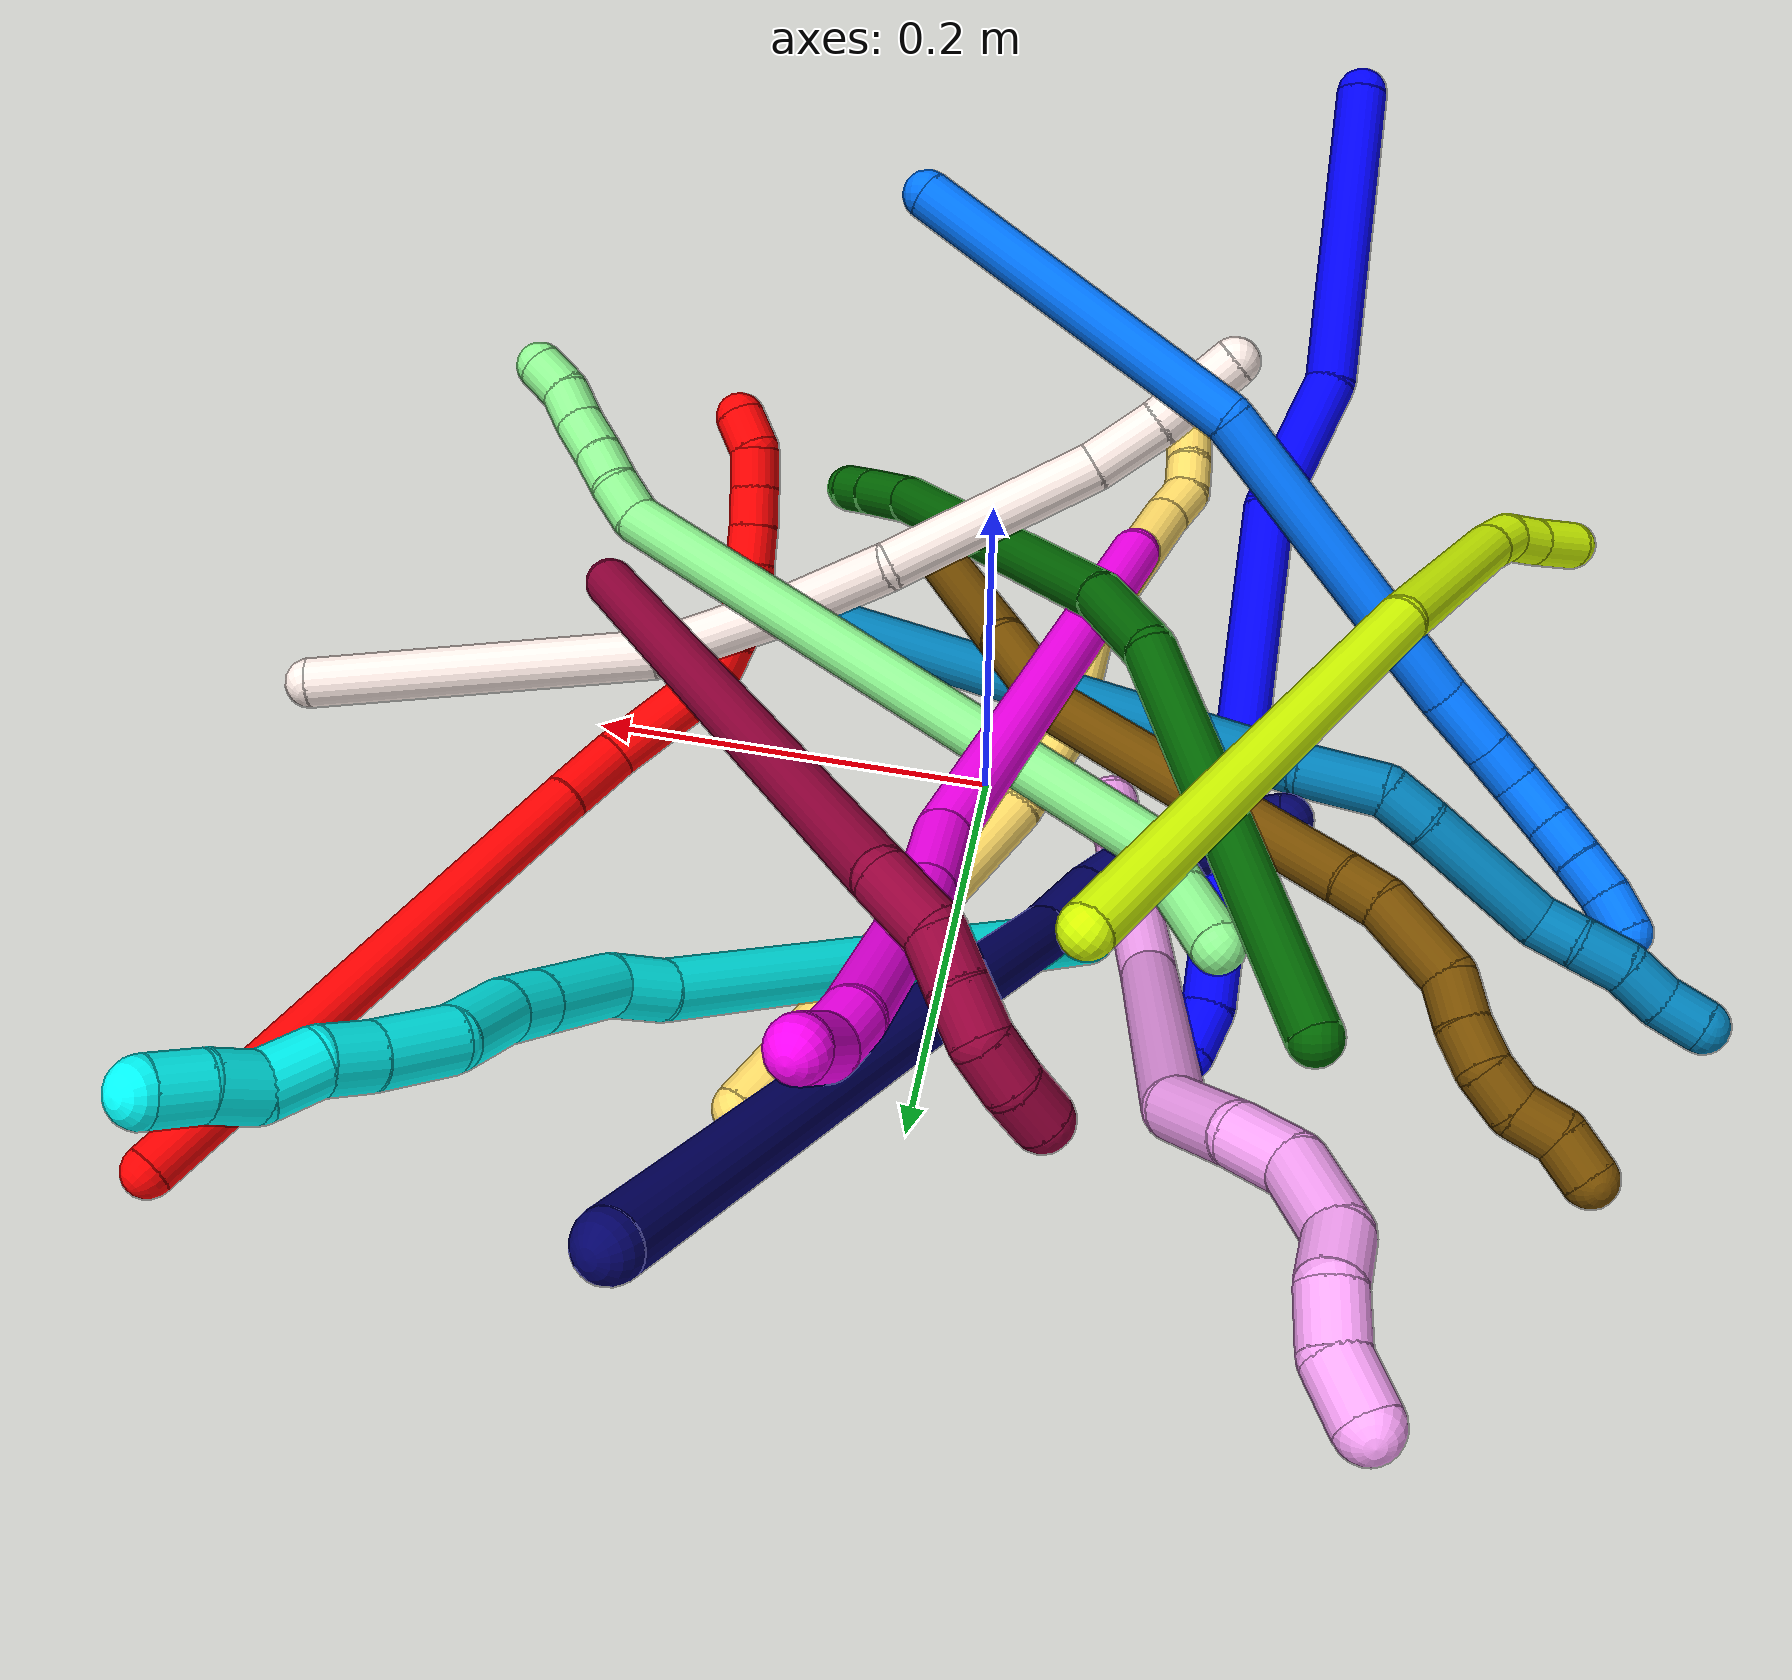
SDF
<sdf version="1.7">
 <world name="default">
  <plugin name="TubeGeneratorPlugin" filename="libtube_generator_plugin.so"/>
  <model name="photoneo_s_sensor">
   <static>1</static>
   <pose>0 0 2 1.57079 1.57079 3.14159</pose>
   <link name="link">
    <inertial><mass>0.1</mass></inertial>
    <sensor name="sensor" type="depth">
     <update_rate>30</update_rate>
     <camera>
      <horizontal_fov>1.22</horizontal_fov>
      <image><width>1920</width><height>1200</height><format>B8G8R8</format></image>
      <clip><near>0.1</near><far>4</far></clip>
      <depth_camera><output>points</output></depth_camera>
     </camera>
     <plugin name="camera_plugin" filename="libgazebo_ros_depth_camera.so">
      <baseline>0.2</baseline>
      <alwaysOn>1</alwaysOn>
      <updateRate>0.0</updateRate>
      <cameraName>camera_ir</cameraName>
      <imageTopicName>/camera/color/image_raw</imageTopicName>
      <cameraInfoTopicName>/camera/color/camera_info</cameraInfoTopicName>
      <depthImageTopicName>/camera/depth/image_raw</depthImageTopicName>
      <depthImageCameraInfoTopicName>/camera/depth/camera_info</depthImageCameraInfoTopicName>
      <pointCloudTopicName>/camera/depth/points</pointCloudTopicName>
      <frameName>fr_optical</frameName>
      <pointCloudCutoff>0.1</pointCloudCutoff>
      <pointCloudCutoffMax>2.0</pointCloudCutoffMax>
      <distortionK1>0</distortionK1>
      <distortionK2>0</distortionK2>
      <distortionK3>0</distortionK3>
      <distortionT1>0</distortionT1>
      <distortionT2>0</distortionT2>
      <CxPrime>0</CxPrime>
      <Cx>0</Cx>
      <Cy>0</Cy>
      <focalLength>0</focalLength>
      <hackBaseline>0</hackBaseline>
     </plugin>
    </sensor>
   </link>
  </model>
  <gravity>0 0 -9.8</gravity>
  <magnetic_field>6e-06 2.3e-05 -4.2e-05</magnetic_field>
  <atmosphere type="adiabatic"/>
  <physics name="default_physics" default="0" type="ode">
   <max_step_size>0.003</max_step_size>
   <real_time_factor>1</real_time_factor>
   <real_time_update_rate>1000</real_time_update_rate>
   <max_contacts>10000</max_contacts>
   <ode>
    <solver>
     <type>quick</type>
     <iters>100</iters>
     <sor>1.3</sor>
     <use_dynamic_moi_rescaling>0</use_dynamic_moi_rescaling>
    </solver>
    <constraints>
     <contact_max_correcting_vel>0</contact_max_correcting_vel>
     <contact_surface_layer>0.001</contact_surface_layer>
     <cfm>0</cfm>
     <erp>0.2</erp>
    </constraints>
   </ode>
  </physics>
  <scene><ambient>0.4 0.4 0.4 1</ambient><background>0.7 0.7 0.7 1</background><shadows>0</shadows></scene>
  <audio><device>default</device></audio>
  <spherical_coordinates>
   <surface_model>EARTH_WGS84</surface_model>
   <latitude_deg>0</latitude_deg>
   <longitude_deg>0</longitude_deg>
   <elevation>0</elevation>
   <heading_deg>0</heading_deg>
  </spherical_coordinates>
  <model name="bin">
   <static>1</static>
   <link name="bottom">
    <collision name="collision-bottom">
     <pose>0 0 -0.01 0 -0 0</pose>
     <geometry><box><size>0.8 0.6 0.02</size></box></geometry>
     <surface>
      <friction><ode><mu>100</mu><mu2>100</mu2></ode></friction>
      <contact><collide_bitmask>65535</collide_bitmask></contact>
     </surface>
    </collision>
   </link>
   <link name="west_wall">
    <collision name="collision-west_wall">
     <pose>-0.41 0 0.1 0 -0 0</pose>
     <geometry><box><size>0.02 0.6 0.2</size></box></geometry>
     <surface>
      <friction><ode><mu>100</mu><mu2>100</mu2></ode></friction>
      <contact><collide_bitmask>65535</collide_bitmask></contact>
     </surface>
    </collision>
   </link>
   <link name="east_wall">
    <collision name="collision-east_wall">
     <pose>0.41 0 0.1 0 -0 0</pose>
     <geometry><box><size>0.02 0.6 0.2</size></box></geometry>
     <surface>
      <friction><ode><mu>100</mu><mu2>100</mu2></ode></friction>
      <contact><collide_bitmask>65535</collide_bitmask></contact>
     </surface>
    </collision>
   </link>
   <link name="south_wall">
    <collision name="collision-south_wall">
     <pose>0 -0.31 0.1 0 -0 0</pose>
     <geometry><box><size>0.8 0.02 0.2</size></box></geometry>
     <surface>
      <friction><ode><mu>100</mu><mu2>100</mu2></ode></friction>
      <contact><collide_bitmask>65535</collide_bitmask></contact>
     </surface>
    </collision>
   </link>
   <link name="north_wall">
    <collision name="collision-north_wall">
     <pose>0 0.31 0.1 0 -0 0</pose>
     <geometry><box><size>0.8 0.02 0.2</size></box></geometry>
     <surface>
      <friction><ode><mu>100</mu><mu2>100</mu2></ode></friction>
      <contact><collide_bitmask>65535</collide_bitmask></contact>
     </surface>
    </collision>
   </link>
  </model>
  <model name="1">
   <static>0</static>
   <link name="1">
    <collision name="collision-cylinder-e_1_1_4">
     <pose>-0.000336 0.070709 -0.029975 -1.97175 -0.004379 0.006613</pose>
     <geometry><cylinder><radius>0.0125</radius><length>0.153601</length></cylinder></geometry>
     <surface>
      <friction><ode><mu>1.16</mu><mu2>1.16</mu2><slip1>0</slip1><slip2>0</slip2></ode></friction>
      <contact><ode><kp>1e+06</kp><kd>1</kd><max_vel>0</max_vel><min_depth>0.001</min_depth></ode></contact>
     </surface>
    </collision>
    <visual name="visual-cylinder-e_1_1_4">
     <pose>-0.000336 0.070709 -0.029975 -1.97175 -0.004379 0.006613</pose>
     <geometry><cylinder><radius>0.0125</radius><length>0.153601</length></cylinder></geometry>
     <material><ambient>0 0 1 1</ambient></material>
    </visual>
    <collision name="collision-cylinder-e_2_4_5">
     <pose>0.010596 0.174072 -0.070614 -1.88647 0.316987 -0.433754</pose>
     <geometry><cylinder><radius>0.0125</radius><length>0.072305</length></cylinder></geometry>
     <surface>
      <friction><ode><mu>1.16</mu><mu2>1.16</mu2><slip1>0</slip1><slip2>0</slip2></ode></friction>
      <contact><ode><kp>1e+06</kp><kd>1</kd><max_vel>0</max_vel><min_depth>0.001</min_depth></ode></contact>
     </surface>
    </collision>
    <visual name="visual-cylinder-e_2_4_5">
     <pose>0.010596 0.174072 -0.070614 -1.88647 0.316987 -0.433754</pose>
     <geometry><cylinder><radius>0.0125</radius><length>0.072305</length></cylinder></geometry>
     <material><ambient>0 0 1 1</ambient></material>
    </visual>
    <collision name="collision-cylinder-e_3_5_6">
     <pose>0.021424 0.310558 -0.108025 -1.82291 -0.004117 0.005312</pose>
     <geometry><cylinder><radius>0.0125</radius><length>0.214445</length></cylinder></geometry>
     <surface>
      <friction><ode><mu>1.16</mu><mu2>1.16</mu2><slip1>0</slip1><slip2>0</slip2></ode></friction>
      <contact><ode><kp>1e+06</kp><kd>1</kd><max_vel>0</max_vel><min_depth>0.001</min_depth></ode></contact>
     </surface>
    </collision>
    <visual name="visual-cylinder-e_3_5_6">
     <pose>0.021424 0.310558 -0.108025 -1.82291 -0.004117 0.005312</pose>
     <geometry><cylinder><radius>0.0125</radius><length>0.214445</length></cylinder></geometry>
     <material><ambient>0 0 1 1</ambient></material>
    </visual>
    <collision name="collision-cylinder-e_4_6_7">
     <pose>0.02102 0.431373 -0.139416 -1.83775 0.002114 -0.002769</pose>
     <geometry><cylinder><radius>0.0125</radius><length>0.035213</length></cylinder></geometry>
     <surface>
      <friction><ode><mu>1.16</mu><mu2>1.16</mu2><slip1>0</slip1><slip2>0</slip2></ode></friction>
      <contact><ode><kp>1e+06</kp><kd>1</kd><max_vel>0</max_vel><min_depth>0.001</min_depth></ode></contact>
     </surface>
    </collision>
    <visual name="visual-cylinder-e_4_6_7">
     <pose>0.02102 0.431373 -0.139416 -1.83775 0.002114 -0.002769</pose>
     <geometry><cylinder><radius>0.0125</radius><length>0.035213</length></cylinder></geometry>
     <material><ambient>0 0 1 1</ambient></material>
    </visual>
    <collision name="collision-cylinder-e_5_7_2">
     <pose>0.024497 0.460073 -0.144452 -1.6042 0.285411 -0.294971</pose>
     <geometry><cylinder><radius>0.0125</radius><length>0.024435</length></cylinder></geometry>
     <surface>
      <friction><ode><mu>1.16</mu><mu2>1.16</mu2><slip1>0</slip1><slip2>0</slip2></ode></friction>
      <contact><ode><kp>1e+06</kp><kd>1</kd><max_vel>0</max_vel><min_depth>0.001</min_depth></ode></contact>
     </surface>
    </collision>
    <visual name="visual-cylinder-e_5_7_2">
     <pose>0.024497 0.460073 -0.144452 -1.6042 0.285411 -0.294971</pose>
     <geometry><cylinder><radius>0.0125</radius><length>0.024435</length></cylinder></geometry>
     <material><ambient>0 0 1 1</ambient></material>
    </visual>
    <collision name="collision-sphere-2">
     <pose>0.027937 0.47179 -0.144843 0 -0 0</pose>
     <geometry><sphere><radius>0.0125</radius></sphere></geometry>
     <surface>
      <friction><ode><mu>1.16</mu><mu2>1.16</mu2><slip1>0</slip1><slip2>0</slip2></ode></friction>
      <contact><ode><kp>1e+06</kp><kd>1</kd><max_vel>0</max_vel><min_depth>0.001</min_depth></ode></contact>
     </surface>
    </collision>
    <visual name="visual-sphere-2">
     <pose>0.027937 0.47179 -0.144843 0 -0 0</pose>
     <geometry><sphere><radius>0.0125</radius></sphere></geometry>
     <material><ambient>0 0 1 1</ambient></material>
    </visual>
    <collision name="collision-sphere-7">
     <pose>0.021057 0.448356 -0.14406 0 -0 0</pose>
     <geometry><sphere><radius>0.0125</radius></sphere></geometry>
     <surface>
      <friction><ode><mu>1.16</mu><mu2>1.16</mu2><slip1>0</slip1><slip2>0</slip2></ode></friction>
      <contact><ode><kp>1e+06</kp><kd>1</kd><max_vel>0</max_vel><min_depth>0.001</min_depth></ode></contact>
     </surface>
    </collision>
    <visual name="visual-sphere-7">
     <pose>0.021057 0.448356 -0.14406 0 -0 0</pose>
     <geometry><sphere><radius>0.0125</radius></sphere></geometry>
     <material><ambient>0 0 1 1</ambient></material>
    </visual>
    <collision name="collision-sphere-6">
     <pose>0.020982 0.41439 -0.134771 0 -0 0</pose>
     <geometry><sphere><radius>0.0125</radius></sphere></geometry>
     <surface>
      <friction><ode><mu>1.16</mu><mu2>1.16</mu2><slip1>0</slip1><slip2>0</slip2></ode></friction>
      <contact><ode><kp>1e+06</kp><kd>1</kd><max_vel>0</max_vel><min_depth>0.001</min_depth></ode></contact>
     </surface>
    </collision>
    <visual name="visual-sphere-6">
     <pose>0.020982 0.41439 -0.134771 0 -0 0</pose>
     <geometry><sphere><radius>0.0125</radius></sphere></geometry>
     <material><ambient>0 0 1 1</ambient></material>
    </visual>
    <collision name="collision-sphere-5">
     <pose>0.021865 0.206726 -0.081279 0 -0 0</pose>
     <geometry><sphere><radius>0.0125</radius></sphere></geometry>
     <surface>
      <friction><ode><mu>1.16</mu><mu2>1.16</mu2><slip1>0</slip1><slip2>0</slip2></ode></friction>
      <contact><ode><kp>1e+06</kp><kd>1</kd><max_vel>0</max_vel><min_depth>0.001</min_depth></ode></contact>
     </surface>
    </collision>
    <visual name="visual-sphere-5">
     <pose>0.021865 0.206726 -0.081279 0 -0 0</pose>
     <geometry><sphere><radius>0.0125</radius></sphere></geometry>
     <material><ambient>0 0 1 1</ambient></material>
    </visual>
    <collision name="collision-sphere-1">
     <geometry><sphere><radius>0.0125</radius></sphere></geometry>
     <surface>
      <friction><ode><mu>1.16</mu><mu2>1.16</mu2><slip1>0</slip1><slip2>0</slip2></ode></friction>
      <contact><ode><kp>1e+06</kp><kd>1</kd><max_vel>0</max_vel><min_depth>0.001</min_depth></ode></contact>
     </surface>
    </collision>
    <visual name="visual-sphere-1">
     <geometry><sphere><radius>0.0125</radius></sphere></geometry>
     <material><ambient>0 0 1 1</ambient></material>
    </visual>
    <collision name="collision-sphere-4">
     <pose>-0.000673 0.141418 -0.05995 0 -0 0</pose>
     <geometry><sphere><radius>0.0125</radius></sphere></geometry>
     <surface>
      <friction><ode><mu>1.16</mu><mu2>1.16</mu2><slip1>0</slip1><slip2>0</slip2></ode></friction>
      <contact><ode><kp>1e+06</kp><kd>1</kd><max_vel>0</max_vel><min_depth>0.001</min_depth></ode></contact>
     </surface>
    </collision>
    <visual name="visual-sphere-4">
     <pose>-0.000673 0.141418 -0.05995 0 -0 0</pose>
     <geometry><sphere><radius>0.0125</radius></sphere></geometry>
     <material><ambient>0 0 1 1</ambient></material>
    </visual>
    <inertial>
     <pose>0.013295 0.232954 -0.082629 0 -0 0</pose>
     <mass>0.5</mass>
     <inertia>
      <ixx>0.001169</ixx>
      <ixy>0</ixy>
      <ixz>0</ixz>
      <iyy>-0.000305</iyy>
      <iyz>0</iyz>
      <izz>-0.001143</izz>
     </inertia>
    </inertial>
   </link>
   <pose>-0.134274 -0.307726 0.217851 -0.130316 0.068608 -0.005236</pose>
  </model>
  <model name="2">
   <static>0</static>
   <link name="2">
    <collision name="collision-cylinder-e_1_1_4">
     <pose>0.002531 0.002678 -0.130263 -3.12104 0.019425 -1.51424</pose>
     <geometry><cylinder><radius>0.0125</radius><length>0.260631</length></cylinder></geometry>
     <surface>
      <friction><ode><mu>1.16</mu><mu2>1.16</mu2><slip1>0</slip1><slip2>0</slip2></ode></friction>
      <contact><ode><kp>1e+06</kp><kd>1</kd><max_vel>0</max_vel><min_depth>0.001</min_depth></ode></contact>
     </surface>
    </collision>
    <visual name="visual-cylinder-e_1_1_4">
     <pose>0.002531 0.002678 -0.130263 -3.12104 0.019425 -1.51424</pose>
     <geometry><cylinder><radius>0.0125</radius><length>0.260631</length></cylinder></geometry>
     <material><ambient>1 0 0 1</ambient></material>
    </visual>
    <collision name="collision-cylinder-e_2_4_5">
     <pose>0.006159 0.005973 -0.278099 -3.10647 0.062278 -2.11487</pose>
     <geometry><cylinder><radius>0.0125</radius><length>0.035234</length></cylinder></geometry>
     <surface>
      <friction><ode><mu>1.16</mu><mu2>1.16</mu2><slip1>0</slip1><slip2>0</slip2></ode></friction>
      <contact><ode><kp>1e+06</kp><kd>1</kd><max_vel>0</max_vel><min_depth>0.001</min_depth></ode></contact>
     </surface>
    </collision>
    <visual name="visual-cylinder-e_2_4_5">
     <pose>0.006159 0.005973 -0.278099 -3.10647 0.062278 -2.11487</pose>
     <geometry><cylinder><radius>0.0125</radius><length>0.035234</length></cylinder></geometry>
     <material><ambient>1 0 0 1</ambient></material>
    </visual>
    <collision name="collision-cylinder-e_3_5_6">
     <pose>-0.001226 0.010085 -0.324978 -3.02292 -0.279804 2.34318</pose>
     <geometry><cylinder><radius>0.0125</radius><length>0.061418</length></cylinder></geometry>
     <surface>
      <friction><ode><mu>1.16</mu><mu2>1.16</mu2><slip1>0</slip1><slip2>0</slip2></ode></friction>
      <contact><ode><kp>1e+06</kp><kd>1</kd><max_vel>0</max_vel><min_depth>0.001</min_depth></ode></contact>
     </surface>
    </collision>
    <visual name="visual-cylinder-e_3_5_6">
     <pose>-0.001226 0.010085 -0.324978 -3.02292 -0.279804 2.34318</pose>
     <geometry><cylinder><radius>0.0125</radius><length>0.061418</length></cylinder></geometry>
     <material><ambient>1 0 0 1</ambient></material>
    </visual>
    <collision name="collision-cylinder-e_4_6_7">
     <pose>-0.014864 0.009798 -0.363417 2.74897 -0.480982 -1.77883</pose>
     <geometry><cylinder><radius>0.0125</radius><length>0.022296</length></cylinder></geometry>
     <surface>
      <friction><ode><mu>1.16</mu><mu2>1.16</mu2><slip1>0</slip1><slip2>0</slip2></ode></friction>
      <contact><ode><kp>1e+06</kp><kd>1</kd><max_vel>0</max_vel><min_depth>0.001</min_depth></ode></contact>
     </surface>
    </collision>
    <visual name="visual-cylinder-e_4_6_7">
     <pose>-0.014864 0.009798 -0.363417 2.74897 -0.480982 -1.77883</pose>
     <geometry><cylinder><radius>0.0125</radius><length>0.022296</length></cylinder></geometry>
     <material><ambient>1 0 0 1</ambient></material>
    </visual>
    <collision name="collision-cylinder-e_5_7_8">
     <pose>-0.025382 0.002486 -0.380393 2.71874 -0.557222 -1.85417</pose>
     <geometry><cylinder><radius>0.0125</radius><length>0.020273</length></cylinder></geometry>
     <surface>
      <friction><ode><mu>1.16</mu><mu2>1.16</mu2><slip1>0</slip1><slip2>0</slip2></ode></friction>
      <contact><ode><kp>1e+06</kp><kd>1</kd><max_vel>0</max_vel><min_depth>0.001</min_depth></ode></contact>
     </surface>
    </collision>
    <visual name="visual-cylinder-e_5_7_8">
     <pose>-0.025382 0.002486 -0.380393 2.71874 -0.557222 -1.85417</pose>
     <geometry><cylinder><radius>0.0125</radius><length>0.020273</length></cylinder></geometry>
     <material><ambient>1 0 0 1</ambient></material>
    </visual>
    <collision name="collision-cylinder-e_6_8_9">
     <pose>-0.033017 -0.00798 -0.395104 2.35109 -0.22893 -0.537782</pose>
     <geometry><cylinder><radius>0.0125</radius><length>0.020042</length></cylinder></geometry>
     <surface>
      <friction><ode><mu>1.16</mu><mu2>1.16</mu2><slip1>0</slip1><slip2>0</slip2></ode></friction>
      <contact><ode><kp>1e+06</kp><kd>1</kd><max_vel>0</max_vel><min_depth>0.001</min_depth></ode></contact>
     </surface>
    </collision>
    <visual name="visual-cylinder-e_6_8_9">
     <pose>-0.033017 -0.00798 -0.395104 2.35109 -0.22893 -0.537782</pose>
     <geometry><cylinder><radius>0.0125</radius><length>0.020042</length></cylinder></geometry>
     <material><ambient>1 0 0 1</ambient></material>
    </visual>
    <collision name="collision-cylinder-e_7_9_10">
     <pose>-0.037722 -0.021402 -0.409239 2.41315 -0.2446 -0.62378</pose>
     <geometry><cylinder><radius>0.0125</radius><length>0.020082</length></cylinder></geometry>
     <surface>
      <friction><ode><mu>1.16</mu><mu2>1.16</mu2><slip1>0</slip1><slip2>0</slip2></ode></friction>
      <contact><ode><kp>1e+06</kp><kd>1</kd><max_vel>0</max_vel><min_depth>0.001</min_depth></ode></contact>
     </surface>
    </collision>
    <visual name="visual-cylinder-e_7_9_10">
     <pose>-0.037722 -0.021402 -0.409239 2.41315 -0.2446 -0.62378</pose>
     <geometry><cylinder><radius>0.0125</radius><length>0.020082</length></cylinder></geometry>
     <material><ambient>1 0 0 1</ambient></material>
    </visual>
    <collision name="collision-cylinder-e_8_10_11">
     <pose>-0.042613 -0.034855 -0.423259 2.34034 -0.248255 -0.572974</pose>
     <geometry><cylinder><radius>0.0125</radius><length>0.020016</length></cylinder></geometry>
     <surface>
      <friction><ode><mu>1.16</mu><mu2>1.16</mu2><slip1>0</slip1><slip2>0</slip2></ode></friction>
      <contact><ode><kp>1e+06</kp><kd>1</kd><max_vel>0</max_vel><min_depth>0.001</min_depth></ode></contact>
     </surface>
    </collision>
    <visual name="visual-cylinder-e_8_10_11">
     <pose>-0.042613 -0.034855 -0.423259 2.34034 -0.248255 -0.572974</pose>
     <geometry><cylinder><radius>0.0125</radius><length>0.020016</length></cylinder></geometry>
     <material><ambient>1 0 0 1</ambient></material>
    </visual>
    <collision name="collision-cylinder-e_9_11_12">
     <pose>-0.047954 -0.049031 -0.436318 2.28971 -0.292216 -0.627262</pose>
     <geometry><cylinder><radius>0.0125</radius><length>0.020008</length></cylinder></geometry>
     <surface>
      <friction><ode><mu>1.16</mu><mu2>1.16</mu2><slip1>0</slip1><slip2>0</slip2></ode></friction>
      <contact><ode><kp>1e+06</kp><kd>1</kd><max_vel>0</max_vel><min_depth>0.001</min_depth></ode></contact>
     </surface>
    </collision>
    <visual name="visual-cylinder-e_9_11_12">
     <pose>-0.047954 -0.049031 -0.436318 2.28971 -0.292216 -0.627262</pose>
     <geometry><cylinder><radius>0.0125</radius><length>0.020008</length></cylinder></geometry>
     <material><ambient>1 0 0 1</ambient></material>
    </visual>
    <collision name="collision-cylinder-e_10_12_2">
     <pose>-0.049459 -0.065067 -0.447121 2.04166 0.138149 0.224753</pose>
     <geometry><cylinder><radius>0.0125</radius><length>0.02</length></cylinder></geometry>
     <surface>
      <friction><ode><mu>1.16</mu><mu2>1.16</mu2><slip1>0</slip1><slip2>0</slip2></ode></friction>
      <contact><ode><kp>1e+06</kp><kd>1</kd><max_vel>0</max_vel><min_depth>0.001</min_depth></ode></contact>
     </surface>
    </collision>
    <visual name="visual-cylinder-e_10_12_2">
     <pose>-0.049459 -0.065067 -0.447121 2.04166 0.138149 0.224753</pose>
     <geometry><cylinder><radius>0.0125</radius><length>0.02</length></cylinder></geometry>
     <material><ambient>1 0 0 1</ambient></material>
    </visual>
    <collision name="collision-sphere-2">
     <pose>-0.048082 -0.073894 -0.451614 0 -0 0</pose>
     <geometry><sphere><radius>0.0125</radius></sphere></geometry>
     <surface>
      <friction><ode><mu>1.16</mu><mu2>1.16</mu2><slip1>0</slip1><slip2>0</slip2></ode></friction>
      <contact><ode><kp>1e+06</kp><kd>1</kd><max_vel>0</max_vel><min_depth>0.001</min_depth></ode></contact>
     </surface>
    </collision>
    <visual name="visual-sphere-2">
     <pose>-0.048082 -0.073894 -0.451614 0 -0 0</pose>
     <geometry><sphere><radius>0.0125</radius></sphere></geometry>
     <material><ambient>1 0 0 1</ambient></material>
    </visual>
    <collision name="collision-sphere-12">
     <pose>-0.050836 -0.05624 -0.442627 0 -0 0</pose>
     <geometry><sphere><radius>0.0125</radius></sphere></geometry>
     <surface>
      <friction><ode><mu>1.16</mu><mu2>1.16</mu2><slip1>0</slip1><slip2>0</slip2></ode></friction>
      <contact><ode><kp>1e+06</kp><kd>1</kd><max_vel>0</max_vel><min_depth>0.001</min_depth></ode></contact>
     </surface>
    </collision>
    <visual name="visual-sphere-12">
     <pose>-0.050836 -0.05624 -0.442627 0 -0 0</pose>
     <geometry><sphere><radius>0.0125</radius></sphere></geometry>
     <material><ambient>1 0 0 1</ambient></material>
    </visual>
    <collision name="collision-sphere-11">
     <pose>-0.045072 -0.041822 -0.430009 0 -0 0</pose>
     <geometry><sphere><radius>0.0125</radius></sphere></geometry>
     <surface>
      <friction><ode><mu>1.16</mu><mu2>1.16</mu2><slip1>0</slip1><slip2>0</slip2></ode></friction>
      <contact><ode><kp>1e+06</kp><kd>1</kd><max_vel>0</max_vel><min_depth>0.001</min_depth></ode></contact>
     </surface>
    </collision>
    <visual name="visual-sphere-11">
     <pose>-0.045072 -0.041822 -0.430009 0 -0 0</pose>
     <geometry><sphere><radius>0.0125</radius></sphere></geometry>
     <material><ambient>1 0 0 1</ambient></material>
    </visual>
    <collision name="collision-sphere-10">
     <pose>-0.040154 -0.027887 -0.416509 0 -0 0</pose>
     <geometry><sphere><radius>0.0125</radius></sphere></geometry>
     <surface>
      <friction><ode><mu>1.16</mu><mu2>1.16</mu2><slip1>0</slip1><slip2>0</slip2></ode></friction>
      <contact><ode><kp>1e+06</kp><kd>1</kd><max_vel>0</max_vel><min_depth>0.001</min_depth></ode></contact>
     </surface>
    </collision>
    <visual name="visual-sphere-10">
     <pose>-0.040154 -0.027887 -0.416509 0 -0 0</pose>
     <geometry><sphere><radius>0.0125</radius></sphere></geometry>
     <material><ambient>1 0 0 1</ambient></material>
    </visual>
    <collision name="collision-sphere-9">
     <pose>-0.035291 -0.014916 -0.40197 0 -0 0</pose>
     <geometry><sphere><radius>0.0125</radius></sphere></geometry>
     <surface>
      <friction><ode><mu>1.16</mu><mu2>1.16</mu2><slip1>0</slip1><slip2>0</slip2></ode></friction>
      <contact><ode><kp>1e+06</kp><kd>1</kd><max_vel>0</max_vel><min_depth>0.001</min_depth></ode></contact>
     </surface>
    </collision>
    <visual name="visual-sphere-9">
     <pose>-0.035291 -0.014916 -0.40197 0 -0 0</pose>
     <geometry><sphere><radius>0.0125</radius></sphere></geometry>
     <material><ambient>1 0 0 1</ambient></material>
    </visual>
    <collision name="collision-sphere-4">
     <pose>0.005062 0.005356 -0.260527 0 -0 0</pose>
     <geometry><sphere><radius>0.0125</radius></sphere></geometry>
     <surface>
      <friction><ode><mu>1.16</mu><mu2>1.16</mu2><slip1>0</slip1><slip2>0</slip2></ode></friction>
      <contact><ode><kp>1e+06</kp><kd>1</kd><max_vel>0</max_vel><min_depth>0.001</min_depth></ode></contact>
     </surface>
    </collision>
    <visual name="visual-sphere-4">
     <pose>0.005062 0.005356 -0.260527 0 -0 0</pose>
     <geometry><sphere><radius>0.0125</radius></sphere></geometry>
     <material><ambient>1 0 0 1</ambient></material>
    </visual>
    <collision name="collision-sphere-1">
     <geometry><sphere><radius>0.0125</radius></sphere></geometry>
     <surface>
      <friction><ode><mu>1.16</mu><mu2>1.16</mu2><slip1>0</slip1><slip2>0</slip2></ode></friction>
      <contact><ode><kp>1e+06</kp><kd>1</kd><max_vel>0</max_vel><min_depth>0.001</min_depth></ode></contact>
     </surface>
    </collision>
    <visual name="visual-sphere-1">
     <geometry><sphere><radius>0.0125</radius></sphere></geometry>
     <material><ambient>1 0 0 1</ambient></material>
    </visual>
    <collision name="collision-sphere-8">
     <pose>-0.030743 -0.001044 -0.388238 0 -0 0</pose>
     <geometry><sphere><radius>0.0125</radius></sphere></geometry>
     <surface>
      <friction><ode><mu>1.16</mu><mu2>1.16</mu2><slip1>0</slip1><slip2>0</slip2></ode></friction>
      <contact><ode><kp>1e+06</kp><kd>1</kd><max_vel>0</max_vel><min_depth>0.001</min_depth></ode></contact>
     </surface>
    </collision>
    <visual name="visual-sphere-8">
     <pose>-0.030743 -0.001044 -0.388238 0 -0 0</pose>
     <geometry><sphere><radius>0.0125</radius></sphere></geometry>
     <material><ambient>1 0 0 1</ambient></material>
    </visual>
    <collision name="collision-sphere-5">
     <pose>0.007255 0.006591 -0.295671 0 -0 0</pose>
     <geometry><sphere><radius>0.0125</radius></sphere></geometry>
     <surface>
      <friction><ode><mu>1.16</mu><mu2>1.16</mu2><slip1>0</slip1><slip2>0</slip2></ode></friction>
      <contact><ode><kp>1e+06</kp><kd>1</kd><max_vel>0</max_vel><min_depth>0.001</min_depth></ode></contact>
     </surface>
    </collision>
    <visual name="visual-sphere-5">
     <pose>0.007255 0.006591 -0.295671 0 -0 0</pose>
     <geometry><sphere><radius>0.0125</radius></sphere></geometry>
     <material><ambient>1 0 0 1</ambient></material>
    </visual>
    <collision name="collision-sphere-6">
     <pose>-0.009706 0.01358 -0.354285 0 -0 0</pose>
     <geometry><sphere><radius>0.0125</radius></sphere></geometry>
     <surface>
      <friction><ode><mu>1.16</mu><mu2>1.16</mu2><slip1>0</slip1><slip2>0</slip2></ode></friction>
      <contact><ode><kp>1e+06</kp><kd>1</kd><max_vel>0</max_vel><min_depth>0.001</min_depth></ode></contact>
     </surface>
    </collision>
    <visual name="visual-sphere-6">
     <pose>-0.009706 0.01358 -0.354285 0 -0 0</pose>
     <geometry><sphere><radius>0.0125</radius></sphere></geometry>
     <material><ambient>1 0 0 1</ambient></material>
    </visual>
    <collision name="collision-sphere-7">
     <pose>-0.020022 0.006017 -0.372548 0 -0 0</pose>
     <geometry><sphere><radius>0.0125</radius></sphere></geometry>
     <surface>
      <friction><ode><mu>1.16</mu><mu2>1.16</mu2><slip1>0</slip1><slip2>0</slip2></ode></friction>
      <contact><ode><kp>1e+06</kp><kd>1</kd><max_vel>0</max_vel><min_depth>0.001</min_depth></ode></contact>
     </surface>
    </collision>
    <visual name="visual-sphere-7">
     <pose>-0.020022 0.006017 -0.372548 0 -0 0</pose>
     <geometry><sphere><radius>0.0125</radius></sphere></geometry>
     <material><ambient>1 0 0 1</ambient></material>
    </visual>
    <inertial>
     <pose>-0.008531 -0.003546 -0.243609 0 -0 0</pose>
     <mass>0.5</mass>
     <inertia>
      <ixx>-0.001409</ixx>
      <ixy>0</ixy>
      <ixz>0</ixz>
      <iyy>-0.001551</iyy>
      <iyz>0</iyz>
      <izz>-8.2e-05</izz>
     </inertia>
    </inertial>
   </link>
   <pose>0.32009 0.288168 0.012486 -1.62957 1.05534 -0.51936</pose>
  </model>
  <model name="3">
   <static>0</static>
   <link name="3">
    <collision name="collision-cylinder-e_1_1_4">
     <pose>-0.007432 0.0337 0.125093 -0.263151 -0.057304 0.007586</pose>
     <geometry><cylinder><radius>0.0125</radius><length>0.259531</length></cylinder></geometry>
     <surface>
      <friction><ode><mu>1.16</mu><mu2>1.16</mu2><slip1>0</slip1><slip2>0</slip2></ode></friction>
      <contact><ode><kp>1e+06</kp><kd>1</kd><max_vel>0</max_vel><min_depth>0.001</min_depth></ode></contact>
     </surface>
    </collision>
    <visual name="visual-cylinder-e_1_1_4">
     <pose>-0.007432 0.0337 0.125093 -0.263151 -0.057304 0.007586</pose>
     <geometry><cylinder><radius>0.0125</radius><length>0.259531</length></cylinder></geometry>
     <material><ambient>0.003922 1 0.996078 1</ambient></material>
    </visual>
    <collision name="collision-cylinder-e_2_4_5">
     <pose>-0.013616 0.071825 0.262401 -0.347585 0.095783 -0.016828</pose>
     <geometry><cylinder><radius>0.0125</radius><length>0.026105</length></cylinder></geometry>
     <surface>
      <friction><ode><mu>1.16</mu><mu2>1.16</mu2><slip1>0</slip1><slip2>0</slip2></ode></friction>
      <contact><ode><kp>1e+06</kp><kd>1</kd><max_vel>0</max_vel><min_depth>0.001</min_depth></ode></contact>
     </surface>
    </collision>
    <visual name="visual-cylinder-e_2_4_5">
     <pose>-0.013616 0.071825 0.262401 -0.347585 0.095783 -0.016828</pose>
     <geometry><cylinder><radius>0.0125</radius><length>0.026105</length></cylinder></geometry>
     <material><ambient>0.003922 1 0.996078 1</ambient></material>
    </visual>
    <collision name="collision-cylinder-e_3_5_6">
     <pose>-0.013195 0.076774 0.296026 -0.02443 -0.03864 0.000472</pose>
     <geometry><cylinder><radius>0.0125</radius><length>0.042865</length></cylinder></geometry>
     <surface>
      <friction><ode><mu>1.16</mu><mu2>1.16</mu2><slip1>0</slip1><slip2>0</slip2></ode></friction>
      <contact><ode><kp>1e+06</kp><kd>1</kd><max_vel>0</max_vel><min_depth>0.001</min_depth></ode></contact>
     </surface>
    </collision>
    <visual name="visual-cylinder-e_3_5_6">
     <pose>-0.013195 0.076774 0.296026 -0.02443 -0.03864 0.000472</pose>
     <geometry><cylinder><radius>0.0125</radius><length>0.042865</length></cylinder></geometry>
     <material><ambient>0.003922 1 0.996078 1</ambient></material>
    </visual>
    <collision name="collision-cylinder-e_4_6_7">
     <pose>-0.014395 0.077422 0.327651 -0.012217 -0.036416 0.000222</pose>
     <geometry><cylinder><radius>0.0125</radius><length>0.020445</length></cylinder></geometry>
     <surface>
      <friction><ode><mu>1.16</mu><mu2>1.16</mu2><slip1>0</slip1><slip2>0</slip2></ode></friction>
      <contact><ode><kp>1e+06</kp><kd>1</kd><max_vel>0</max_vel><min_depth>0.001</min_depth></ode></contact>
     </surface>
    </collision>
    <visual name="visual-cylinder-e_4_6_7">
     <pose>-0.014395 0.077422 0.327651 -0.012217 -0.036416 0.000222</pose>
     <geometry><cylinder><radius>0.0125</radius><length>0.020445</length></cylinder></geometry>
     <material><ambient>0.003922 1 0.996078 1</ambient></material>
    </visual>
    <collision name="collision-cylinder-e_5_7_8">
     <pose>-0.016578 0.074567 0.354916 0.173028 -0.104216 -0.009047</pose>
     <geometry><cylinder><radius>0.0125</radius><length>0.034804</length></cylinder></geometry>
     <surface>
      <friction><ode><mu>1.16</mu><mu2>1.16</mu2><slip1>0</slip1><slip2>0</slip2></ode></friction>
      <contact><ode><kp>1e+06</kp><kd>1</kd><max_vel>0</max_vel><min_depth>0.001</min_depth></ode></contact>
     </surface>
    </collision>
    <visual name="visual-cylinder-e_5_7_8">
     <pose>-0.016578 0.074567 0.354916 0.173028 -0.104216 -0.009047</pose>
     <geometry><cylinder><radius>0.0125</radius><length>0.034804</length></cylinder></geometry>
     <material><ambient>0.003922 1 0.996078 1</ambient></material>
    </visual>
    <collision name="collision-cylinder-e_6_8_9">
     <pose>-0.020174 0.075298 0.388132 -0.225628 -0.10724 0.012161</pose>
     <geometry><cylinder><radius>0.0125</radius><length>0.033366</length></cylinder></geometry>
     <surface>
      <friction><ode><mu>1.16</mu><mu2>1.16</mu2><slip1>0</slip1><slip2>0</slip2></ode></friction>
      <contact><ode><kp>1e+06</kp><kd>1</kd><max_vel>0</max_vel><min_depth>0.001</min_depth></ode></contact>
     </surface>
    </collision>
    <visual name="visual-cylinder-e_6_8_9">
     <pose>-0.020174 0.075298 0.388132 -0.225628 -0.10724 0.012161</pose>
     <geometry><cylinder><radius>0.0125</radius><length>0.033366</length></cylinder></geometry>
     <material><ambient>0.003922 1 0.996078 1</ambient></material>
    </visual>
    <collision name="collision-cylinder-e_7_9_10">
     <pose>-0.02223 0.081791 0.414311 -0.271005 -0.025998 0.003545</pose>
     <geometry><cylinder><radius>0.0125</radius><length>0.020792</length></cylinder></geometry>
     <surface>
      <friction><ode><mu>1.16</mu><mu2>1.16</mu2><slip1>0</slip1><slip2>0</slip2></ode></friction>
      <contact><ode><kp>1e+06</kp><kd>1</kd><max_vel>0</max_vel><min_depth>0.001</min_depth></ode></contact>
     </surface>
    </collision>
    <visual name="visual-cylinder-e_7_9_10">
     <pose>-0.02223 0.081791 0.414311 -0.271005 -0.025998 0.003545</pose>
     <geometry><cylinder><radius>0.0125</radius><length>0.020792</length></cylinder></geometry>
     <material><ambient>0.003922 1 0.996078 1</ambient></material>
    </visual>
    <collision name="collision-cylinder-e_8_10_11">
     <pose>-0.026505 0.087522 0.433984 -0.296323 -0.377509 0.057009</pose>
     <geometry><cylinder><radius>0.0125</radius><length>0.021729</length></cylinder></geometry>
     <surface>
      <friction><ode><mu>1.16</mu><mu2>1.16</mu2><slip1>0</slip1><slip2>0</slip2></ode></friction>
      <contact><ode><kp>1e+06</kp><kd>1</kd><max_vel>0</max_vel><min_depth>0.001</min_depth></ode></contact>
     </surface>
    </collision>
    <visual name="visual-cylinder-e_8_10_11">
     <pose>-0.026505 0.087522 0.433984 -0.296323 -0.377509 0.057009</pose>
     <geometry><cylinder><radius>0.0125</radius><length>0.021729</length></cylinder></geometry>
     <material><ambient>0.003922 1 0.996078 1</ambient></material>
    </visual>
    <collision name="collision-cylinder-e_9_11_12">
     <pose>-0.029569 0.093422 0.453235 -0.298504 0.093449 -0.014062</pose>
     <geometry><cylinder><radius>0.0125</radius><length>0.020158</length></cylinder></geometry>
     <surface>
      <friction><ode><mu>1.16</mu><mu2>1.16</mu2><slip1>0</slip1><slip2>0</slip2></ode></friction>
      <contact><ode><kp>1e+06</kp><kd>1</kd><max_vel>0</max_vel><min_depth>0.001</min_depth></ode></contact>
     </surface>
    </collision>
    <visual name="visual-cylinder-e_9_11_12">
     <pose>-0.029569 0.093422 0.453235 -0.298504 0.093449 -0.014062</pose>
     <geometry><cylinder><radius>0.0125</radius><length>0.020158</length></cylinder></geometry>
     <material><ambient>0.003922 1 0.996078 1</ambient></material>
    </visual>
    <collision name="collision-cylinder-e_10_12_2">
     <pose>-0.029263 0.099896 0.472273 -0.356932 -0.062827 0.011337</pose>
     <geometry><cylinder><radius>0.0125</radius><length>0.020205</length></cylinder></geometry>
     <surface>
      <friction><ode><mu>1.16</mu><mu2>1.16</mu2><slip1>0</slip1><slip2>0</slip2></ode></friction>
      <contact><ode><kp>1e+06</kp><kd>1</kd><max_vel>0</max_vel><min_depth>0.001</min_depth></ode></contact>
     </surface>
    </collision>
    <visual name="visual-cylinder-e_10_12_2">
     <pose>-0.029263 0.099896 0.472273 -0.356932 -0.062827 0.011337</pose>
     <geometry><cylinder><radius>0.0125</radius><length>0.020205</length></cylinder></geometry>
     <material><ambient>0.003922 1 0.996078 1</ambient></material>
    </visual>
    <collision name="collision-sphere-2">
     <pose>-0.029897 0.103419 0.48172 0 -0 0</pose>
     <geometry><sphere><radius>0.0125</radius></sphere></geometry>
     <surface>
      <friction><ode><mu>1.16</mu><mu2>1.16</mu2><slip1>0</slip1><slip2>0</slip2></ode></friction>
      <contact><ode><kp>1e+06</kp><kd>1</kd><max_vel>0</max_vel><min_depth>0.001</min_depth></ode></contact>
     </surface>
    </collision>
    <visual name="visual-sphere-2">
     <pose>-0.029897 0.103419 0.48172 0 -0 0</pose>
     <geometry><sphere><radius>0.0125</radius></sphere></geometry>
     <material><ambient>0.003922 1 0.996078 1</ambient></material>
    </visual>
    <collision name="collision-sphere-12">
     <pose>-0.028628 0.096374 0.462826 0 -0 0</pose>
     <geometry><sphere><radius>0.0125</radius></sphere></geometry>
     <surface>
      <friction><ode><mu>1.16</mu><mu2>1.16</mu2><slip1>0</slip1><slip2>0</slip2></ode></friction>
      <contact><ode><kp>1e+06</kp><kd>1</kd><max_vel>0</max_vel><min_depth>0.001</min_depth></ode></contact>
     </surface>
    </collision>
    <visual name="visual-sphere-12">
     <pose>-0.028628 0.096374 0.462826 0 -0 0</pose>
     <geometry><sphere><radius>0.0125</radius></sphere></geometry>
     <material><ambient>0.003922 1 0.996078 1</ambient></material>
    </visual>
    <collision name="collision-sphere-11">
     <pose>-0.030509 0.090471 0.443643 0 -0 0</pose>
     <geometry><sphere><radius>0.0125</radius></sphere></geometry>
     <surface>
      <friction><ode><mu>1.16</mu><mu2>1.16</mu2><slip1>0</slip1><slip2>0</slip2></ode></friction>
      <contact><ode><kp>1e+06</kp><kd>1</kd><max_vel>0</max_vel><min_depth>0.001</min_depth></ode></contact>
     </surface>
    </collision>
    <visual name="visual-sphere-11">
     <pose>-0.030509 0.090471 0.443643 0 -0 0</pose>
     <geometry><sphere><radius>0.0125</radius></sphere></geometry>
     <material><ambient>0.003922 1 0.996078 1</ambient></material>
    </visual>
    <collision name="collision-sphere-10">
     <pose>-0.0225 0.084573 0.424325 0 -0 0</pose>
     <geometry><sphere><radius>0.0125</radius></sphere></geometry>
     <surface>
      <friction><ode><mu>1.16</mu><mu2>1.16</mu2><slip1>0</slip1><slip2>0</slip2></ode></friction>
      <contact><ode><kp>1e+06</kp><kd>1</kd><max_vel>0</max_vel><min_depth>0.001</min_depth></ode></contact>
     </surface>
    </collision>
    <visual name="visual-sphere-10">
     <pose>-0.0225 0.084573 0.424325 0 -0 0</pose>
     <geometry><sphere><radius>0.0125</radius></sphere></geometry>
     <material><ambient>0.003922 1 0.996078 1</ambient></material>
    </visual>
    <collision name="collision-sphere-9">
     <pose>-0.02196 0.079009 0.404298 0 -0 0</pose>
     <geometry><sphere><radius>0.0125</radius></sphere></geometry>
     <surface>
      <friction><ode><mu>1.16</mu><mu2>1.16</mu2><slip1>0</slip1><slip2>0</slip2></ode></friction>
      <contact><ode><kp>1e+06</kp><kd>1</kd><max_vel>0</max_vel><min_depth>0.001</min_depth></ode></contact>
     </surface>
    </collision>
    <visual name="visual-sphere-9">
     <pose>-0.02196 0.079009 0.404298 0 -0 0</pose>
     <geometry><sphere><radius>0.0125</radius></sphere></geometry>
     <material><ambient>0.003922 1 0.996078 1</ambient></material>
    </visual>
    <collision name="collision-sphere-4">
     <pose>-0.014864 0.0674 0.250185 0 -0 0</pose>
     <geometry><sphere><radius>0.0125</radius></sphere></geometry>
     <surface>
      <friction><ode><mu>1.16</mu><mu2>1.16</mu2><slip1>0</slip1><slip2>0</slip2></ode></friction>
      <contact><ode><kp>1e+06</kp><kd>1</kd><max_vel>0</max_vel><min_depth>0.001</min_depth></ode></contact>
     </surface>
    </collision>
    <visual name="visual-sphere-4">
     <pose>-0.014864 0.0674 0.250185 0 -0 0</pose>
     <geometry><sphere><radius>0.0125</radius></sphere></geometry>
     <material><ambient>0.003922 1 0.996078 1</ambient></material>
    </visual>
    <collision name="collision-sphere-1">
     <geometry><sphere><radius>0.0125</radius></sphere></geometry>
     <surface>
      <friction><ode><mu>1.16</mu><mu2>1.16</mu2><slip1>0</slip1><slip2>0</slip2></ode></friction>
      <contact><ode><kp>1e+06</kp><kd>1</kd><max_vel>0</max_vel><min_depth>0.001</min_depth></ode></contact>
     </surface>
    </collision>
    <visual name="visual-sphere-1">
     <geometry><sphere><radius>0.0125</radius></sphere></geometry>
     <material><ambient>0.003922 1 0.996078 1</ambient></material>
    </visual>
    <collision name="collision-sphere-8">
     <pose>-0.018388 0.071587 0.371965 0 -0 0</pose>
     <geometry><sphere><radius>0.0125</radius></sphere></geometry>
     <surface>
      <friction><ode><mu>1.16</mu><mu2>1.16</mu2><slip1>0</slip1><slip2>0</slip2></ode></friction>
      <contact><ode><kp>1e+06</kp><kd>1</kd><max_vel>0</max_vel><min_depth>0.001</min_depth></ode></contact>
     </surface>
    </collision>
    <visual name="visual-sphere-8">
     <pose>-0.018388 0.071587 0.371965 0 -0 0</pose>
     <geometry><sphere><radius>0.0125</radius></sphere></geometry>
     <material><ambient>0.003922 1 0.996078 1</ambient></material>
    </visual>
    <collision name="collision-sphere-5">
     <pose>-0.012367 0.076251 0.274616 0 -0 0</pose>
     <geometry><sphere><radius>0.0125</radius></sphere></geometry>
     <surface>
      <friction><ode><mu>1.16</mu><mu2>1.16</mu2><slip1>0</slip1><slip2>0</slip2></ode></friction>
      <contact><ode><kp>1e+06</kp><kd>1</kd><max_vel>0</max_vel><min_depth>0.001</min_depth></ode></contact>
     </surface>
    </collision>
    <visual name="visual-sphere-5">
     <pose>-0.012367 0.076251 0.274616 0 -0 0</pose>
     <geometry><sphere><radius>0.0125</radius></sphere></geometry>
     <material><ambient>0.003922 1 0.996078 1</ambient></material>
    </visual>
    <collision name="collision-sphere-6">
     <pose>-0.014023 0.077297 0.317436 0 -0 0</pose>
     <geometry><sphere><radius>0.0125</radius></sphere></geometry>
     <surface>
      <friction><ode><mu>1.16</mu><mu2>1.16</mu2><slip1>0</slip1><slip2>0</slip2></ode></friction>
      <contact><ode><kp>1e+06</kp><kd>1</kd><max_vel>0</max_vel><min_depth>0.001</min_depth></ode></contact>
     </surface>
    </collision>
    <visual name="visual-sphere-6">
     <pose>-0.014023 0.077297 0.317436 0 -0 0</pose>
     <geometry><sphere><radius>0.0125</radius></sphere></geometry>
     <material><ambient>0.003922 1 0.996078 1</ambient></material>
    </visual>
    <collision name="collision-sphere-7">
     <pose>-0.014768 0.077547 0.337866 0 -0 0</pose>
     <geometry><sphere><radius>0.0125</radius></sphere></geometry>
     <surface>
      <friction><ode><mu>1.16</mu><mu2>1.16</mu2><slip1>0</slip1><slip2>0</slip2></ode></friction>
      <contact><ode><kp>1e+06</kp><kd>1</kd><max_vel>0</max_vel><min_depth>0.001</min_depth></ode></contact>
     </surface>
    </collision>
    <visual name="visual-sphere-7">
     <pose>-0.014768 0.077547 0.337866 0 -0 0</pose>
     <geometry><sphere><radius>0.0125</radius></sphere></geometry>
     <material><ambient>0.003922 1 0.996078 1</ambient></material>
    </visual>
    <inertial>
     <pose>-0.013239 0.056213 0.241459 0 -0 0</pose>
     <mass>0.5</mass>
     <inertia>
      <ixx>0.001501</ixx>
      <ixy>0</ixy>
      <ixz>0</ixz>
      <iyy>0.001463</iyy>
      <iyz>0</iyz>
      <izz>-0.000261</izz>
     </inertia>
    </inertial>
   </link>
   <pose>-0.064577 0.087558 0.011498 -0.283644 -0.801096 -1.68131</pose>
  </model>
  <model name="4">
   <static>0</static>
   <link name="4">
    <collision name="collision-cylinder-e_1_1_4">
     <pose>0.008604 0.006642 0.075465 -0.087791 0.113089 -0.004973</pose>
     <geometry><cylinder><radius>0.0125</radius><length>0.152488</length></cylinder></geometry>
     <surface>
      <friction><ode><mu>1.16</mu><mu2>1.16</mu2><slip1>0</slip1><slip2>0</slip2></ode></friction>
      <contact><ode><kp>1e+06</kp><kd>1</kd><max_vel>0</max_vel><min_depth>0.001</min_depth></ode></contact>
     </surface>
    </collision>
    <visual name="visual-cylinder-e_1_1_4">
     <pose>0.008604 0.006642 0.075465 -0.087791 0.113089 -0.004973</pose>
     <geometry><cylinder><radius>0.0125</radius><length>0.152488</length></cylinder></geometry>
     <material><ambient>1 0.65098 0.996078 1</ambient></material>
    </visual>
    <collision name="collision-cylinder-e_2_4_5">
     <pose>0.009277 0.001152 0.232708 0.147285 -0.09564 -0.007061</pose>
     <geometry><cylinder><radius>0.0125</radius><length>0.166104</length></cylinder></geometry>
     <surface>
      <friction><ode><mu>1.16</mu><mu2>1.16</mu2><slip1>0</slip1><slip2>0</slip2></ode></friction>
      <contact><ode><kp>1e+06</kp><kd>1</kd><max_vel>0</max_vel><min_depth>0.001</min_depth></ode></contact>
     </surface>
    </collision>
    <visual name="visual-cylinder-e_2_4_5">
     <pose>0.009277 0.001152 0.232708 0.147285 -0.09564 -0.007061</pose>
     <geometry><cylinder><radius>0.0125</radius><length>0.166104</length></cylinder></geometry>
     <material><ambient>1 0.65098 0.996078 1</ambient></material>
    </visual>
    <collision name="collision-cylinder-e_3_5_6">
     <pose>-0.008115 -0.007681 0.334682 -0.161932 -0.433055 0.035695</pose>
     <geometry><cylinder><radius>0.0125</radius><length>0.045092</length></cylinder></geometry>
     <surface>
      <friction><ode><mu>1.16</mu><mu2>1.16</mu2><slip1>0</slip1><slip2>0</slip2></ode></friction>
      <contact><ode><kp>1e+06</kp><kd>1</kd><max_vel>0</max_vel><min_depth>0.001</min_depth></ode></contact>
     </surface>
    </collision>
    <visual name="visual-cylinder-e_3_5_6">
     <pose>-0.008115 -0.007681 0.334682 -0.161932 -0.433055 0.035695</pose>
     <geometry><cylinder><radius>0.0125</radius><length>0.045092</length></cylinder></geometry>
     <material><ambient>1 0.65098 0.996078 1</ambient></material>
    </visual>
    <collision name="collision-cylinder-e_4_6_7">
     <pose>-0.022363 0.002627 0.365583 -0.579648 -0.358006 0.107816</pose>
     <geometry><cylinder><radius>0.0125</radius><length>0.027321</length></cylinder></geometry>
     <surface>
      <friction><ode><mu>1.16</mu><mu2>1.16</mu2><slip1>0</slip1><slip2>0</slip2></ode></friction>
      <contact><ode><kp>1e+06</kp><kd>1</kd><max_vel>0</max_vel><min_depth>0.001</min_depth></ode></contact>
     </surface>
    </collision>
    <visual name="visual-cylinder-e_4_6_7">
     <pose>-0.022363 0.002627 0.365583 -0.579648 -0.358006 0.107816</pose>
     <geometry><cylinder><radius>0.0125</radius><length>0.027321</length></cylinder></geometry>
     <material><ambient>1 0.65098 0.996078 1</ambient></material>
    </visual>
    <collision name="collision-cylinder-e_5_7_8">
     <pose>-0.027649 0.014432 0.394455 -0.258191 -0.026559 0.003448</pose>
     <geometry><cylinder><radius>0.0125</radius><length>0.037593</length></cylinder></geometry>
     <surface>
      <friction><ode><mu>1.16</mu><mu2>1.16</mu2><slip1>0</slip1><slip2>0</slip2></ode></friction>
      <contact><ode><kp>1e+06</kp><kd>1</kd><max_vel>0</max_vel><min_depth>0.001</min_depth></ode></contact>
     </surface>
    </collision>
    <visual name="visual-cylinder-e_5_7_8">
     <pose>-0.027649 0.014432 0.394455 -0.258191 -0.026559 0.003448</pose>
     <geometry><cylinder><radius>0.0125</radius><length>0.037593</length></cylinder></geometry>
     <material><ambient>1 0.65098 0.996078 1</ambient></material>
    </visual>
    <collision name="collision-cylinder-e_6_8_9">
     <pose>-0.024455 0.017384 0.424622 0.152643 0.295307 0.022747</pose>
     <geometry><cylinder><radius>0.0125</radius><length>0.025382</length></cylinder></geometry>
     <surface>
      <friction><ode><mu>1.16</mu><mu2>1.16</mu2><slip1>0</slip1><slip2>0</slip2></ode></friction>
      <contact><ode><kp>1e+06</kp><kd>1</kd><max_vel>0</max_vel><min_depth>0.001</min_depth></ode></contact>
     </surface>
    </collision>
    <visual name="visual-cylinder-e_6_8_9">
     <pose>-0.024455 0.017384 0.424622 0.152643 0.295307 0.022747</pose>
     <geometry><cylinder><radius>0.0125</radius><length>0.025382</length></cylinder></geometry>
     <material><ambient>1 0.65098 0.996078 1</ambient></material>
    </visual>
    <collision name="collision-cylinder-e_7_9_10">
     <pose>-0.014733 0.018711 0.445597 -0.339847 0.564564 -0.099443</pose>
     <geometry><cylinder><radius>0.0125</radius><length>0.022535</length></cylinder></geometry>
     <surface>
      <friction><ode><mu>1.16</mu><mu2>1.16</mu2><slip1>0</slip1><slip2>0</slip2></ode></friction>
      <contact><ode><kp>1e+06</kp><kd>1</kd><max_vel>0</max_vel><min_depth>0.001</min_depth></ode></contact>
     </surface>
    </collision>
    <visual name="visual-cylinder-e_7_9_10">
     <pose>-0.014733 0.018711 0.445597 -0.339847 0.564564 -0.099443</pose>
     <geometry><cylinder><radius>0.0125</radius><length>0.022535</length></cylinder></geometry>
     <material><ambient>1 0.65098 0.996078 1</ambient></material>
    </visual>
    <collision name="collision-cylinder-e_8_10_2">
     <pose>-0.005965 0.028323 0.464002 -0.599081 0.235438 -0.073016</pose>
     <geometry><cylinder><radius>0.0125</radius><length>0.023486</length></cylinder></geometry>
     <surface>
      <friction><ode><mu>1.16</mu><mu2>1.16</mu2><slip1>0</slip1><slip2>0</slip2></ode></friction>
      <contact><ode><kp>1e+06</kp><kd>1</kd><max_vel>0</max_vel><min_depth>0.001</min_depth></ode></contact>
     </surface>
    </collision>
    <visual name="visual-cylinder-e_8_10_2">
     <pose>-0.005965 0.028323 0.464002 -0.599081 0.235438 -0.073016</pose>
     <geometry><cylinder><radius>0.0125</radius><length>0.023486</length></cylinder></geometry>
     <material><ambient>1 0.65098 0.996078 1</ambient></material>
    </visual>
    <collision name="collision-sphere-2">
     <pose>-0.003226 0.034762 0.473432 0 -0 0</pose>
     <geometry><sphere><radius>0.0125</radius></sphere></geometry>
     <surface>
      <friction><ode><mu>1.16</mu><mu2>1.16</mu2><slip1>0</slip1><slip2>0</slip2></ode></friction>
      <contact><ode><kp>1e+06</kp><kd>1</kd><max_vel>0</max_vel><min_depth>0.001</min_depth></ode></contact>
     </surface>
    </collision>
    <visual name="visual-sphere-2">
     <pose>-0.003226 0.034762 0.473432 0 -0 0</pose>
     <geometry><sphere><radius>0.0125</radius></sphere></geometry>
     <material><ambient>1 0.65098 0.996078 1</ambient></material>
    </visual>
    <collision name="collision-sphere-10">
     <pose>-0.008704 0.021884 0.454572 0 -0 0</pose>
     <geometry><sphere><radius>0.0125</radius></sphere></geometry>
     <surface>
      <friction><ode><mu>1.16</mu><mu2>1.16</mu2><slip1>0</slip1><slip2>0</slip2></ode></friction>
      <contact><ode><kp>1e+06</kp><kd>1</kd><max_vel>0</max_vel><min_depth>0.001</min_depth></ode></contact>
     </surface>
    </collision>
    <visual name="visual-sphere-10">
     <pose>-0.008704 0.021884 0.454572 0 -0 0</pose>
     <geometry><sphere><radius>0.0125</radius></sphere></geometry>
     <material><ambient>1 0.65098 0.996078 1</ambient></material>
    </visual>
    <collision name="collision-sphere-9">
     <pose>-0.020762 0.015538 0.436622 0 -0 0</pose>
     <geometry><sphere><radius>0.0125</radius></sphere></geometry>
     <surface>
      <friction><ode><mu>1.16</mu><mu2>1.16</mu2><slip1>0</slip1><slip2>0</slip2></ode></friction>
      <contact><ode><kp>1e+06</kp><kd>1</kd><max_vel>0</max_vel><min_depth>0.001</min_depth></ode></contact>
     </surface>
    </collision>
    <visual name="visual-sphere-9">
     <pose>-0.020762 0.015538 0.436622 0 -0 0</pose>
     <geometry><sphere><radius>0.0125</radius></sphere></geometry>
     <material><ambient>1 0.65098 0.996078 1</ambient></material>
    </visual>
    <collision name="collision-sphere-4">
     <pose>0.017208 0.013284 0.15093 0 -0 0</pose>
     <geometry><sphere><radius>0.0125</radius></sphere></geometry>
     <surface>
      <friction><ode><mu>1.16</mu><mu2>1.16</mu2><slip1>0</slip1><slip2>0</slip2></ode></friction>
      <contact><ode><kp>1e+06</kp><kd>1</kd><max_vel>0</max_vel><min_depth>0.001</min_depth></ode></contact>
     </surface>
    </collision>
    <visual name="visual-sphere-4">
     <pose>0.017208 0.013284 0.15093 0 -0 0</pose>
     <geometry><sphere><radius>0.0125</radius></sphere></geometry>
     <material><ambient>1 0.65098 0.996078 1</ambient></material>
    </visual>
    <collision name="collision-sphere-1">
     <geometry><sphere><radius>0.0125</radius></sphere></geometry>
     <surface>
      <friction><ode><mu>1.16</mu><mu2>1.16</mu2><slip1>0</slip1><slip2>0</slip2></ode></friction>
      <contact><ode><kp>1e+06</kp><kd>1</kd><max_vel>0</max_vel><min_depth>0.001</min_depth></ode></contact>
     </surface>
    </collision>
    <visual name="visual-sphere-1">
     <geometry><sphere><radius>0.0125</radius></sphere></geometry>
     <material><ambient>1 0.65098 0.996078 1</ambient></material>
    </visual>
    <collision name="collision-sphere-8">
     <pose>-0.028148 0.01923 0.412622 0 -0 0</pose>
     <geometry><sphere><radius>0.0125</radius></sphere></geometry>
     <surface>
      <friction><ode><mu>1.16</mu><mu2>1.16</mu2><slip1>0</slip1><slip2>0</slip2></ode></friction>
      <contact><ode><kp>1e+06</kp><kd>1</kd><max_vel>0</max_vel><min_depth>0.001</min_depth></ode></contact>
     </surface>
    </collision>
    <visual name="visual-sphere-8">
     <pose>-0.028148 0.01923 0.412622 0 -0 0</pose>
     <geometry><sphere><radius>0.0125</radius></sphere></geometry>
     <material><ambient>1 0.65098 0.996078 1</ambient></material>
    </visual>
    <collision name="collision-sphere-5">
     <pose>0.001346 -0.01098 0.314485 0 -0 0</pose>
     <geometry><sphere><radius>0.0125</radius></sphere></geometry>
     <surface>
      <friction><ode><mu>1.16</mu><mu2>1.16</mu2><slip1>0</slip1><slip2>0</slip2></ode></friction>
      <contact><ode><kp>1e+06</kp><kd>1</kd><max_vel>0</max_vel><min_depth>0.001</min_depth></ode></contact>
     </surface>
    </collision>
    <visual name="visual-sphere-5">
     <pose>0.001346 -0.01098 0.314485 0 -0 0</pose>
     <geometry><sphere><radius>0.0125</radius></sphere></geometry>
     <material><ambient>1 0.65098 0.996078 1</ambient></material>
    </visual>
    <collision name="collision-sphere-6">
     <pose>-0.017577 -0.004381 0.354878 0 -0 0</pose>
     <geometry><sphere><radius>0.0125</radius></sphere></geometry>
     <surface>
      <friction><ode><mu>1.16</mu><mu2>1.16</mu2><slip1>0</slip1><slip2>0</slip2></ode></friction>
      <contact><ode><kp>1e+06</kp><kd>1</kd><max_vel>0</max_vel><min_depth>0.001</min_depth></ode></contact>
     </surface>
    </collision>
    <visual name="visual-sphere-6">
     <pose>-0.017577 -0.004381 0.354878 0 -0 0</pose>
     <geometry><sphere><radius>0.0125</radius></sphere></geometry>
     <material><ambient>1 0.65098 0.996078 1</ambient></material>
    </visual>
    <collision name="collision-sphere-7">
     <pose>-0.02715 0.009635 0.376288 0 -0 0</pose>
     <geometry><sphere><radius>0.0125</radius></sphere></geometry>
     <surface>
      <friction><ode><mu>1.16</mu><mu2>1.16</mu2><slip1>0</slip1><slip2>0</slip2></ode></friction>
      <contact><ode><kp>1e+06</kp><kd>1</kd><max_vel>0</max_vel><min_depth>0.001</min_depth></ode></contact>
     </surface>
    </collision>
    <visual name="visual-sphere-7">
     <pose>-0.02715 0.009635 0.376288 0 -0 0</pose>
     <geometry><sphere><radius>0.0125</radius></sphere></geometry>
     <material><ambient>1 0.65098 0.996078 1</ambient></material>
    </visual>
    <inertial>
     <pose>-0.000512 0.006 0.243572 0 -0 0</pose>
     <mass>0.5</mass>
     <inertia>
      <ixx>0.000705</ixx>
      <ixy>0</ixy>
      <ixz>0</ixz>
      <iyy>0.000706</iyy>
      <iyz>0</iyz>
      <izz>6.8e-05</izz>
     </inertia>
    </inertial>
   </link>
   <pose>-0.063887 0.005632 0.011416 -0.777373 0.765423 0.847723</pose>
  </model>
  <model name="5">
   <static>0</static>
   <link name="5">
    <collision name="collision-cylinder-e_1_1_4">
     <pose>-0.054899 -0.082413 0.034312 1.17628 -0.551353 -0.372903</pose>
     <geometry><cylinder><radius>0.0125</radius><length>0.209601</length></cylinder></geometry>
     <surface>
      <friction><ode><mu>1.16</mu><mu2>1.16</mu2><slip1>0</slip1><slip2>0</slip2></ode></friction>
      <contact><ode><kp>1e+06</kp><kd>1</kd><max_vel>0</max_vel><min_depth>0.001</min_depth></ode></contact>
     </surface>
    </collision>
    <visual name="visual-cylinder-e_1_1_4">
     <pose>-0.054899 -0.082413 0.034312 1.17628 -0.551353 -0.372903</pose>
     <geometry><cylinder><radius>0.0125</radius><length>0.209601</length></cylinder></geometry>
     <material><ambient>1 0.858824 0.4 1</ambient></material>
    </visual>
    <collision name="collision-cylinder-e_2_4_5">
     <pose>-0.118528 -0.186004 0.079052 1.11323 -0.354238 -0.221843</pose>
     <geometry><cylinder><radius>0.0125</radius><length>0.050336</length></cylinder></geometry>
     <surface>
      <friction><ode><mu>1.16</mu><mu2>1.16</mu2><slip1>0</slip1><slip2>0</slip2></ode></friction>
      <contact><ode><kp>1e+06</kp><kd>1</kd><max_vel>0</max_vel><min_depth>0.001</min_depth></ode></contact>
     </surface>
    </collision>
    <visual name="visual-cylinder-e_2_4_5">
     <pose>-0.118528 -0.186004 0.079052 1.11323 -0.354238 -0.221843</pose>
     <geometry><cylinder><radius>0.0125</radius><length>0.050336</length></cylinder></geometry>
     <material><ambient>1 0.858824 0.4 1</ambient></material>
    </visual>
    <collision name="collision-cylinder-e_3_5_6">
     <pose>-0.131169 -0.238379 0.0992 1.26876 -0.119135 -0.087713</pose>
     <geometry><cylinder><radius>0.0125</radius><length>0.065822</length></cylinder></geometry>
     <surface>
      <friction><ode><mu>1.16</mu><mu2>1.16</mu2><slip1>0</slip1><slip2>0</slip2></ode></friction>
      <contact><ode><kp>1e+06</kp><kd>1</kd><max_vel>0</max_vel><min_depth>0.001</min_depth></ode></contact>
     </surface>
    </collision>
    <visual name="visual-cylinder-e_3_5_6">
     <pose>-0.131169 -0.238379 0.0992 1.26876 -0.119135 -0.087713</pose>
     <geometry><cylinder><radius>0.0125</radius><length>0.065822</length></cylinder></geometry>
     <material><ambient>1 0.858824 0.4 1</ambient></material>
    </visual>
    <collision name="collision-cylinder-e_4_6_7">
     <pose>-0.159245 -0.315418 0.11331 1.47534 -0.483238 -0.440659</pose>
     <geometry><cylinder><radius>0.0125</radius><length>0.10401</length></cylinder></geometry>
     <surface>
      <friction><ode><mu>1.16</mu><mu2>1.16</mu2><slip1>0</slip1><slip2>0</slip2></ode></friction>
      <contact><ode><kp>1e+06</kp><kd>1</kd><max_vel>0</max_vel><min_depth>0.001</min_depth></ode></contact>
     </surface>
    </collision>
    <visual name="visual-cylinder-e_4_6_7">
     <pose>-0.159245 -0.315418 0.11331 1.47534 -0.483238 -0.440659</pose>
     <geometry><cylinder><radius>0.0125</radius><length>0.10401</length></cylinder></geometry>
     <material><ambient>1 0.858824 0.4 1</ambient></material>
    </visual>
    <collision name="collision-cylinder-e_5_7_8">
     <pose>-0.189338 -0.371095 0.120576 1.28621 -0.524406 -0.396945</pose>
     <geometry><cylinder><radius>0.0125</radius><length>0.02368</length></cylinder></geometry>
     <surface>
      <friction><ode><mu>1.16</mu><mu2>1.16</mu2><slip1>0</slip1><slip2>0</slip2></ode></friction>
      <contact><ode><kp>1e+06</kp><kd>1</kd><max_vel>0</max_vel><min_depth>0.001</min_depth></ode></contact>
     </surface>
    </collision>
    <visual name="visual-cylinder-e_5_7_8">
     <pose>-0.189338 -0.371095 0.120576 1.28621 -0.524406 -0.396945</pose>
     <geometry><cylinder><radius>0.0125</radius><length>0.02368</length></cylinder></geometry>
     <material><ambient>1 0.858824 0.4 1</ambient></material>
    </visual>
    <collision name="collision-cylinder-e_6_8_9">
     <pose>-0.195503 -0.39076 0.125561 1.35958 -0.023585 -0.019064</pose>
     <geometry><cylinder><radius>0.0125</radius><length>0.020108</length></cylinder></geometry>
     <surface>
      <friction><ode><mu>1.16</mu><mu2>1.16</mu2><slip1>0</slip1><slip2>0</slip2></ode></friction>
      <contact><ode><kp>1e+06</kp><kd>1</kd><max_vel>0</max_vel><min_depth>0.001</min_depth></ode></contact>
     </surface>
    </collision>
    <visual name="visual-cylinder-e_6_8_9">
     <pose>-0.195503 -0.39076 0.125561 1.35958 -0.023585 -0.019064</pose>
     <geometry><cylinder><radius>0.0125</radius><length>0.020108</length></cylinder></geometry>
     <material><ambient>1 0.858824 0.4 1</ambient></material>
    </visual>
    <collision name="collision-cylinder-e_7_9_2">
     <pose>-0.196844 -0.41375 0.128246 1.52691 -0.083583 -0.079998</pose>
     <geometry><cylinder><radius>0.0125</radius><length>0.026443</length></cylinder></geometry>
     <surface>
      <friction><ode><mu>1.16</mu><mu2>1.16</mu2><slip1>0</slip1><slip2>0</slip2></ode></friction>
      <contact><ode><kp>1e+06</kp><kd>1</kd><max_vel>0</max_vel><min_depth>0.001</min_depth></ode></contact>
     </surface>
    </collision>
    <visual name="visual-cylinder-e_7_9_2">
     <pose>-0.196844 -0.41375 0.128246 1.52691 -0.083583 -0.079998</pose>
     <geometry><cylinder><radius>0.0125</radius><length>0.026443</length></cylinder></geometry>
     <material><ambient>1 0.858824 0.4 1</ambient></material>
    </visual>
    <collision name="collision-sphere-2">
     <pose>-0.197948 -0.426913 0.128824 0 -0 0</pose>
     <geometry><sphere><radius>0.0125</radius></sphere></geometry>
     <surface>
      <friction><ode><mu>1.16</mu><mu2>1.16</mu2><slip1>0</slip1><slip2>0</slip2></ode></friction>
      <contact><ode><kp>1e+06</kp><kd>1</kd><max_vel>0</max_vel><min_depth>0.001</min_depth></ode></contact>
     </surface>
    </collision>
    <visual name="visual-sphere-2">
     <pose>-0.197948 -0.426913 0.128824 0 -0 0</pose>
     <geometry><sphere><radius>0.0125</radius></sphere></geometry>
     <material><ambient>1 0.858824 0.4 1</ambient></material>
    </visual>
    <collision name="collision-sphere-9">
     <pose>-0.19574 -0.400587 0.127668 0 -0 0</pose>
     <geometry><sphere><radius>0.0125</radius></sphere></geometry>
     <surface>
      <friction><ode><mu>1.16</mu><mu2>1.16</mu2><slip1>0</slip1><slip2>0</slip2></ode></friction>
      <contact><ode><kp>1e+06</kp><kd>1</kd><max_vel>0</max_vel><min_depth>0.001</min_depth></ode></contact>
     </surface>
    </collision>
    <visual name="visual-sphere-9">
     <pose>-0.19574 -0.400587 0.127668 0 -0 0</pose>
     <geometry><sphere><radius>0.0125</radius></sphere></geometry>
     <material><ambient>1 0.858824 0.4 1</ambient></material>
    </visual>
    <collision name="collision-sphere-4">
     <pose>-0.109798 -0.164827 0.068624 0 -0 0</pose>
     <geometry><sphere><radius>0.0125</radius></sphere></geometry>
     <surface>
      <friction><ode><mu>1.16</mu><mu2>1.16</mu2><slip1>0</slip1><slip2>0</slip2></ode></friction>
      <contact><ode><kp>1e+06</kp><kd>1</kd><max_vel>0</max_vel><min_depth>0.001</min_depth></ode></contact>
     </surface>
    </collision>
    <visual name="visual-sphere-4">
     <pose>-0.109798 -0.164827 0.068624 0 -0 0</pose>
     <geometry><sphere><radius>0.0125</radius></sphere></geometry>
     <material><ambient>1 0.858824 0.4 1</ambient></material>
    </visual>
    <collision name="collision-sphere-1">
     <geometry><sphere><radius>0.0125</radius></sphere></geometry>
     <surface>
      <friction><ode><mu>1.16</mu><mu2>1.16</mu2><slip1>0</slip1><slip2>0</slip2></ode></friction>
      <contact><ode><kp>1e+06</kp><kd>1</kd><max_vel>0</max_vel><min_depth>0.001</min_depth></ode></contact>
     </surface>
    </collision>
    <visual name="visual-sphere-1">
     <geometry><sphere><radius>0.0125</radius></sphere></geometry>
     <material><ambient>1 0.858824 0.4 1</ambient></material>
    </visual>
    <collision name="collision-sphere-8">
     <pose>-0.195266 -0.380932 0.123454 0 -0 0</pose>
     <geometry><sphere><radius>0.0125</radius></sphere></geometry>
     <surface>
      <friction><ode><mu>1.16</mu><mu2>1.16</mu2><slip1>0</slip1><slip2>0</slip2></ode></friction>
      <contact><ode><kp>1e+06</kp><kd>1</kd><max_vel>0</max_vel><min_depth>0.001</min_depth></ode></contact>
     </surface>
    </collision>
    <visual name="visual-sphere-8">
     <pose>-0.195266 -0.380932 0.123454 0 -0 0</pose>
     <geometry><sphere><radius>0.0125</radius></sphere></geometry>
     <material><ambient>1 0.858824 0.4 1</ambient></material>
    </visual>
    <collision name="collision-sphere-5">
     <pose>-0.127258 -0.207181 0.08948 0 -0 0</pose>
     <geometry><sphere><radius>0.0125</radius></sphere></geometry>
     <surface>
      <friction><ode><mu>1.16</mu><mu2>1.16</mu2><slip1>0</slip1><slip2>0</slip2></ode></friction>
      <contact><ode><kp>1e+06</kp><kd>1</kd><max_vel>0</max_vel><min_depth>0.001</min_depth></ode></contact>
     </surface>
    </collision>
    <visual name="visual-sphere-5">
     <pose>-0.127258 -0.207181 0.08948 0 -0 0</pose>
     <geometry><sphere><radius>0.0125</radius></sphere></geometry>
     <material><ambient>1 0.858824 0.4 1</ambient></material>
    </visual>
    <collision name="collision-sphere-6">
     <pose>-0.135081 -0.269577 0.108921 0 -0 0</pose>
     <geometry><sphere><radius>0.0125</radius></sphere></geometry>
     <surface>
      <friction><ode><mu>1.16</mu><mu2>1.16</mu2><slip1>0</slip1><slip2>0</slip2></ode></friction>
      <contact><ode><kp>1e+06</kp><kd>1</kd><max_vel>0</max_vel><min_depth>0.001</min_depth></ode></contact>
     </surface>
    </collision>
    <visual name="visual-sphere-6">
     <pose>-0.135081 -0.269577 0.108921 0 -0 0</pose>
     <geometry><sphere><radius>0.0125</radius></sphere></geometry>
     <material><ambient>1 0.858824 0.4 1</ambient></material>
    </visual>
    <collision name="collision-sphere-7">
     <pose>-0.183409 -0.361259 0.117699 0 -0 0</pose>
     <geometry><sphere><radius>0.0125</radius></sphere></geometry>
     <surface>
      <friction><ode><mu>1.16</mu><mu2>1.16</mu2><slip1>0</slip1><slip2>0</slip2></ode></friction>
      <contact><ode><kp>1e+06</kp><kd>1</kd><max_vel>0</max_vel><min_depth>0.001</min_depth></ode></contact>
     </surface>
    </collision>
    <visual name="visual-sphere-7">
     <pose>-0.183409 -0.361259 0.117699 0 -0 0</pose>
     <geometry><sphere><radius>0.0125</radius></sphere></geometry>
     <material><ambient>1 0.858824 0.4 1</ambient></material>
    </visual>
    <inertial>
     <pose>-0.11258 -0.205439 0.076514 0 -0 0</pose>
     <mass>0.5</mass>
     <inertia>
      <ixx>0.000438</ixx>
      <ixy>0</ixy>
      <ixz>0</ixz>
      <iyy>0.000141</iyy>
      <iyz>0</iyz>
      <izz>0.001208</izz>
     </inertia>
    </inertial>
   </link>
   <pose>0.074202 0.208448 0.0125 0.021072 -0.537205 0.196681</pose>
  </model>
  <model name="6">
   <static>0</static>
   <link name="6">
    <collision name="collision-cylinder-e_1_1_4">
     <pose>0.054782 -0.074267 0.039167 1.08548 0.578096 0.354958</pose>
     <geometry><cylinder><radius>0.0125</radius><length>0.200507</length></cylinder></geometry>
     <surface>
      <friction><ode><mu>1.16</mu><mu2>1.16</mu2><slip1>0</slip1><slip2>0</slip2></ode></friction>
      <contact><ode><kp>1e+06</kp><kd>1</kd><max_vel>0</max_vel><min_depth>0.001</min_depth></ode></contact>
     </surface>
    </collision>
    <visual name="visual-cylinder-e_1_1_4">
     <pose>0.054782 -0.074267 0.039167 1.08548 0.578096 0.354958</pose>
     <geometry><cylinder><radius>0.0125</radius><length>0.200507</length></cylinder></geometry>
     <material><ambient>0 0.392157 0.003922 1</ambient></material>
    </visual>
    <collision name="collision-cylinder-e_2_4_5">
     <pose>0.128273 -0.159441 0.092396 0.659697 0.810457 0.291636</pose>
     <geometry><cylinder><radius>0.0125</radius><length>0.051643</length></cylinder></geometry>
     <surface>
      <friction><ode><mu>1.16</mu><mu2>1.16</mu2><slip1>0</slip1><slip2>0</slip2></ode></friction>
      <contact><ode><kp>1e+06</kp><kd>1</kd><max_vel>0</max_vel><min_depth>0.001</min_depth></ode></contact>
     </surface>
    </collision>
    <visual name="visual-cylinder-e_2_4_5">
     <pose>0.128273 -0.159441 0.092396 0.659697 0.810457 0.291636</pose>
     <geometry><cylinder><radius>0.0125</radius><length>0.051643</length></cylinder></geometry>
     <material><ambient>0 0.392157 0.003922 1</ambient></material>
    </visual>
    <collision name="collision-cylinder-e_3_5_6">
     <pose>0.218146 -0.192779 0.169665 0.341019 0.815002 0.148376</pose>
     <geometry><cylinder><radius>0.0125</radius><length>0.195576</length></cylinder></geometry>
     <surface>
      <friction><ode><mu>1.16</mu><mu2>1.16</mu2><slip1>0</slip1><slip2>0</slip2></ode></friction>
      <contact><ode><kp>1e+06</kp><kd>1</kd><max_vel>0</max_vel><min_depth>0.001</min_depth></ode></contact>
     </surface>
    </collision>
    <visual name="visual-cylinder-e_3_5_6">
     <pose>0.218146 -0.192779 0.169665 0.341019 0.815002 0.148376</pose>
     <geometry><cylinder><radius>0.0125</radius><length>0.195576</length></cylinder></geometry>
     <material><ambient>0 0.392157 0.003922 1</ambient></material>
    </visual>
    <collision name="collision-cylinder-e_4_6_7">
     <pose>0.298656 -0.21748 0.245723 0.174864 0.621523 0.056289</pose>
     <geometry><cylinder><radius>0.0125</radius><length>0.032103</length></cylinder></geometry>
     <surface>
      <friction><ode><mu>1.16</mu><mu2>1.16</mu2><slip1>0</slip1><slip2>0</slip2></ode></friction>
      <contact><ode><kp>1e+06</kp><kd>1</kd><max_vel>0</max_vel><min_depth>0.001</min_depth></ode></contact>
     </surface>
    </collision>
    <visual name="visual-cylinder-e_4_6_7">
     <pose>0.298656 -0.21748 0.245723 0.174864 0.621523 0.056289</pose>
     <geometry><cylinder><radius>0.0125</radius><length>0.032103</length></cylinder></geometry>
     <material><ambient>0 0.392157 0.003922 1</ambient></material>
    </visual>
    <collision name="collision-cylinder-e_5_7_2">
     <pose>0.314177 -0.22093 0.26646 0.148459 0.658895 0.050842</pose>
     <geometry><cylinder><radius>0.0125</radius><length>0.020172</length></cylinder></geometry>
     <surface>
      <friction><ode><mu>1.16</mu><mu2>1.16</mu2><slip1>0</slip1><slip2>0</slip2></ode></friction>
      <contact><ode><kp>1e+06</kp><kd>1</kd><max_vel>0</max_vel><min_depth>0.001</min_depth></ode></contact>
     </surface>
    </collision>
    <visual name="visual-cylinder-e_5_7_2">
     <pose>0.314177 -0.22093 0.26646 0.148459 0.658895 0.050842</pose>
     <geometry><cylinder><radius>0.0125</radius><length>0.020172</length></cylinder></geometry>
     <material><ambient>0 0.392157 0.003922 1</ambient></material>
    </visual>
    <collision name="collision-sphere-2">
     <pose>0.320352 -0.22211 0.274347 0 -0 0</pose>
     <geometry><sphere><radius>0.0125</radius></sphere></geometry>
     <surface>
      <friction><ode><mu>1.16</mu><mu2>1.16</mu2><slip1>0</slip1><slip2>0</slip2></ode></friction>
      <contact><ode><kp>1e+06</kp><kd>1</kd><max_vel>0</max_vel><min_depth>0.001</min_depth></ode></contact>
     </surface>
    </collision>
    <visual name="visual-sphere-2">
     <pose>0.320352 -0.22211 0.274347 0 -0 0</pose>
     <geometry><sphere><radius>0.0125</radius></sphere></geometry>
     <material><ambient>0 0.392157 0.003922 1</ambient></material>
    </visual>
    <collision name="collision-sphere-7">
     <pose>0.308002 -0.219751 0.258573 0 -0 0</pose>
     <geometry><sphere><radius>0.0125</radius></sphere></geometry>
     <surface>
      <friction><ode><mu>1.16</mu><mu2>1.16</mu2><slip1>0</slip1><slip2>0</slip2></ode></friction>
      <contact><ode><kp>1e+06</kp><kd>1</kd><max_vel>0</max_vel><min_depth>0.001</min_depth></ode></contact>
     </surface>
    </collision>
    <visual name="visual-sphere-7">
     <pose>0.308002 -0.219751 0.258573 0 -0 0</pose>
     <geometry><sphere><radius>0.0125</radius></sphere></geometry>
     <material><ambient>0 0.392157 0.003922 1</ambient></material>
    </visual>
    <collision name="collision-sphere-6">
     <pose>0.289309 -0.21521 0.232872 0 -0 0</pose>
     <geometry><sphere><radius>0.0125</radius></sphere></geometry>
     <surface>
      <friction><ode><mu>1.16</mu><mu2>1.16</mu2><slip1>0</slip1><slip2>0</slip2></ode></friction>
      <contact><ode><kp>1e+06</kp><kd>1</kd><max_vel>0</max_vel><min_depth>0.001</min_depth></ode></contact>
     </surface>
    </collision>
    <visual name="visual-sphere-6">
     <pose>0.289309 -0.21521 0.232872 0 -0 0</pose>
     <geometry><sphere><radius>0.0125</radius></sphere></geometry>
     <material><ambient>0 0.392157 0.003922 1</ambient></material>
    </visual>
    <collision name="collision-sphere-5">
     <pose>0.146983 -0.170347 0.106457 0 -0 0</pose>
     <geometry><sphere><radius>0.0125</radius></sphere></geometry>
     <surface>
      <friction><ode><mu>1.16</mu><mu2>1.16</mu2><slip1>0</slip1><slip2>0</slip2></ode></friction>
      <contact><ode><kp>1e+06</kp><kd>1</kd><max_vel>0</max_vel><min_depth>0.001</min_depth></ode></contact>
     </surface>
    </collision>
    <visual name="visual-sphere-5">
     <pose>0.146983 -0.170347 0.106457 0 -0 0</pose>
     <geometry><sphere><radius>0.0125</radius></sphere></geometry>
     <material><ambient>0 0.392157 0.003922 1</ambient></material>
    </visual>
    <collision name="collision-sphere-1">
     <geometry><sphere><radius>0.0125</radius></sphere></geometry>
     <surface>
      <friction><ode><mu>1.16</mu><mu2>1.16</mu2><slip1>0</slip1><slip2>0</slip2></ode></friction>
      <contact><ode><kp>1e+06</kp><kd>1</kd><max_vel>0</max_vel><min_depth>0.001</min_depth></ode></contact>
     </surface>
    </collision>
    <visual name="visual-sphere-1">
     <geometry><sphere><radius>0.0125</radius></sphere></geometry>
     <material><ambient>0 0.392157 0.003922 1</ambient></material>
    </visual>
    <collision name="collision-sphere-4">
     <pose>0.109563 -0.148535 0.078335 0 -0 0</pose>
     <geometry><sphere><radius>0.0125</radius></sphere></geometry>
     <surface>
      <friction><ode><mu>1.16</mu><mu2>1.16</mu2><slip1>0</slip1><slip2>0</slip2></ode></friction>
      <contact><ode><kp>1e+06</kp><kd>1</kd><max_vel>0</max_vel><min_depth>0.001</min_depth></ode></contact>
     </surface>
    </collision>
    <visual name="visual-sphere-4">
     <pose>0.109563 -0.148535 0.078335 0 -0 0</pose>
     <geometry><sphere><radius>0.0125</radius></sphere></geometry>
     <material><ambient>0 0.392157 0.003922 1</ambient></material>
    </visual>
    <inertial>
     <pose>0.152396 -0.144532 0.118141 0 -0 0</pose>
     <mass>0.5</mass>
     <inertia>
      <ixx>0.001265</ixx>
      <ixy>0</ixy>
      <ixz>0</ixz>
      <iyy>0.001287</iyy>
      <iyz>0</iyz>
      <izz>-0.000168</izz>
     </inertia>
    </inertial>
   </link>
   <pose>-0.167703 0.19162 0.121654 -1.83896 0.735879 -1.70193</pose>
  </model>
  <model name="7">
   <static>0</static>
   <link name="7">
    <collision name="collision-cylinder-e_1_1_4">
     <pose>0.004235 -0.000781 -0.124133 3.1353 0.034105 2.77697</pose>
     <geometry><cylinder><radius>0.0125</radius><length>0.248416</length></cylinder></geometry>
     <surface>
      <friction><ode><mu>1.16</mu><mu2>1.16</mu2><slip1>0</slip1><slip2>0</slip2></ode></friction>
      <contact><ode><kp>1e+06</kp><kd>1</kd><max_vel>0</max_vel><min_depth>0.001</min_depth></ode></contact>
     </surface>
    </collision>
    <visual name="visual-cylinder-e_1_1_4">
     <pose>0.004235 -0.000781 -0.124133 3.1353 0.034105 2.77697</pose>
     <geometry><cylinder><radius>0.0125</radius><length>0.248416</length></cylinder></geometry>
     <material><ambient>0.003922 0 0.403922 1</ambient></material>
    </visual>
    <collision name="collision-cylinder-e_2_4_5">
     <pose>0.014077 -0.000979 -0.297761 -3.12982 0.112791 -2.93386</pose>
     <geometry><cylinder><radius>0.0125</radius><length>0.099629</length></cylinder></geometry>
     <surface>
      <friction><ode><mu>1.16</mu><mu2>1.16</mu2><slip1>0</slip1><slip2>0</slip2></ode></friction>
      <contact><ode><kp>1e+06</kp><kd>1</kd><max_vel>0</max_vel><min_depth>0.001</min_depth></ode></contact>
     </surface>
    </collision>
    <visual name="visual-cylinder-e_2_4_5">
     <pose>0.014077 -0.000979 -0.297761 -3.12982 0.112791 -2.93386</pose>
     <geometry><cylinder><radius>0.0125</radius><length>0.099629</length></cylinder></geometry>
     <material><ambient>0.003922 0 0.403922 1</ambient></material>
    </visual>
    <collision name="collision-cylinder-e_3_5_6">
     <pose>0.017253 -0.00241 -0.369088 3.0496 -0.110447 -1.75296</pose>
     <geometry><cylinder><radius>0.0125</radius><length>0.044118</length></cylinder></geometry>
     <surface>
      <friction><ode><mu>1.16</mu><mu2>1.16</mu2><slip1>0</slip1><slip2>0</slip2></ode></friction>
      <contact><ode><kp>1e+06</kp><kd>1</kd><max_vel>0</max_vel><min_depth>0.001</min_depth></ode></contact>
     </surface>
    </collision>
    <visual name="visual-cylinder-e_3_5_6">
     <pose>0.017253 -0.00241 -0.369088 3.0496 -0.110447 -1.75296</pose>
     <geometry><cylinder><radius>0.0125</radius><length>0.044118</length></cylinder></geometry>
     <material><ambient>0.003922 0 0.403922 1</ambient></material>
    </visual>
    <collision name="collision-cylinder-e_4_6_7">
     <pose>0.010395 -0.004606 -0.402567 3.12598 -0.363114 -3.05658</pose>
     <geometry><cylinder><radius>0.0125</radius><length>0.024921</length></cylinder></geometry>
     <surface>
      <friction><ode><mu>1.16</mu><mu2>1.16</mu2><slip1>0</slip1><slip2>0</slip2></ode></friction>
      <contact><ode><kp>1e+06</kp><kd>1</kd><max_vel>0</max_vel><min_depth>0.001</min_depth></ode></contact>
     </surface>
    </collision>
    <visual name="visual-cylinder-e_4_6_7">
     <pose>0.010395 -0.004606 -0.402567 3.12598 -0.363114 -3.05658</pose>
     <geometry><cylinder><radius>0.0125</radius><length>0.024921</length></cylinder></geometry>
     <material><ambient>0.003922 0 0.403922 1</ambient></material>
    </visual>
    <collision name="collision-cylinder-e_5_7_8">
     <pose>0.001452 -0.002964 -0.423122 -2.93968 -0.461105 2.32676</pose>
     <geometry><cylinder><radius>0.0125</radius><length>0.020309</length></cylinder></geometry>
     <surface>
      <friction><ode><mu>1.16</mu><mu2>1.16</mu2><slip1>0</slip1><slip2>0</slip2></ode></friction>
      <contact><ode><kp>1e+06</kp><kd>1</kd><max_vel>0</max_vel><min_depth>0.001</min_depth></ode></contact>
     </surface>
    </collision>
    <visual name="visual-cylinder-e_5_7_8">
     <pose>0.001452 -0.002964 -0.423122 -2.93968 -0.461105 2.32676</pose>
     <geometry><cylinder><radius>0.0125</radius><length>0.020309</length></cylinder></geometry>
     <material><ambient>0.003922 0 0.403922 1</ambient></material>
    </visual>
    <collision name="collision-cylinder-e_6_8_9">
     <pose>-0.010029 0.002649 -0.439316 -2.6619 -0.703261 1.9657</pose>
     <geometry><cylinder><radius>0.0125</radius><length>0.021533</length></cylinder></geometry>
     <surface>
      <friction><ode><mu>1.16</mu><mu2>1.16</mu2><slip1>0</slip1><slip2>0</slip2></ode></friction>
      <contact><ode><kp>1e+06</kp><kd>1</kd><max_vel>0</max_vel><min_depth>0.001</min_depth></ode></contact>
     </surface>
    </collision>
    <visual name="visual-cylinder-e_6_8_9">
     <pose>-0.010029 0.002649 -0.439316 -2.6619 -0.703261 1.9657</pose>
     <geometry><cylinder><radius>0.0125</radius><length>0.021533</length></cylinder></geometry>
     <material><ambient>0.003922 0 0.403922 1</ambient></material>
    </visual>
    <collision name="collision-cylinder-e_7_9_10">
     <pose>-0.026076 0.006744 -0.451213 -3.07563 -1.10021 3.03409</pose>
     <geometry><cylinder><radius>0.0125</radius><length>0.020385</length></cylinder></geometry>
     <surface>
      <friction><ode><mu>1.16</mu><mu2>1.16</mu2><slip1>0</slip1><slip2>0</slip2></ode></friction>
      <contact><ode><kp>1e+06</kp><kd>1</kd><max_vel>0</max_vel><min_depth>0.001</min_depth></ode></contact>
     </surface>
    </collision>
    <visual name="visual-cylinder-e_7_9_10">
     <pose>-0.026076 0.006744 -0.451213 -3.07563 -1.10021 3.03409</pose>
     <geometry><cylinder><radius>0.0125</radius><length>0.020385</length></cylinder></geometry>
     <material><ambient>0.003922 0 0.403922 1</ambient></material>
    </visual>
    <collision name="collision-cylinder-e_8_10_2">
     <pose>-0.044667 0.010632 -0.457774 -2.06909 -1.16538 1.67392</pose>
     <geometry><cylinder><radius>0.0125</radius><length>0.020689</length></cylinder></geometry>
     <surface>
      <friction><ode><mu>1.16</mu><mu2>1.16</mu2><slip1>0</slip1><slip2>0</slip2></ode></friction>
      <contact><ode><kp>1e+06</kp><kd>1</kd><max_vel>0</max_vel><min_depth>0.001</min_depth></ode></contact>
     </surface>
    </collision>
    <visual name="visual-cylinder-e_8_10_2">
     <pose>-0.044667 0.010632 -0.457774 -2.06909 -1.16538 1.67392</pose>
     <geometry><cylinder><radius>0.0125</radius><length>0.020689</length></cylinder></geometry>
     <material><ambient>0.003922 0 0.403922 1</ambient></material>
    </visual>
    <collision name="collision-sphere-2">
     <pose>-0.054173 0.014216 -0.459724 0 -0 0</pose>
     <geometry><sphere><radius>0.0125</radius></sphere></geometry>
     <surface>
      <friction><ode><mu>1.16</mu><mu2>1.16</mu2><slip1>0</slip1><slip2>0</slip2></ode></friction>
      <contact><ode><kp>1e+06</kp><kd>1</kd><max_vel>0</max_vel><min_depth>0.001</min_depth></ode></contact>
     </surface>
    </collision>
    <visual name="visual-sphere-2">
     <pose>-0.054173 0.014216 -0.459724 0 -0 0</pose>
     <geometry><sphere><radius>0.0125</radius></sphere></geometry>
     <material><ambient>0.003922 0 0.403922 1</ambient></material>
    </visual>
    <collision name="collision-sphere-10">
     <pose>-0.035161 0.007048 -0.455824 0 -0 0</pose>
     <geometry><sphere><radius>0.0125</radius></sphere></geometry>
     <surface>
      <friction><ode><mu>1.16</mu><mu2>1.16</mu2><slip1>0</slip1><slip2>0</slip2></ode></friction>
      <contact><ode><kp>1e+06</kp><kd>1</kd><max_vel>0</max_vel><min_depth>0.001</min_depth></ode></contact>
     </surface>
    </collision>
    <visual name="visual-sphere-10">
     <pose>-0.035161 0.007048 -0.455824 0 -0 0</pose>
     <geometry><sphere><radius>0.0125</radius></sphere></geometry>
     <material><ambient>0.003922 0 0.403922 1</ambient></material>
    </visual>
    <collision name="collision-sphere-9">
     <pose>-0.016992 0.006439 -0.446601 0 -0 0</pose>
     <geometry><sphere><radius>0.0125</radius></sphere></geometry>
     <surface>
      <friction><ode><mu>1.16</mu><mu2>1.16</mu2><slip1>0</slip1><slip2>0</slip2></ode></friction>
      <contact><ode><kp>1e+06</kp><kd>1</kd><max_vel>0</max_vel><min_depth>0.001</min_depth></ode></contact>
     </surface>
    </collision>
    <visual name="visual-sphere-9">
     <pose>-0.016992 0.006439 -0.446601 0 -0 0</pose>
     <geometry><sphere><radius>0.0125</radius></sphere></geometry>
     <material><ambient>0.003922 0 0.403922 1</ambient></material>
    </visual>
    <collision name="collision-sphere-4">
     <pose>0.008471 -0.001561 -0.248267 0 -0 0</pose>
     <geometry><sphere><radius>0.0125</radius></sphere></geometry>
     <surface>
      <friction><ode><mu>1.16</mu><mu2>1.16</mu2><slip1>0</slip1><slip2>0</slip2></ode></friction>
      <contact><ode><kp>1e+06</kp><kd>1</kd><max_vel>0</max_vel><min_depth>0.001</min_depth></ode></contact>
     </surface>
    </collision>
    <visual name="visual-sphere-4">
     <pose>0.008471 -0.001561 -0.248267 0 -0 0</pose>
     <geometry><sphere><radius>0.0125</radius></sphere></geometry>
     <material><ambient>0.003922 0 0.403922 1</ambient></material>
    </visual>
    <collision name="collision-sphere-1">
     <geometry><sphere><radius>0.0125</radius></sphere></geometry>
     <surface>
      <friction><ode><mu>1.16</mu><mu2>1.16</mu2><slip1>0</slip1><slip2>0</slip2></ode></friction>
      <contact><ode><kp>1e+06</kp><kd>1</kd><max_vel>0</max_vel><min_depth>0.001</min_depth></ode></contact>
     </surface>
    </collision>
    <visual name="visual-sphere-1">
     <geometry><sphere><radius>0.0125</radius></sphere></geometry>
     <material><ambient>0.003922 0 0.403922 1</ambient></material>
    </visual>
    <collision name="collision-sphere-8">
     <pose>-0.003066 -0.00114 -0.432031 0 -0 0</pose>
     <geometry><sphere><radius>0.0125</radius></sphere></geometry>
     <surface>
      <friction><ode><mu>1.16</mu><mu2>1.16</mu2><slip1>0</slip1><slip2>0</slip2></ode></friction>
      <contact><ode><kp>1e+06</kp><kd>1</kd><max_vel>0</max_vel><min_depth>0.001</min_depth></ode></contact>
     </surface>
    </collision>
    <visual name="visual-sphere-8">
     <pose>-0.003066 -0.00114 -0.432031 0 -0 0</pose>
     <geometry><sphere><radius>0.0125</radius></sphere></geometry>
     <material><ambient>0.003922 0 0.403922 1</ambient></material>
    </visual>
    <collision name="collision-sphere-5">
     <pose>0.019684 -0.000396 -0.347256 0 -0 0</pose>
     <geometry><sphere><radius>0.0125</radius></sphere></geometry>
     <surface>
      <friction><ode><mu>1.16</mu><mu2>1.16</mu2><slip1>0</slip1><slip2>0</slip2></ode></friction>
      <contact><ode><kp>1e+06</kp><kd>1</kd><max_vel>0</max_vel><min_depth>0.001</min_depth></ode></contact>
     </surface>
    </collision>
    <visual name="visual-sphere-5">
     <pose>0.019684 -0.000396 -0.347256 0 -0 0</pose>
     <geometry><sphere><radius>0.0125</radius></sphere></geometry>
     <material><ambient>0.003922 0 0.403922 1</ambient></material>
    </visual>
    <collision name="collision-sphere-6">
     <pose>0.014821 -0.004424 -0.39092 0 -0 0</pose>
     <geometry><sphere><radius>0.0125</radius></sphere></geometry>
     <surface>
      <friction><ode><mu>1.16</mu><mu2>1.16</mu2><slip1>0</slip1><slip2>0</slip2></ode></friction>
      <contact><ode><kp>1e+06</kp><kd>1</kd><max_vel>0</max_vel><min_depth>0.001</min_depth></ode></contact>
     </surface>
    </collision>
    <visual name="visual-sphere-6">
     <pose>0.014821 -0.004424 -0.39092 0 -0 0</pose>
     <geometry><sphere><radius>0.0125</radius></sphere></geometry>
     <material><ambient>0.003922 0 0.403922 1</ambient></material>
    </visual>
    <collision name="collision-sphere-7">
     <pose>0.00597 -0.004788 -0.414213 0 -0 0</pose>
     <geometry><sphere><radius>0.0125</radius></sphere></geometry>
     <surface>
      <friction><ode><mu>1.16</mu><mu2>1.16</mu2><slip1>0</slip1><slip2>0</slip2></ode></friction>
      <contact><ode><kp>1e+06</kp><kd>1</kd><max_vel>0</max_vel><min_depth>0.001</min_depth></ode></contact>
     </surface>
    </collision>
    <visual name="visual-sphere-7">
     <pose>0.00597 -0.004788 -0.414213 0 -0 0</pose>
     <geometry><sphere><radius>0.0125</radius></sphere></geometry>
     <material><ambient>0.003922 0 0.403922 1</ambient></material>
    </visual>
    <inertial>
     <pose>0.003665 -0.000316 -0.24708 0 -0 0</pose>
     <mass>0.5</mass>
     <inertia>
      <ixx>-0.000861</ixx>
      <ixy>0</ixy>
      <ixz>0</ixz>
      <iyy>0.001732</iyy>
      <iyz>0</iyz>
      <izz>-7.7e-05</izz>
     </inertia>
    </inertial>
   </link>
   <pose>0.043676 0.416095 0.296739 -0.747794 0.752214 0.256688</pose>
  </model>
  <model name="8">
   <static>0</static>
   <link name="8">
    <collision name="collision-cylinder-e_1_1_4">
     <pose>-0.034302 0.022058 0.188051 -0.116762 -0.179222 0.010503</pose>
     <geometry><cylinder><radius>0.0125</radius><length>0.384845</length></cylinder></geometry>
     <surface>
      <friction><ode><mu>1.16</mu><mu2>1.16</mu2><slip1>0</slip1><slip2>0</slip2></ode></friction>
      <contact><ode><kp>1e+06</kp><kd>1</kd><max_vel>0</max_vel><min_depth>0.001</min_depth></ode></contact>
     </surface>
    </collision>
    <visual name="visual-cylinder-e_1_1_4">
     <pose>-0.034302 0.022058 0.188051 -0.116762 -0.179222 0.010503</pose>
     <geometry><cylinder><radius>0.0125</radius><length>0.384845</length></cylinder></geometry>
     <material><ambient>0.584314 0 0.227451 1</ambient></material>
    </visual>
    <collision name="collision-cylinder-e_2_4_5">
     <pose>-0.07004 0.038054 0.390578 0.396533 -0.091213 -0.018338</pose>
     <geometry><cylinder><radius>0.0125</radius><length>0.031518</length></cylinder></geometry>
     <surface>
      <friction><ode><mu>1.16</mu><mu2>1.16</mu2><slip1>0</slip1><slip2>0</slip2></ode></friction>
      <contact><ode><kp>1e+06</kp><kd>1</kd><max_vel>0</max_vel><min_depth>0.001</min_depth></ode></contact>
     </surface>
    </collision>
    <visual name="visual-cylinder-e_2_4_5">
     <pose>-0.07004 0.038054 0.390578 0.396533 -0.091213 -0.018338</pose>
     <geometry><cylinder><radius>0.0125</radius><length>0.031518</length></cylinder></geometry>
     <material><ambient>0.584314 0 0.227451 1</ambient></material>
    </visual>
    <collision name="collision-cylinder-e_3_5_6">
     <pose>-0.075758 0.025932 0.413208 0.639236 -0.39895 -0.133619</pose>
     <geometry><cylinder><radius>0.0125</radius><length>0.022051</length></cylinder></geometry>
     <surface>
      <friction><ode><mu>1.16</mu><mu2>1.16</mu2><slip1>0</slip1><slip2>0</slip2></ode></friction>
      <contact><ode><kp>1e+06</kp><kd>1</kd><max_vel>0</max_vel><min_depth>0.001</min_depth></ode></contact>
     </surface>
    </collision>
    <visual name="visual-cylinder-e_3_5_6">
     <pose>-0.075758 0.025932 0.413208 0.639236 -0.39895 -0.133619</pose>
     <geometry><cylinder><radius>0.0125</radius><length>0.022051</length></cylinder></geometry>
     <material><ambient>0.584314 0 0.227451 1</ambient></material>
    </visual>
    <collision name="collision-cylinder-e_4_6_7">
     <pose>-0.083855 0.013063 0.428395 0.76902 -0.371591 -0.151827</pose>
     <geometry><cylinder><radius>0.0125</radius><length>0.021011</length></cylinder></geometry>
     <surface>
      <friction><ode><mu>1.16</mu><mu2>1.16</mu2><slip1>0</slip1><slip2>0</slip2></ode></friction>
      <contact><ode><kp>1e+06</kp><kd>1</kd><max_vel>0</max_vel><min_depth>0.001</min_depth></ode></contact>
     </surface>
    </collision>
    <visual name="visual-cylinder-e_4_6_7">
     <pose>-0.083855 0.013063 0.428395 0.76902 -0.371591 -0.151827</pose>
     <geometry><cylinder><radius>0.0125</radius><length>0.021011</length></cylinder></geometry>
     <material><ambient>0.584314 0 0.227451 1</ambient></material>
    </visual>
    <collision name="collision-cylinder-e_5_7_8">
     <pose>-0.08846 -0.003026 0.439206 1.18441 -0.078718 -0.052973</pose>
     <geometry><cylinder><radius>0.0125</radius><length>0.020103</length></cylinder></geometry>
     <surface>
      <friction><ode><mu>1.16</mu><mu2>1.16</mu2><slip1>0</slip1><slip2>0</slip2></ode></friction>
      <contact><ode><kp>1e+06</kp><kd>1</kd><max_vel>0</max_vel><min_depth>0.001</min_depth></ode></contact>
     </surface>
    </collision>
    <visual name="visual-cylinder-e_5_7_8">
     <pose>-0.08846 -0.003026 0.439206 1.18441 -0.078718 -0.052973</pose>
     <geometry><cylinder><radius>0.0125</radius><length>0.020103</length></cylinder></geometry>
     <material><ambient>0.584314 0 0.227451 1</ambient></material>
    </visual>
    <collision name="collision-cylinder-e_6_8_2">
     <pose>-0.088641 -0.022385 0.444665 1.40527 0.059572 0.050449</pose>
     <geometry><cylinder><radius>0.0125</radius><length>0.020472</length></cylinder></geometry>
     <surface>
      <friction><ode><mu>1.16</mu><mu2>1.16</mu2><slip1>0</slip1><slip2>0</slip2></ode></friction>
      <contact><ode><kp>1e+06</kp><kd>1</kd><max_vel>0</max_vel><min_depth>0.001</min_depth></ode></contact>
     </surface>
    </collision>
    <visual name="visual-cylinder-e_6_8_2">
     <pose>-0.088641 -0.022385 0.444665 1.40527 0.059572 0.050449</pose>
     <geometry><cylinder><radius>0.0125</radius><length>0.020472</length></cylinder></geometry>
     <material><ambient>0.584314 0 0.227451 1</ambient></material>
    </visual>
    <collision name="collision-sphere-2">
     <pose>-0.088032 -0.032463 0.446349 0 -0 0</pose>
     <geometry><sphere><radius>0.0125</radius></sphere></geometry>
     <surface>
      <friction><ode><mu>1.16</mu><mu2>1.16</mu2><slip1>0</slip1><slip2>0</slip2></ode></friction>
      <contact><ode><kp>1e+06</kp><kd>1</kd><max_vel>0</max_vel><min_depth>0.001</min_depth></ode></contact>
     </surface>
    </collision>
    <visual name="visual-sphere-2">
     <pose>-0.088032 -0.032463 0.446349 0 -0 0</pose>
     <geometry><sphere><radius>0.0125</radius></sphere></geometry>
     <material><ambient>0.584314 0 0.227451 1</ambient></material>
    </visual>
    <collision name="collision-sphere-4">
     <pose>-0.068604 0.044115 0.376103 0 -0 0</pose>
     <geometry><sphere><radius>0.0125</radius></sphere></geometry>
     <surface>
      <friction><ode><mu>1.16</mu><mu2>1.16</mu2><slip1>0</slip1><slip2>0</slip2></ode></friction>
      <contact><ode><kp>1e+06</kp><kd>1</kd><max_vel>0</max_vel><min_depth>0.001</min_depth></ode></contact>
     </surface>
    </collision>
    <visual name="visual-sphere-4">
     <pose>-0.068604 0.044115 0.376103 0 -0 0</pose>
     <geometry><sphere><radius>0.0125</radius></sphere></geometry>
     <material><ambient>0.584314 0 0.227451 1</ambient></material>
    </visual>
    <collision name="collision-sphere-1">
     <geometry><sphere><radius>0.0125</radius></sphere></geometry>
     <surface>
      <friction><ode><mu>1.16</mu><mu2>1.16</mu2><slip1>0</slip1><slip2>0</slip2></ode></friction>
      <contact><ode><kp>1e+06</kp><kd>1</kd><max_vel>0</max_vel><min_depth>0.001</min_depth></ode></contact>
     </surface>
    </collision>
    <visual name="visual-sphere-1">
     <geometry><sphere><radius>0.0125</radius></sphere></geometry>
     <material><ambient>0.584314 0 0.227451 1</ambient></material>
    </visual>
    <collision name="collision-sphere-8">
     <pose>-0.089251 -0.012307 0.442982 0 -0 0</pose>
     <geometry><sphere><radius>0.0125</radius></sphere></geometry>
     <surface>
      <friction><ode><mu>1.16</mu><mu2>1.16</mu2><slip1>0</slip1><slip2>0</slip2></ode></friction>
      <contact><ode><kp>1e+06</kp><kd>1</kd><max_vel>0</max_vel><min_depth>0.001</min_depth></ode></contact>
     </surface>
    </collision>
    <visual name="visual-sphere-8">
     <pose>-0.089251 -0.012307 0.442982 0 -0 0</pose>
     <geometry><sphere><radius>0.0125</radius></sphere></geometry>
     <material><ambient>0.584314 0 0.227451 1</ambient></material>
    </visual>
    <collision name="collision-sphere-5">
     <pose>-0.071475 0.031993 0.405054 0 -0 0</pose>
     <geometry><sphere><radius>0.0125</radius></sphere></geometry>
     <surface>
      <friction><ode><mu>1.16</mu><mu2>1.16</mu2><slip1>0</slip1><slip2>0</slip2></ode></friction>
      <contact><ode><kp>1e+06</kp><kd>1</kd><max_vel>0</max_vel><min_depth>0.001</min_depth></ode></contact>
     </surface>
    </collision>
    <visual name="visual-sphere-5">
     <pose>-0.071475 0.031993 0.405054 0 -0 0</pose>
     <geometry><sphere><radius>0.0125</radius></sphere></geometry>
     <material><ambient>0.584314 0 0.227451 1</ambient></material>
    </visual>
    <collision name="collision-sphere-6">
     <pose>-0.080041 0.019871 0.421361 0 -0 0</pose>
     <geometry><sphere><radius>0.0125</radius></sphere></geometry>
     <surface>
      <friction><ode><mu>1.16</mu><mu2>1.16</mu2><slip1>0</slip1><slip2>0</slip2></ode></friction>
      <contact><ode><kp>1e+06</kp><kd>1</kd><max_vel>0</max_vel><min_depth>0.001</min_depth></ode></contact>
     </surface>
    </collision>
    <visual name="visual-sphere-6">
     <pose>-0.080041 0.019871 0.421361 0 -0 0</pose>
     <geometry><sphere><radius>0.0125</radius></sphere></geometry>
     <material><ambient>0.584314 0 0.227451 1</ambient></material>
    </visual>
    <collision name="collision-sphere-7">
     <pose>-0.08767 0.006256 0.435429 0 -0 0</pose>
     <geometry><sphere><radius>0.0125</radius></sphere></geometry>
     <surface>
      <friction><ode><mu>1.16</mu><mu2>1.16</mu2><slip1>0</slip1><slip2>0</slip2></ode></friction>
      <contact><ode><kp>1e+06</kp><kd>1</kd><max_vel>0</max_vel><min_depth>0.001</min_depth></ode></contact>
     </surface>
    </collision>
    <visual name="visual-sphere-7">
     <pose>-0.08767 0.006256 0.435429 0 -0 0</pose>
     <geometry><sphere><radius>0.0125</radius></sphere></geometry>
     <material><ambient>0.584314 0 0.227451 1</ambient></material>
    </visual>
    <inertial>
     <pose>-0.044868 0.020031 0.241452 0 -0 0</pose>
     <mass>0.5</mass>
     <inertia>
      <ixx>0.00474</ixx>
      <ixy>0</ixy>
      <ixz>0</ixz>
      <iyy>0.004786</iyy>
      <iyz>0</iyz>
      <izz>0.000346</izz>
     </inertia>
    </inertial>
   </link>
   <pose>0.204482 -0.050295 0.053863 1.13984 -0.211706 -2.1832</pose>
  </model>
  <model name="9">
   <static>0</static>
   <link name="9">
    <collision name="collision-cylinder-e_1_1_4">
     <pose>-0.082476 0.067957 -0.093915 -2.51521 -0.618381 1.55706</pose>
     <geometry><cylinder><radius>0.0125</radius><length>0.284537</length></cylinder></geometry>
     <surface>
      <friction><ode><mu>1.16</mu><mu2>1.16</mu2><slip1>0</slip1><slip2>0</slip2></ode></friction>
      <contact><ode><kp>1e+06</kp><kd>1</kd><max_vel>0</max_vel><min_depth>0.001</min_depth></ode></contact>
     </surface>
    </collision>
    <visual name="visual-cylinder-e_1_1_4">
     <pose>-0.082476 0.067957 -0.093915 -2.51521 -0.618381 1.55706</pose>
     <geometry><cylinder><radius>0.0125</radius><length>0.284537</length></cylinder></geometry>
     <material><ambient>0 0.490196 0.709804 1</ambient></material>
    </visual>
    <collision name="collision-cylinder-e_2_4_5">
     <pose>-0.175362 0.15066 -0.19681 -2.11775 -0.542622 0.919384</pose>
     <geometry><cylinder><radius>0.0125</radius><length>0.040322</length></cylinder></geometry>
     <surface>
      <friction><ode><mu>1.16</mu><mu2>1.16</mu2><slip1>0</slip1><slip2>0</slip2></ode></friction>
      <contact><ode><kp>1e+06</kp><kd>1</kd><max_vel>0</max_vel><min_depth>0.001</min_depth></ode></contact>
     </surface>
    </collision>
    <visual name="visual-cylinder-e_2_4_5">
     <pose>-0.175362 0.15066 -0.19681 -2.11775 -0.542622 0.919384</pose>
     <geometry><cylinder><radius>0.0125</radius><length>0.040322</length></cylinder></geometry>
     <material><ambient>0 0.490196 0.709804 1</ambient></material>
    </visual>
    <collision name="collision-cylinder-e_3_5_6">
     <pose>-0.194869 0.172221 -0.206771 -1.71383 -0.922828 1.04209</pose>
     <geometry><cylinder><radius>0.0125</radius><length>0.022817</length></cylinder></geometry>
     <surface>
      <friction><ode><mu>1.16</mu><mu2>1.16</mu2><slip1>0</slip1><slip2>0</slip2></ode></friction>
      <contact><ode><kp>1e+06</kp><kd>1</kd><max_vel>0</max_vel><min_depth>0.001</min_depth></ode></contact>
     </surface>
    </collision>
    <visual name="visual-cylinder-e_3_5_6">
     <pose>-0.194869 0.172221 -0.206771 -1.71383 -0.922828 1.04209</pose>
     <geometry><cylinder><radius>0.0125</radius><length>0.022817</length></cylinder></geometry>
     <material><ambient>0 0.490196 0.709804 1</ambient></material>
    </visual>
    <collision name="collision-cylinder-e_4_6_7">
     <pose>-0.229806 0.200117 -0.206163 -1.49556 -0.885121 0.828233</pose>
     <geometry><cylinder><radius>0.0125</radius><length>0.066772</length></cylinder></geometry>
     <surface>
      <friction><ode><mu>1.16</mu><mu2>1.16</mu2><slip1>0</slip1><slip2>0</slip2></ode></friction>
      <contact><ode><kp>1e+06</kp><kd>1</kd><max_vel>0</max_vel><min_depth>0.001</min_depth></ode></contact>
     </surface>
    </collision>
    <visual name="visual-cylinder-e_4_6_7">
     <pose>-0.229806 0.200117 -0.206163 -1.49556 -0.885121 0.828233</pose>
     <geometry><cylinder><radius>0.0125</radius><length>0.066772</length></cylinder></geometry>
     <material><ambient>0 0.490196 0.709804 1</ambient></material>
    </visual>
    <collision name="collision-cylinder-e_5_7_8">
     <pose>-0.262864 0.227183 -0.208376 -2.13668 -0.794214 1.30382</pose>
     <geometry><cylinder><radius>0.0125</radius><length>0.020236</length></cylinder></geometry>
     <surface>
      <friction><ode><mu>1.16</mu><mu2>1.16</mu2><slip1>0</slip1><slip2>0</slip2></ode></friction>
      <contact><ode><kp>1e+06</kp><kd>1</kd><max_vel>0</max_vel><min_depth>0.001</min_depth></ode></contact>
     </surface>
    </collision>
    <visual name="visual-cylinder-e_5_7_8">
     <pose>-0.262864 0.227183 -0.208376 -2.13668 -0.794214 1.30382</pose>
     <geometry><cylinder><radius>0.0125</radius><length>0.020236</length></cylinder></geometry>
     <material><ambient>0 0.490196 0.709804 1</ambient></material>
    </visual>
    <collision name="collision-cylinder-e_6_8_9">
     <pose>-0.277889 0.241259 -0.214543 -1.85511 -0.747169 0.96366</pose>
     <geometry><cylinder><radius>0.0125</radius><length>0.022979</length></cylinder></geometry>
     <surface>
      <friction><ode><mu>1.16</mu><mu2>1.16</mu2><slip1>0</slip1><slip2>0</slip2></ode></friction>
      <contact><ode><kp>1e+06</kp><kd>1</kd><max_vel>0</max_vel><min_depth>0.001</min_depth></ode></contact>
     </surface>
    </collision>
    <visual name="visual-cylinder-e_6_8_9">
     <pose>-0.277889 0.241259 -0.214543 -1.85511 -0.747169 0.96366</pose>
     <geometry><cylinder><radius>0.0125</radius><length>0.022979</length></cylinder></geometry>
     <material><ambient>0 0.490196 0.709804 1</ambient></material>
    </visual>
    <collision name="collision-cylinder-e_7_9_10">
     <pose>-0.29441 0.255624 -0.216758 -1.54699 -0.946608 0.927426</pose>
     <geometry><cylinder><radius>0.0125</radius><length>0.021476</length></cylinder></geometry>
     <surface>
      <friction><ode><mu>1.16</mu><mu2>1.16</mu2><slip1>0</slip1><slip2>0</slip2></ode></friction>
      <contact><ode><kp>1e+06</kp><kd>1</kd><max_vel>0</max_vel><min_depth>0.001</min_depth></ode></contact>
     </surface>
    </collision>
    <visual name="visual-cylinder-e_7_9_10">
     <pose>-0.29441 0.255624 -0.216758 -1.54699 -0.946608 0.927426</pose>
     <geometry><cylinder><radius>0.0125</radius><length>0.021476</length></cylinder></geometry>
     <material><ambient>0 0.490196 0.709804 1</ambient></material>
    </visual>
    <collision name="collision-cylinder-e_8_10_2">
     <pose>-0.310679 0.268722 -0.218872 -1.89102 -0.810191 1.07198</pose>
     <geometry><cylinder><radius>0.0125</radius><length>0.02086</length></cylinder></geometry>
     <surface>
      <friction><ode><mu>1.16</mu><mu2>1.16</mu2><slip1>0</slip1><slip2>0</slip2></ode></friction>
      <contact><ode><kp>1e+06</kp><kd>1</kd><max_vel>0</max_vel><min_depth>0.001</min_depth></ode></contact>
     </surface>
    </collision>
    <visual name="visual-cylinder-e_8_10_2">
     <pose>-0.310679 0.268722 -0.218872 -1.89102 -0.810191 1.07198</pose>
     <geometry><cylinder><radius>0.0125</radius><length>0.02086</length></cylinder></geometry>
     <material><ambient>0 0.490196 0.709804 1</ambient></material>
    </visual>
    <collision name="collision-sphere-2">
     <pose>-0.318234 0.275547 -0.221135 0 -0 0</pose>
     <geometry><sphere><radius>0.0125</radius></sphere></geometry>
     <surface>
      <friction><ode><mu>1.16</mu><mu2>1.16</mu2><slip1>0</slip1><slip2>0</slip2></ode></friction>
      <contact><ode><kp>1e+06</kp><kd>1</kd><max_vel>0</max_vel><min_depth>0.001</min_depth></ode></contact>
     </surface>
    </collision>
    <visual name="visual-sphere-2">
     <pose>-0.318234 0.275547 -0.221135 0 -0 0</pose>
     <geometry><sphere><radius>0.0125</radius></sphere></geometry>
     <material><ambient>0 0.490196 0.709804 1</ambient></material>
    </visual>
    <collision name="collision-sphere-10">
     <pose>-0.303123 0.261898 -0.216608 0 -0 0</pose>
     <geometry><sphere><radius>0.0125</radius></sphere></geometry>
     <surface>
      <friction><ode><mu>1.16</mu><mu2>1.16</mu2><slip1>0</slip1><slip2>0</slip2></ode></friction>
      <contact><ode><kp>1e+06</kp><kd>1</kd><max_vel>0</max_vel><min_depth>0.001</min_depth></ode></contact>
     </surface>
    </collision>
    <visual name="visual-sphere-10">
     <pose>-0.303123 0.261898 -0.216608 0 -0 0</pose>
     <geometry><sphere><radius>0.0125</radius></sphere></geometry>
     <material><ambient>0 0.490196 0.709804 1</ambient></material>
    </visual>
    <collision name="collision-sphere-9">
     <pose>-0.285697 0.24935 -0.216907 0 -0 0</pose>
     <geometry><sphere><radius>0.0125</radius></sphere></geometry>
     <surface>
      <friction><ode><mu>1.16</mu><mu2>1.16</mu2><slip1>0</slip1><slip2>0</slip2></ode></friction>
      <contact><ode><kp>1e+06</kp><kd>1</kd><max_vel>0</max_vel><min_depth>0.001</min_depth></ode></contact>
     </surface>
    </collision>
    <visual name="visual-sphere-9">
     <pose>-0.285697 0.24935 -0.216907 0 -0 0</pose>
     <geometry><sphere><radius>0.0125</radius></sphere></geometry>
     <material><ambient>0 0.490196 0.709804 1</ambient></material>
    </visual>
    <collision name="collision-sphere-4">
     <pose>-0.164951 0.135913 -0.18783 0 -0 0</pose>
     <geometry><sphere><radius>0.0125</radius></sphere></geometry>
     <surface>
      <friction><ode><mu>1.16</mu><mu2>1.16</mu2><slip1>0</slip1><slip2>0</slip2></ode></friction>
      <contact><ode><kp>1e+06</kp><kd>1</kd><max_vel>0</max_vel><min_depth>0.001</min_depth></ode></contact>
     </surface>
    </collision>
    <visual name="visual-sphere-4">
     <pose>-0.164951 0.135913 -0.18783 0 -0 0</pose>
     <geometry><sphere><radius>0.0125</radius></sphere></geometry>
     <material><ambient>0 0.490196 0.709804 1</ambient></material>
    </visual>
    <collision name="collision-sphere-1">
     <geometry><sphere><radius>0.0125</radius></sphere></geometry>
     <surface>
      <friction><ode><mu>1.16</mu><mu2>1.16</mu2><slip1>0</slip1><slip2>0</slip2></ode></friction>
      <contact><ode><kp>1e+06</kp><kd>1</kd><max_vel>0</max_vel><min_depth>0.001</min_depth></ode></contact>
     </surface>
    </collision>
    <visual name="visual-sphere-1">
     <geometry><sphere><radius>0.0125</radius></sphere></geometry>
     <material><ambient>0 0.490196 0.709804 1</ambient></material>
    </visual>
    <collision name="collision-sphere-8">
     <pose>-0.270081 0.233169 -0.212178 0 -0 0</pose>
     <geometry><sphere><radius>0.0125</radius></sphere></geometry>
     <surface>
      <friction><ode><mu>1.16</mu><mu2>1.16</mu2><slip1>0</slip1><slip2>0</slip2></ode></friction>
      <contact><ode><kp>1e+06</kp><kd>1</kd><max_vel>0</max_vel><min_depth>0.001</min_depth></ode></contact>
     </surface>
    </collision>
    <visual name="visual-sphere-8">
     <pose>-0.270081 0.233169 -0.212178 0 -0 0</pose>
     <geometry><sphere><radius>0.0125</radius></sphere></geometry>
     <material><ambient>0 0.490196 0.709804 1</ambient></material>
    </visual>
    <collision name="collision-sphere-5">
     <pose>-0.185773 0.165406 -0.205789 0 -0 0</pose>
     <geometry><sphere><radius>0.0125</radius></sphere></geometry>
     <surface>
      <friction><ode><mu>1.16</mu><mu2>1.16</mu2><slip1>0</slip1><slip2>0</slip2></ode></friction>
      <contact><ode><kp>1e+06</kp><kd>1</kd><max_vel>0</max_vel><min_depth>0.001</min_depth></ode></contact>
     </surface>
    </collision>
    <visual name="visual-sphere-5">
     <pose>-0.185773 0.165406 -0.205789 0 -0 0</pose>
     <geometry><sphere><radius>0.0125</radius></sphere></geometry>
     <material><ambient>0 0.490196 0.709804 1</ambient></material>
    </visual>
    <collision name="collision-sphere-6">
     <pose>-0.203965 0.179037 -0.207752 0 -0 0</pose>
     <geometry><sphere><radius>0.0125</radius></sphere></geometry>
     <surface>
      <friction><ode><mu>1.16</mu><mu2>1.16</mu2><slip1>0</slip1><slip2>0</slip2></ode></friction>
      <contact><ode><kp>1e+06</kp><kd>1</kd><max_vel>0</max_vel><min_depth>0.001</min_depth></ode></contact>
     </surface>
    </collision>
    <visual name="visual-sphere-6">
     <pose>-0.203965 0.179037 -0.207752 0 -0 0</pose>
     <geometry><sphere><radius>0.0125</radius></sphere></geometry>
     <material><ambient>0 0.490196 0.709804 1</ambient></material>
    </visual>
    <collision name="collision-sphere-7">
     <pose>-0.255646 0.221197 -0.204574 0 -0 0</pose>
     <geometry><sphere><radius>0.0125</radius></sphere></geometry>
     <surface>
      <friction><ode><mu>1.16</mu><mu2>1.16</mu2><slip1>0</slip1><slip2>0</slip2></ode></friction>
      <contact><ode><kp>1e+06</kp><kd>1</kd><max_vel>0</max_vel><min_depth>0.001</min_depth></ode></contact>
     </surface>
    </collision>
    <visual name="visual-sphere-7">
     <pose>-0.255646 0.221197 -0.204574 0 -0 0</pose>
     <geometry><sphere><radius>0.0125</radius></sphere></geometry>
     <material><ambient>0 0.490196 0.709804 1</ambient></material>
    </visual>
    <inertial>
     <pose>-0.149676 0.127879 -0.143019 0 -0 0</pose>
     <mass>0.5</mass>
     <inertia>
      <ixx>0.00161</ixx>
      <ixy>0</ixy>
      <ixz>0</ixz>
      <iyy>0.002273</iyy>
      <iyz>0</iyz>
      <izz>0.000183</izz>
     </inertia>
    </inertial>
   </link>
   <pose>0.097505 -0.081628 0.011495 -2.93064 -0.385768 -1.1197</pose>
  </model>
  <model name="10">
   <static>0</static>
   <link name="10">
    <collision name="collision-cylinder-e_1_1_4">
     <pose>0.00665 0.017803 0.138217 -0.128097 0.047683 -0.003059</pose>
     <geometry><cylinder><radius>0.0125</radius><length>0.279036</length></cylinder></geometry>
     <surface>
      <friction><ode><mu>1.16</mu><mu2>1.16</mu2><slip1>0</slip1><slip2>0</slip2></ode></friction>
      <contact><ode><kp>1e+06</kp><kd>1</kd><max_vel>0</max_vel><min_depth>0.001</min_depth></ode></contact>
     </surface>
    </collision>
    <visual name="visual-cylinder-e_1_1_4">
     <pose>0.00665 0.017803 0.138217 -0.128097 0.047683 -0.003059</pose>
     <geometry><cylinder><radius>0.0125</radius><length>0.279036</length></cylinder></geometry>
     <material><ambient>1 0 0.964706 1</ambient></material>
    </visual>
    <collision name="collision-cylinder-e_2_4_5">
     <pose>0.009109 0.036305 0.300352 -0.029237 -0.173416 0.002542</pose>
     <geometry><cylinder><radius>0.0125</radius><length>0.048583</length></cylinder></geometry>
     <surface>
      <friction><ode><mu>1.16</mu><mu2>1.16</mu2><slip1>0</slip1><slip2>0</slip2></ode></friction>
      <contact><ode><kp>1e+06</kp><kd>1</kd><max_vel>0</max_vel><min_depth>0.001</min_depth></ode></contact>
     </surface>
    </collision>
    <visual name="visual-cylinder-e_2_4_5">
     <pose>0.009109 0.036305 0.300352 -0.029237 -0.173416 0.002542</pose>
     <geometry><cylinder><radius>0.0125</radius><length>0.048583</length></cylinder></geometry>
     <material><ambient>1 0 0.964706 1</ambient></material>
    </visual>
    <collision name="collision-cylinder-e_3_5_6">
     <pose>0.003307 0.036582 0.334297 0.042096 -0.15908 -0.003356</pose>
     <geometry><cylinder><radius>0.0125</radius><length>0.020332</length></cylinder></geometry>
     <surface>
      <friction><ode><mu>1.16</mu><mu2>1.16</mu2><slip1>0</slip1><slip2>0</slip2></ode></friction>
      <contact><ode><kp>1e+06</kp><kd>1</kd><max_vel>0</max_vel><min_depth>0.001</min_depth></ode></contact>
     </surface>
    </collision>
    <visual name="visual-cylinder-e_3_5_6">
     <pose>0.003307 0.036582 0.334297 0.042096 -0.15908 -0.003356</pose>
     <geometry><cylinder><radius>0.0125</radius><length>0.020332</length></cylinder></geometry>
     <material><ambient>1 0 0.964706 1</ambient></material>
    </visual>
    <collision name="collision-cylinder-e_4_6_7">
     <pose>-0.003668 0.029363 0.396831 0.128735 -0.100991 -0.006515</pose>
     <geometry><cylinder><radius>0.0125</radius><length>0.106428</length></cylinder></geometry>
     <surface>
      <friction><ode><mu>1.16</mu><mu2>1.16</mu2><slip1>0</slip1><slip2>0</slip2></ode></friction>
      <contact><ode><kp>1e+06</kp><kd>1</kd><max_vel>0</max_vel><min_depth>0.001</min_depth></ode></contact>
     </surface>
    </collision>
    <visual name="visual-cylinder-e_4_6_7">
     <pose>-0.003668 0.029363 0.396831 0.128735 -0.100991 -0.006515</pose>
     <geometry><cylinder><radius>0.0125</radius><length>0.106428</length></cylinder></geometry>
     <material><ambient>1 0 0.964706 1</ambient></material>
    </visual>
    <collision name="collision-cylinder-e_5_7_8">
     <pose>-0.008003 0.022923 0.45991 -0.033731 0.097115 -0.001639</pose>
     <geometry><cylinder><radius>0.0125</radius><length>0.021261</length></cylinder></geometry>
     <surface>
      <friction><ode><mu>1.16</mu><mu2>1.16</mu2><slip1>0</slip1><slip2>0</slip2></ode></friction>
      <contact><ode><kp>1e+06</kp><kd>1</kd><max_vel>0</max_vel><min_depth>0.001</min_depth></ode></contact>
     </surface>
    </collision>
    <visual name="visual-cylinder-e_5_7_8">
     <pose>-0.008003 0.022923 0.45991 -0.033731 0.097115 -0.001639</pose>
     <geometry><cylinder><radius>0.0125</radius><length>0.021261</length></cylinder></geometry>
     <material><ambient>1 0 0.964706 1</ambient></material>
    </visual>
    <collision name="collision-cylinder-e_6_8_2">
     <pose>-0.006066 0.01766 0.481253 0.480956 0.074433 0.018261</pose>
     <geometry><cylinder><radius>0.0125</radius><length>0.024361</length></cylinder></geometry>
     <surface>
      <friction><ode><mu>1.16</mu><mu2>1.16</mu2><slip1>0</slip1><slip2>0</slip2></ode></friction>
      <contact><ode><kp>1e+06</kp><kd>1</kd><max_vel>0</max_vel><min_depth>0.001</min_depth></ode></contact>
     </surface>
    </collision>
    <visual name="visual-cylinder-e_6_8_2">
     <pose>-0.006066 0.01766 0.481253 0.480956 0.074433 0.018261</pose>
     <geometry><cylinder><radius>0.0125</radius><length>0.024361</length></cylinder></geometry>
     <material><ambient>1 0 0.964706 1</ambient></material>
    </visual>
    <collision name="collision-sphere-2">
     <pose>-0.00516 0.012041 0.492021 0 -0 0</pose>
     <geometry><sphere><radius>0.0125</radius></sphere></geometry>
     <surface>
      <friction><ode><mu>1.16</mu><mu2>1.16</mu2><slip1>0</slip1><slip2>0</slip2></ode></friction>
      <contact><ode><kp>1e+06</kp><kd>1</kd><max_vel>0</max_vel><min_depth>0.001</min_depth></ode></contact>
     </surface>
    </collision>
    <visual name="visual-sphere-2">
     <pose>-0.00516 0.012041 0.492021 0 -0 0</pose>
     <geometry><sphere><radius>0.0125</radius></sphere></geometry>
     <material><ambient>1 0 0.964706 1</ambient></material>
    </visual>
    <collision name="collision-sphere-4">
     <pose>0.0133 0.035605 0.276435 0 -0 0</pose>
     <geometry><sphere><radius>0.0125</radius></sphere></geometry>
     <surface>
      <friction><ode><mu>1.16</mu><mu2>1.16</mu2><slip1>0</slip1><slip2>0</slip2></ode></friction>
      <contact><ode><kp>1e+06</kp><kd>1</kd><max_vel>0</max_vel><min_depth>0.001</min_depth></ode></contact>
     </surface>
    </collision>
    <visual name="visual-sphere-4">
     <pose>0.0133 0.035605 0.276435 0 -0 0</pose>
     <geometry><sphere><radius>0.0125</radius></sphere></geometry>
     <material><ambient>1 0 0.964706 1</ambient></material>
    </visual>
    <collision name="collision-sphere-1">
     <geometry><sphere><radius>0.0125</radius></sphere></geometry>
     <surface>
      <friction><ode><mu>1.16</mu><mu2>1.16</mu2><slip1>0</slip1><slip2>0</slip2></ode></friction>
      <contact><ode><kp>1e+06</kp><kd>1</kd><max_vel>0</max_vel><min_depth>0.001</min_depth></ode></contact>
     </surface>
    </collision>
    <visual name="visual-sphere-1">
     <geometry><sphere><radius>0.0125</radius></sphere></geometry>
     <material><ambient>1 0 0.964706 1</ambient></material>
    </visual>
    <collision name="collision-sphere-8">
     <pose>-0.006972 0.02328 0.470484 0 -0 0</pose>
     <geometry><sphere><radius>0.0125</radius></sphere></geometry>
     <surface>
      <friction><ode><mu>1.16</mu><mu2>1.16</mu2><slip1>0</slip1><slip2>0</slip2></ode></friction>
      <contact><ode><kp>1e+06</kp><kd>1</kd><max_vel>0</max_vel><min_depth>0.001</min_depth></ode></contact>
     </surface>
    </collision>
    <visual name="visual-sphere-8">
     <pose>-0.006972 0.02328 0.470484 0 -0 0</pose>
     <geometry><sphere><radius>0.0125</radius></sphere></geometry>
     <material><ambient>1 0 0.964706 1</ambient></material>
    </visual>
    <collision name="collision-sphere-5">
     <pose>0.004917 0.037004 0.324269 0 -0 0</pose>
     <geometry><sphere><radius>0.0125</radius></sphere></geometry>
     <surface>
      <friction><ode><mu>1.16</mu><mu2>1.16</mu2><slip1>0</slip1><slip2>0</slip2></ode></friction>
      <contact><ode><kp>1e+06</kp><kd>1</kd><max_vel>0</max_vel><min_depth>0.001</min_depth></ode></contact>
     </surface>
    </collision>
    <visual name="visual-sphere-5">
     <pose>0.004917 0.037004 0.324269 0 -0 0</pose>
     <geometry><sphere><radius>0.0125</radius></sphere></geometry>
     <material><ambient>1 0 0.964706 1</ambient></material>
    </visual>
    <collision name="collision-sphere-6">
     <pose>0.001697 0.03616 0.344326 0 -0 0</pose>
     <geometry><sphere><radius>0.0125</radius></sphere></geometry>
     <surface>
      <friction><ode><mu>1.16</mu><mu2>1.16</mu2><slip1>0</slip1><slip2>0</slip2></ode></friction>
      <contact><ode><kp>1e+06</kp><kd>1</kd><max_vel>0</max_vel><min_depth>0.001</min_depth></ode></contact>
     </surface>
    </collision>
    <visual name="visual-sphere-6">
     <pose>0.001697 0.03616 0.344326 0 -0 0</pose>
     <geometry><sphere><radius>0.0125</radius></sphere></geometry>
     <material><ambient>1 0 0.964706 1</ambient></material>
    </visual>
    <collision name="collision-sphere-7">
     <pose>-0.009033 0.022566 0.449335 0 -0 0</pose>
     <geometry><sphere><radius>0.0125</radius></sphere></geometry>
     <surface>
      <friction><ode><mu>1.16</mu><mu2>1.16</mu2><slip1>0</slip1><slip2>0</slip2></ode></friction>
      <contact><ode><kp>1e+06</kp><kd>1</kd><max_vel>0</max_vel><min_depth>0.001</min_depth></ode></contact>
     </surface>
    </collision>
    <visual name="visual-sphere-7">
     <pose>-0.009033 0.022566 0.449335 0 -0 0</pose>
     <geometry><sphere><radius>0.0125</radius></sphere></geometry>
     <material><ambient>1 0 0.964706 1</ambient></material>
    </visual>
    <inertial>
     <pose>0.003314 0.023036 0.247384 0 -0 0</pose>
     <mass>0.5</mass>
     <inertia>
      <ixx>0.001933</ixx>
      <ixy>0</ixy>
      <ixz>0</ixz>
      <iyy>0.001921</iyy>
      <iyz>0</iyz>
      <izz>-0.000254</izz>
     </inertia>
    </inertial>
   </link>
   <pose>-0.055139 -0.116783 0.060312 -1.10366 0.117746 -0.099051</pose>
  </model>
  <model name="11">
   <static>0</static>
   <link name="11">
    <collision name="collision-cylinder-e_1_1_4">
     <pose>-0.085565 -0.017662 0.004051 1.34534 -1.3621 -1.14651</pose>
     <geometry><cylinder><radius>0.0125</radius><length>0.174925</length></cylinder></geometry>
     <surface>
      <friction><ode><mu>1.16</mu><mu2>1.16</mu2><slip1>0</slip1><slip2>0</slip2></ode></friction>
      <contact><ode><kp>1e+06</kp><kd>1</kd><max_vel>0</max_vel><min_depth>0.001</min_depth></ode></contact>
     </surface>
    </collision>
    <visual name="visual-cylinder-e_1_1_4">
     <pose>-0.085565 -0.017662 0.004051 1.34534 -1.3621 -1.14651</pose>
     <geometry><cylinder><radius>0.0125</radius><length>0.174925</length></cylinder></geometry>
     <material><ambient>1 0.933333 0.909804 1</ambient></material>
    </visual>
    <collision name="collision-cylinder-e_2_4_5">
     <pose>-0.205213 -0.046549 6.4e-05 2.19223 -1.18594 -1.83859</pose>
     <geometry><cylinder><radius>0.0125</radius><length>0.073548</length></cylinder></geometry>
     <surface>
      <friction><ode><mu>1.16</mu><mu2>1.16</mu2><slip1>0</slip1><slip2>0</slip2></ode></friction>
      <contact><ode><kp>1e+06</kp><kd>1</kd><max_vel>0</max_vel><min_depth>0.001</min_depth></ode></contact>
     </surface>
    </collision>
    <visual name="visual-cylinder-e_2_4_5">
     <pose>-0.205213 -0.046549 6.4e-05 2.19223 -1.18594 -1.83859</pose>
     <geometry><cylinder><radius>0.0125</radius><length>0.073548</length></cylinder></geometry>
     <material><ambient>1 0.933333 0.909804 1</ambient></material>
    </visual>
    <collision name="collision-cylinder-e_3_5_6">
     <pose>-0.261041 -0.073557 -0.00486 1.37601 -0.933843 -0.785657</pose>
     <geometry><cylinder><radius>0.0125</radius><length>0.054095</length></cylinder></geometry>
     <surface>
      <friction><ode><mu>1.16</mu><mu2>1.16</mu2><slip1>0</slip1><slip2>0</slip2></ode></friction>
      <contact><ode><kp>1e+06</kp><kd>1</kd><max_vel>0</max_vel><min_depth>0.001</min_depth></ode></contact>
     </surface>
    </collision>
    <visual name="visual-cylinder-e_3_5_6">
     <pose>-0.261041 -0.073557 -0.00486 1.37601 -0.933843 -0.785657</pose>
     <geometry><cylinder><radius>0.0125</radius><length>0.054095</length></cylinder></geometry>
     <material><ambient>1 0.933333 0.909804 1</ambient></material>
    </visual>
    <collision name="collision-cylinder-e_4_6_7">
     <pose>-0.331596 -0.112203 -0.01657 2.14598 -1.06164 -1.64783</pose>
     <geometry><cylinder><radius>0.0125</radius><length>0.111804</length></cylinder></geometry>
     <surface>
      <friction><ode><mu>1.16</mu><mu2>1.16</mu2><slip1>0</slip1><slip2>0</slip2></ode></friction>
      <contact><ode><kp>1e+06</kp><kd>1</kd><max_vel>0</max_vel><min_depth>0.001</min_depth></ode></contact>
     </surface>
    </collision>
    <visual name="visual-cylinder-e_4_6_7">
     <pose>-0.331596 -0.112203 -0.01657 2.14598 -1.06164 -1.64783</pose>
     <geometry><cylinder><radius>0.0125</radius><length>0.111804</length></cylinder></geometry>
     <material><ambient>1 0.933333 0.909804 1</ambient></material>
    </visual>
    <collision name="collision-cylinder-e_5_7_8">
     <pose>-0.395422 -0.146323 -0.035181 1.89543 -0.901616 -1.18562</pose>
     <geometry><cylinder><radius>0.0125</radius><length>0.038288</length></cylinder></geometry>
     <surface>
      <friction><ode><mu>1.16</mu><mu2>1.16</mu2><slip1>0</slip1><slip2>0</slip2></ode></friction>
      <contact><ode><kp>1e+06</kp><kd>1</kd><max_vel>0</max_vel><min_depth>0.001</min_depth></ode></contact>
     </surface>
    </collision>
    <visual name="visual-cylinder-e_5_7_8">
     <pose>-0.395422 -0.146323 -0.035181 1.89543 -0.901616 -1.18562</pose>
     <geometry><cylinder><radius>0.0125</radius><length>0.038288</length></cylinder></geometry>
     <material><ambient>1 0.933333 0.909804 1</ambient></material>
    </visual>
    <collision name="collision-cylinder-e_6_8_2">
     <pose>-0.427527 -0.172938 -0.044655 1.92537 -0.806638 -1.09983</pose>
     <geometry><cylinder><radius>0.0125</radius><length>0.04734</length></cylinder></geometry>
     <surface>
      <friction><ode><mu>1.16</mu><mu2>1.16</mu2><slip1>0</slip1><slip2>0</slip2></ode></friction>
      <contact><ode><kp>1e+06</kp><kd>1</kd><max_vel>0</max_vel><min_depth>0.001</min_depth></ode></contact>
     </surface>
    </collision>
    <visual name="visual-cylinder-e_6_8_2">
     <pose>-0.427527 -0.172938 -0.044655 1.92537 -0.806638 -1.09983</pose>
     <geometry><cylinder><radius>0.0125</radius><length>0.04734</length></cylinder></geometry>
     <material><ambient>1 0.933333 0.909804 1</ambient></material>
    </visual>
    <collision name="collision-sphere-2">
     <pose>-0.444616 -0.188297 -0.050342 0 -0 0</pose>
     <geometry><sphere><radius>0.0125</radius></sphere></geometry>
     <surface>
      <friction><ode><mu>1.16</mu><mu2>1.16</mu2><slip1>0</slip1><slip2>0</slip2></ode></friction>
      <contact><ode><kp>1e+06</kp><kd>1</kd><max_vel>0</max_vel><min_depth>0.001</min_depth></ode></contact>
     </surface>
    </collision>
    <visual name="visual-sphere-2">
     <pose>-0.444616 -0.188297 -0.050342 0 -0 0</pose>
     <geometry><sphere><radius>0.0125</radius></sphere></geometry>
     <material><ambient>1 0.933333 0.909804 1</ambient></material>
    </visual>
    <collision name="collision-sphere-4">
     <pose>-0.171129 -0.035324 0.008102 0 -0 0</pose>
     <geometry><sphere><radius>0.0125</radius></sphere></geometry>
     <surface>
      <friction><ode><mu>1.16</mu><mu2>1.16</mu2><slip1>0</slip1><slip2>0</slip2></ode></friction>
      <contact><ode><kp>1e+06</kp><kd>1</kd><max_vel>0</max_vel><min_depth>0.001</min_depth></ode></contact>
     </surface>
    </collision>
    <visual name="visual-sphere-4">
     <pose>-0.171129 -0.035324 0.008102 0 -0 0</pose>
     <geometry><sphere><radius>0.0125</radius></sphere></geometry>
     <material><ambient>1 0.933333 0.909804 1</ambient></material>
    </visual>
    <collision name="collision-sphere-1">
     <geometry><sphere><radius>0.0125</radius></sphere></geometry>
     <surface>
      <friction><ode><mu>1.16</mu><mu2>1.16</mu2><slip1>0</slip1><slip2>0</slip2></ode></friction>
      <contact><ode><kp>1e+06</kp><kd>1</kd><max_vel>0</max_vel><min_depth>0.001</min_depth></ode></contact>
     </surface>
    </collision>
    <visual name="visual-sphere-1">
     <geometry><sphere><radius>0.0125</radius></sphere></geometry>
     <material><ambient>1 0.933333 0.909804 1</ambient></material>
    </visual>
    <collision name="collision-sphere-8">
     <pose>-0.410438 -0.157579 -0.038969 0 -0 0</pose>
     <geometry><sphere><radius>0.0125</radius></sphere></geometry>
     <surface>
      <friction><ode><mu>1.16</mu><mu2>1.16</mu2><slip1>0</slip1><slip2>0</slip2></ode></friction>
      <contact><ode><kp>1e+06</kp><kd>1</kd><max_vel>0</max_vel><min_depth>0.001</min_depth></ode></contact>
     </surface>
    </collision>
    <visual name="visual-sphere-8">
     <pose>-0.410438 -0.157579 -0.038969 0 -0 0</pose>
     <geometry><sphere><radius>0.0125</radius></sphere></geometry>
     <material><ambient>1 0.933333 0.909804 1</ambient></material>
    </visual>
    <collision name="collision-sphere-5">
     <pose>-0.239297 -0.057774 -0.007974 0 -0 0</pose>
     <geometry><sphere><radius>0.0125</radius></sphere></geometry>
     <surface>
      <friction><ode><mu>1.16</mu><mu2>1.16</mu2><slip1>0</slip1><slip2>0</slip2></ode></friction>
      <contact><ode><kp>1e+06</kp><kd>1</kd><max_vel>0</max_vel><min_depth>0.001</min_depth></ode></contact>
     </surface>
    </collision>
    <visual name="visual-sphere-5">
     <pose>-0.239297 -0.057774 -0.007974 0 -0 0</pose>
     <geometry><sphere><radius>0.0125</radius></sphere></geometry>
     <material><ambient>1 0.933333 0.909804 1</ambient></material>
    </visual>
    <collision name="collision-sphere-6">
     <pose>-0.282785 -0.089339 -0.001747 0 -0 0</pose>
     <geometry><sphere><radius>0.0125</radius></sphere></geometry>
     <surface>
      <friction><ode><mu>1.16</mu><mu2>1.16</mu2><slip1>0</slip1><slip2>0</slip2></ode></friction>
      <contact><ode><kp>1e+06</kp><kd>1</kd><max_vel>0</max_vel><min_depth>0.001</min_depth></ode></contact>
     </surface>
    </collision>
    <visual name="visual-sphere-6">
     <pose>-0.282785 -0.089339 -0.001747 0 -0 0</pose>
     <geometry><sphere><radius>0.0125</radius></sphere></geometry>
     <material><ambient>1 0.933333 0.909804 1</ambient></material>
    </visual>
    <collision name="collision-sphere-7">
     <pose>-0.380407 -0.135068 -0.031393 0 -0 0</pose>
     <geometry><sphere><radius>0.0125</radius></sphere></geometry>
     <surface>
      <friction><ode><mu>1.16</mu><mu2>1.16</mu2><slip1>0</slip1><slip2>0</slip2></ode></friction>
      <contact><ode><kp>1e+06</kp><kd>1</kd><max_vel>0</max_vel><min_depth>0.001</min_depth></ode></contact>
     </surface>
    </collision>
    <visual name="visual-sphere-7">
     <pose>-0.380407 -0.135068 -0.031393 0 -0 0</pose>
     <geometry><sphere><radius>0.0125</radius></sphere></geometry>
     <material><ambient>1 0.933333 0.909804 1</ambient></material>
    </visual>
    <inertial>
     <pose>-0.233269 -0.073653 -0.009726 0 -0 0</pose>
     <mass>0.5</mass>
     <inertia>
      <ixx>-0.000167</ixx>
      <ixy>0</ixy>
      <ixz>0</ixz>
      <iyy>0.000391</iyy>
      <iyz>0</iyz>
      <izz>0.000774</izz>
     </inertia>
    </inertial>
   </link>
   <pose>0.338615 0.029432 0.037376 -1.34569 -0.105238 0.213063</pose>
  </model>
  <model name="12">
   <static>0</static>
   <link name="12">
    <collision name="collision-cylinder-e_1_1_4">
     <pose>-0.00204 0.010033 0.054325 -0.182617 -0.036906 0.00338</pose>
     <geometry><cylinder><radius>0.0125</radius><length>0.110563</length></cylinder></geometry>
     <surface>
      <friction><ode><mu>1.16</mu><mu2>1.16</mu2><slip1>0</slip1><slip2>0</slip2></ode></friction>
      <contact><ode><kp>1e+06</kp><kd>1</kd><max_vel>0</max_vel><min_depth>0.001</min_depth></ode></contact>
     </surface>
    </collision>
    <visual name="visual-cylinder-e_1_1_4">
     <pose>-0.00204 0.010033 0.054325 -0.182617 -0.036906 0.00338</pose>
     <geometry><cylinder><radius>0.0125</radius><length>0.110563</length></cylinder></geometry>
     <material><ambient>0.466667 0.301961 0 1</ambient></material>
    </visual>
    <collision name="collision-cylinder-e_2_4_5">
     <pose>-0.007752 0.032501 0.131094 -0.506006 -0.14216 0.036812</pose>
     <geometry><cylinder><radius>0.0125</radius><length>0.051839</length></cylinder></geometry>
     <surface>
      <friction><ode><mu>1.16</mu><mu2>1.16</mu2><slip1>0</slip1><slip2>0</slip2></ode></friction>
      <contact><ode><kp>1e+06</kp><kd>1</kd><max_vel>0</max_vel><min_depth>0.001</min_depth></ode></contact>
     </surface>
    </collision>
    <visual name="visual-cylinder-e_2_4_5">
     <pose>-0.007752 0.032501 0.131094 -0.506006 -0.14216 0.036812</pose>
     <geometry><cylinder><radius>0.0125</radius><length>0.051839</length></cylinder></geometry>
     <material><ambient>0.466667 0.301961 0 1</ambient></material>
    </visual>
    <collision name="collision-cylinder-e_3_5_6">
     <pose>-0.050338 0.079411 0.222659 -0.462633 -0.466679 0.111841</pose>
     <geometry><cylinder><radius>0.0125</radius><length>0.172981</length></cylinder></geometry>
     <surface>
      <friction><ode><mu>1.16</mu><mu2>1.16</mu2><slip1>0</slip1><slip2>0</slip2></ode></friction>
      <contact><ode><kp>1e+06</kp><kd>1</kd><max_vel>0</max_vel><min_depth>0.001</min_depth></ode></contact>
     </surface>
    </collision>
    <visual name="visual-cylinder-e_3_5_6">
     <pose>-0.050338 0.079411 0.222659 -0.462633 -0.466679 0.111841</pose>
     <geometry><cylinder><radius>0.0125</radius><length>0.172981</length></cylinder></geometry>
     <material><ambient>0.466667 0.301961 0 1</ambient></material>
    </visual>
    <collision name="collision-cylinder-e_4_6_7">
     <pose>-0.094115 0.118759 0.299108 -0.586992 -0.504788 0.155569</pose>
     <geometry><cylinder><radius>0.0125</radius><length>0.020109</length></cylinder></geometry>
     <surface>
      <friction><ode><mu>1.16</mu><mu2>1.16</mu2><slip1>0</slip1><slip2>0</slip2></ode></friction>
      <contact><ode><kp>1e+06</kp><kd>1</kd><max_vel>0</max_vel><min_depth>0.001</min_depth></ode></contact>
     </surface>
    </collision>
    <visual name="visual-cylinder-e_4_6_7">
     <pose>-0.094115 0.118759 0.299108 -0.586992 -0.504788 0.155569</pose>
     <geometry><cylinder><radius>0.0125</radius><length>0.020109</length></cylinder></geometry>
     <material><ambient>0.466667 0.301961 0 1</ambient></material>
    </visual>
    <collision name="collision-cylinder-e_5_7_8">
     <pose>-0.104379 0.137088 0.321545 -0.727536 -0.260901 0.099812</pose>
     <geometry><cylinder><radius>0.0125</radius><length>0.041882</length></cylinder></geometry>
     <surface>
      <friction><ode><mu>1.16</mu><mu2>1.16</mu2><slip1>0</slip1><slip2>0</slip2></ode></friction>
      <contact><ode><kp>1e+06</kp><kd>1</kd><max_vel>0</max_vel><min_depth>0.001</min_depth></ode></contact>
     </surface>
    </collision>
    <visual name="visual-cylinder-e_5_7_8">
     <pose>-0.104379 0.137088 0.321545 -0.727536 -0.260901 0.099812</pose>
     <geometry><cylinder><radius>0.0125</radius><length>0.041882</length></cylinder></geometry>
     <material><ambient>0.466667 0.301961 0 1</ambient></material>
    </visual>
    <collision name="collision-cylinder-e_6_8_9">
     <pose>-0.107882 0.158153 0.344114 -0.795439 0.176338 -0.074239</pose>
     <geometry><cylinder><radius>0.0125</radius><length>0.021648</length></cylinder></geometry>
     <surface>
      <friction><ode><mu>1.16</mu><mu2>1.16</mu2><slip1>0</slip1><slip2>0</slip2></ode></friction>
      <contact><ode><kp>1e+06</kp><kd>1</kd><max_vel>0</max_vel><min_depth>0.001</min_depth></ode></contact>
     </surface>
    </collision>
    <visual name="visual-cylinder-e_6_8_9">
     <pose>-0.107882 0.158153 0.344114 -0.795439 0.176338 -0.074239</pose>
     <geometry><cylinder><radius>0.0125</radius><length>0.021648</length></cylinder></geometry>
     <material><ambient>0.466667 0.301961 0 1</ambient></material>
    </visual>
    <collision name="collision-cylinder-e_7_9_10">
     <pose>-0.1058 0.172842 0.358676 -0.783664 0.018275 -0.007551</pose>
     <geometry><cylinder><radius>0.0125</radius><length>0.020059</length></cylinder></geometry>
     <surface>
      <friction><ode><mu>1.16</mu><mu2>1.16</mu2><slip1>0</slip1><slip2>0</slip2></ode></friction>
      <contact><ode><kp>1e+06</kp><kd>1</kd><max_vel>0</max_vel><min_depth>0.001</min_depth></ode></contact>
     </surface>
    </collision>
    <visual name="visual-cylinder-e_7_9_10">
     <pose>-0.1058 0.172842 0.358676 -0.783664 0.018275 -0.007551</pose>
     <geometry><cylinder><radius>0.0125</radius><length>0.020059</length></cylinder></geometry>
     <material><ambient>0.466667 0.301961 0 1</ambient></material>
    </visual>
    <collision name="collision-cylinder-e_8_10_11">
     <pose>-0.108277 0.188361 0.370462 -1.06426 -0.268966 0.158988</pose>
     <geometry><cylinder><radius>0.0125</radius><length>0.020026</length></cylinder></geometry>
     <surface>
      <friction><ode><mu>1.16</mu><mu2>1.16</mu2><slip1>0</slip1><slip2>0</slip2></ode></friction>
      <contact><ode><kp>1e+06</kp><kd>1</kd><max_vel>0</max_vel><min_depth>0.001</min_depth></ode></contact>
     </surface>
    </collision>
    <visual name="visual-cylinder-e_8_10_11">
     <pose>-0.108277 0.188361 0.370462 -1.06426 -0.268966 0.158988</pose>
     <geometry><cylinder><radius>0.0125</radius><length>0.020026</length></cylinder></geometry>
     <material><ambient>0.466667 0.301961 0 1</ambient></material>
    </visual>
    <collision name="collision-cylinder-e_9_11_12">
     <pose>-0.11728 0.203291 0.380205 -0.908567 -0.656645 0.329694</pose>
     <geometry><cylinder><radius>0.0125</radius><length>0.020778</length></cylinder></geometry>
     <surface>
      <friction><ode><mu>1.16</mu><mu2>1.16</mu2><slip1>0</slip1><slip2>0</slip2></ode></friction>
      <contact><ode><kp>1e+06</kp><kd>1</kd><max_vel>0</max_vel><min_depth>0.001</min_depth></ode></contact>
     </surface>
    </collision>
    <visual name="visual-cylinder-e_9_11_12">
     <pose>-0.11728 0.203291 0.380205 -0.908567 -0.656645 0.329694</pose>
     <geometry><cylinder><radius>0.0125</radius><length>0.020778</length></cylinder></geometry>
     <material><ambient>0.466667 0.301961 0 1</ambient></material>
    </visual>
    <collision name="collision-cylinder-e_10_12_2">
     <pose>-0.125692 0.217875 0.390864 -0.965638 -0.207258 0.108927</pose>
     <geometry><cylinder><radius>0.0125</radius><length>0.020115</length></cylinder></geometry>
     <surface>
      <friction><ode><mu>1.16</mu><mu2>1.16</mu2><slip1>0</slip1><slip2>0</slip2></ode></friction>
      <contact><ode><kp>1e+06</kp><kd>1</kd><max_vel>0</max_vel><min_depth>0.001</min_depth></ode></contact>
     </surface>
    </collision>
    <visual name="visual-cylinder-e_10_12_2">
     <pose>-0.125692 0.217875 0.390864 -0.965638 -0.207258 0.108927</pose>
     <geometry><cylinder><radius>0.0125</radius><length>0.020115</length></cylinder></geometry>
     <material><ambient>0.466667 0.301961 0 1</ambient></material>
    </visual>
    <collision name="collision-sphere-2">
     <pose>-0.127761 0.225969 0.396463 0 -0 0</pose>
     <geometry><sphere><radius>0.0125</radius></sphere></geometry>
     <surface>
      <friction><ode><mu>1.16</mu><mu2>1.16</mu2><slip1>0</slip1><slip2>0</slip2></ode></friction>
      <contact><ode><kp>1e+06</kp><kd>1</kd><max_vel>0</max_vel><min_depth>0.001</min_depth></ode></contact>
     </surface>
    </collision>
    <visual name="visual-sphere-2">
     <pose>-0.127761 0.225969 0.396463 0 -0 0</pose>
     <geometry><sphere><radius>0.0125</radius></sphere></geometry>
     <material><ambient>0.466667 0.301961 0 1</ambient></material>
    </visual>
    <collision name="collision-sphere-12">
     <pose>-0.123622 0.20978 0.385264 0 -0 0</pose>
     <geometry><sphere><radius>0.0125</radius></sphere></geometry>
     <surface>
      <friction><ode><mu>1.16</mu><mu2>1.16</mu2><slip1>0</slip1><slip2>0</slip2></ode></friction>
      <contact><ode><kp>1e+06</kp><kd>1</kd><max_vel>0</max_vel><min_depth>0.001</min_depth></ode></contact>
     </surface>
    </collision>
    <visual name="visual-sphere-12">
     <pose>-0.123622 0.20978 0.385264 0 -0 0</pose>
     <geometry><sphere><radius>0.0125</radius></sphere></geometry>
     <material><ambient>0.466667 0.301961 0 1</ambient></material>
    </visual>
    <collision name="collision-sphere-11">
     <pose>-0.110938 0.196802 0.375145 0 -0 0</pose>
     <geometry><sphere><radius>0.0125</radius></sphere></geometry>
     <surface>
      <friction><ode><mu>1.16</mu><mu2>1.16</mu2><slip1>0</slip1><slip2>0</slip2></ode></friction>
      <contact><ode><kp>1e+06</kp><kd>1</kd><max_vel>0</max_vel><min_depth>0.001</min_depth></ode></contact>
     </surface>
    </collision>
    <visual name="visual-sphere-11">
     <pose>-0.110938 0.196802 0.375145 0 -0 0</pose>
     <geometry><sphere><radius>0.0125</radius></sphere></geometry>
     <material><ambient>0.466667 0.301961 0 1</ambient></material>
    </visual>
    <collision name="collision-sphere-10">
     <pose>-0.105617 0.17992 0.365779 0 -0 0</pose>
     <geometry><sphere><radius>0.0125</radius></sphere></geometry>
     <surface>
      <friction><ode><mu>1.16</mu><mu2>1.16</mu2><slip1>0</slip1><slip2>0</slip2></ode></friction>
      <contact><ode><kp>1e+06</kp><kd>1</kd><max_vel>0</max_vel><min_depth>0.001</min_depth></ode></contact>
     </surface>
    </collision>
    <visual name="visual-sphere-10">
     <pose>-0.105617 0.17992 0.365779 0 -0 0</pose>
     <geometry><sphere><radius>0.0125</radius></sphere></geometry>
     <material><ambient>0.466667 0.301961 0 1</ambient></material>
    </visual>
    <collision name="collision-sphere-9">
     <pose>-0.105983 0.165764 0.351573 0 -0 0</pose>
     <geometry><sphere><radius>0.0125</radius></sphere></geometry>
     <surface>
      <friction><ode><mu>1.16</mu><mu2>1.16</mu2><slip1>0</slip1><slip2>0</slip2></ode></friction>
      <contact><ode><kp>1e+06</kp><kd>1</kd><max_vel>0</max_vel><min_depth>0.001</min_depth></ode></contact>
     </surface>
    </collision>
    <visual name="visual-sphere-9">
     <pose>-0.105983 0.165764 0.351573 0 -0 0</pose>
     <geometry><sphere><radius>0.0125</radius></sphere></geometry>
     <material><ambient>0.466667 0.301961 0 1</ambient></material>
    </visual>
    <collision name="collision-sphere-4">
     <pose>-0.00408 0.020065 0.108651 0 -0 0</pose>
     <geometry><sphere><radius>0.0125</radius></sphere></geometry>
     <surface>
      <friction><ode><mu>1.16</mu><mu2>1.16</mu2><slip1>0</slip1><slip2>0</slip2></ode></friction>
      <contact><ode><kp>1e+06</kp><kd>1</kd><max_vel>0</max_vel><min_depth>0.001</min_depth></ode></contact>
     </surface>
    </collision>
    <visual name="visual-sphere-4">
     <pose>-0.00408 0.020065 0.108651 0 -0 0</pose>
     <geometry><sphere><radius>0.0125</radius></sphere></geometry>
     <material><ambient>0.466667 0.301961 0 1</ambient></material>
    </visual>
    <collision name="collision-sphere-1">
     <geometry><sphere><radius>0.0125</radius></sphere></geometry>
     <surface>
      <friction><ode><mu>1.16</mu><mu2>1.16</mu2><slip1>0</slip1><slip2>0</slip2></ode></friction>
      <contact><ode><kp>1e+06</kp><kd>1</kd><max_vel>0</max_vel><min_depth>0.001</min_depth></ode></contact>
     </surface>
    </collision>
    <visual name="visual-sphere-1">
     <geometry><sphere><radius>0.0125</radius></sphere></geometry>
     <material><ambient>0.466667 0.301961 0 1</ambient></material>
    </visual>
    <collision name="collision-sphere-8">
     <pose>-0.109781 0.150543 0.336655 0 -0 0</pose>
     <geometry><sphere><radius>0.0125</radius></sphere></geometry>
     <surface>
      <friction><ode><mu>1.16</mu><mu2>1.16</mu2><slip1>0</slip1><slip2>0</slip2></ode></friction>
      <contact><ode><kp>1e+06</kp><kd>1</kd><max_vel>0</max_vel><min_depth>0.001</min_depth></ode></contact>
     </surface>
    </collision>
    <visual name="visual-sphere-8">
     <pose>-0.109781 0.150543 0.336655 0 -0 0</pose>
     <geometry><sphere><radius>0.0125</radius></sphere></geometry>
     <material><ambient>0.466667 0.301961 0 1</ambient></material>
    </visual>
    <collision name="collision-sphere-5">
     <pose>-0.011424 0.044938 0.153537 0 -0 0</pose>
     <geometry><sphere><radius>0.0125</radius></sphere></geometry>
     <surface>
      <friction><ode><mu>1.16</mu><mu2>1.16</mu2><slip1>0</slip1><slip2>0</slip2></ode></friction>
      <contact><ode><kp>1e+06</kp><kd>1</kd><max_vel>0</max_vel><min_depth>0.001</min_depth></ode></contact>
     </surface>
    </collision>
    <visual name="visual-sphere-5">
     <pose>-0.011424 0.044938 0.153537 0 -0 0</pose>
     <geometry><sphere><radius>0.0125</radius></sphere></geometry>
     <material><ambient>0.466667 0.301961 0 1</ambient></material>
    </visual>
    <collision name="collision-sphere-6">
     <pose>-0.089252 0.113884 0.291781 0 -0 0</pose>
     <geometry><sphere><radius>0.0125</radius></sphere></geometry>
     <surface>
      <friction><ode><mu>1.16</mu><mu2>1.16</mu2><slip1>0</slip1><slip2>0</slip2></ode></friction>
      <contact><ode><kp>1e+06</kp><kd>1</kd><max_vel>0</max_vel><min_depth>0.001</min_depth></ode></contact>
     </surface>
    </collision>
    <visual name="visual-sphere-6">
     <pose>-0.089252 0.113884 0.291781 0 -0 0</pose>
     <geometry><sphere><radius>0.0125</radius></sphere></geometry>
     <material><ambient>0.466667 0.301961 0 1</ambient></material>
    </visual>
    <collision name="collision-sphere-7">
     <pose>-0.098977 0.123633 0.306435 0 -0 0</pose>
     <geometry><sphere><radius>0.0125</radius></sphere></geometry>
     <surface>
      <friction><ode><mu>1.16</mu><mu2>1.16</mu2><slip1>0</slip1><slip2>0</slip2></ode></friction>
      <contact><ode><kp>1e+06</kp><kd>1</kd><max_vel>0</max_vel><min_depth>0.001</min_depth></ode></contact>
     </surface>
    </collision>
    <visual name="visual-sphere-7">
     <pose>-0.098977 0.123633 0.306435 0 -0 0</pose>
     <geometry><sphere><radius>0.0125</radius></sphere></geometry>
     <material><ambient>0.466667 0.301961 0 1</ambient></material>
    </visual>
    <inertial>
     <pose>-0.05438 0.087859 0.217249 0 -0 0</pose>
     <mass>0.5</mass>
     <inertia>
      <ixx>0.000571</ixx>
      <ixy>0</ixy>
      <ixz>0</ixz>
      <iyy>0.000602</iyy>
      <iyz>0</iyz>
      <izz>2.5e-05</izz>
     </inertia>
    </inertial>
   </link>
   <pose>0.048246 -0.124134 0.027398 -0.981107 0.132482 0.526248</pose>
  </model>
  <model name="13">
   <static>0</static>
   <link name="13">
    <collision name="collision-cylinder-e_1_1_4">
     <pose>0.008145 -0.015574 -0.003712 1.80476 0.470633 0.589538</pose>
     <geometry><cylinder><radius>0.0125</radius><length>0.035925</length></cylinder></geometry>
     <surface>
      <friction><ode><mu>1.16</mu><mu2>1.16</mu2><slip1>0</slip1><slip2>0</slip2></ode></friction>
      <contact><ode><kp>1e+06</kp><kd>1</kd><max_vel>0</max_vel><min_depth>0.001</min_depth></ode></contact>
     </surface>
    </collision>
    <visual name="visual-cylinder-e_1_1_4">
     <pose>0.008145 -0.015574 -0.003712 1.80476 0.470633 0.589538</pose>
     <geometry><cylinder><radius>0.0125</radius><length>0.035925</length></cylinder></geometry>
     <material><ambient>0.564706 0.984314 0.572549 1</ambient></material>
    </visual>
    <collision name="collision-cylinder-e_2_4_5">
     <pose>0.024227 -0.044527 -0.009895 1.75349 0.528055 0.628212</pose>
     <geometry><cylinder><radius>0.0125</radius><length>0.031503</length></cylinder></geometry>
     <surface>
      <friction><ode><mu>1.16</mu><mu2>1.16</mu2><slip1>0</slip1><slip2>0</slip2></ode></friction>
      <contact><ode><kp>1e+06</kp><kd>1</kd><max_vel>0</max_vel><min_depth>0.001</min_depth></ode></contact>
     </surface>
    </collision>
    <visual name="visual-cylinder-e_2_4_5">
     <pose>0.024227 -0.044527 -0.009895 1.75349 0.528055 0.628212</pose>
     <geometry><cylinder><radius>0.0125</radius><length>0.031503</length></cylinder></geometry>
     <material><ambient>0.564706 0.984314 0.572549 1</ambient></material>
    </visual>
    <collision name="collision-cylinder-e_3_5_6">
     <pose>0.158936 -0.138059 -0.076427 2.24506 0.890366 1.56289</pose>
     <geometry><cylinder><radius>0.0125</radius><length>0.326187</length></cylinder></geometry>
     <surface>
      <friction><ode><mu>1.16</mu><mu2>1.16</mu2><slip1>0</slip1><slip2>0</slip2></ode></friction>
      <contact><ode><kp>1e+06</kp><kd>1</kd><max_vel>0</max_vel><min_depth>0.001</min_depth></ode></contact>
     </surface>
    </collision>
    <visual name="visual-cylinder-e_3_5_6">
     <pose>0.158936 -0.138059 -0.076427 2.24506 0.890366 1.56289</pose>
     <geometry><cylinder><radius>0.0125</radius><length>0.326187</length></cylinder></geometry>
     <material><ambient>0.564706 0.984314 0.572549 1</ambient></material>
    </visual>
    <collision name="collision-cylinder-e_4_6_7">
     <pose>0.295379 -0.223611 -0.139975 1.47637 1.05963 0.979118</pose>
     <geometry><cylinder><radius>0.0125</radius><length>0.022174</length></cylinder></geometry>
     <surface>
      <friction><ode><mu>1.16</mu><mu2>1.16</mu2><slip1>0</slip1><slip2>0</slip2></ode></friction>
      <contact><ode><kp>1e+06</kp><kd>1</kd><max_vel>0</max_vel><min_depth>0.001</min_depth></ode></contact>
     </surface>
    </collision>
    <visual name="visual-cylinder-e_4_6_7">
     <pose>0.295379 -0.223611 -0.139975 1.47637 1.05963 0.979118</pose>
     <geometry><cylinder><radius>0.0125</radius><length>0.022174</length></cylinder></geometry>
     <material><ambient>0.564706 0.984314 0.572549 1</ambient></material>
    </visual>
    <collision name="collision-cylinder-e_5_7_8">
     <pose>0.312686 -0.235762 -0.139447 1.56835 0.846919 0.845092</pose>
     <geometry><cylinder><radius>0.0125</radius><length>0.020388</length></cylinder></geometry>
     <surface>
      <friction><ode><mu>1.16</mu><mu2>1.16</mu2><slip1>0</slip1><slip2>0</slip2></ode></friction>
      <contact><ode><kp>1e+06</kp><kd>1</kd><max_vel>0</max_vel><min_depth>0.001</min_depth></ode></contact>
     </surface>
    </collision>
    <visual name="visual-cylinder-e_5_7_8">
     <pose>0.312686 -0.235762 -0.139447 1.56835 0.846919 0.845092</pose>
     <geometry><cylinder><radius>0.0125</radius><length>0.020388</length></cylinder></geometry>
     <material><ambient>0.564706 0.984314 0.572549 1</ambient></material>
    </visual>
    <collision name="collision-cylinder-e_6_8_9">
     <pose>0.32908 -0.250039 -0.139977 1.64325 0.859567 0.915793</pose>
     <geometry><cylinder><radius>0.0125</radius><length>0.023117</length></cylinder></geometry>
     <surface>
      <friction><ode><mu>1.16</mu><mu2>1.16</mu2><slip1>0</slip1><slip2>0</slip2></ode></friction>
      <contact><ode><kp>1e+06</kp><kd>1</kd><max_vel>0</max_vel><min_depth>0.001</min_depth></ode></contact>
     </surface>
    </collision>
    <visual name="visual-cylinder-e_6_8_9">
     <pose>0.32908 -0.250039 -0.139977 1.64325 0.859567 0.915793</pose>
     <geometry><cylinder><radius>0.0125</radius><length>0.023117</length></cylinder></geometry>
     <material><ambient>0.564706 0.984314 0.572549 1</ambient></material>
    </visual>
    <collision name="collision-cylinder-e_7_9_10">
     <pose>0.345875 -0.263756 -0.139537 1.41292 0.908405 0.789582</pose>
     <geometry><cylinder><radius>0.0125</radius><length>0.020389</length></cylinder></geometry>
     <surface>
      <friction><ode><mu>1.16</mu><mu2>1.16</mu2><slip1>0</slip1><slip2>0</slip2></ode></friction>
      <contact><ode><kp>1e+06</kp><kd>1</kd><max_vel>0</max_vel><min_depth>0.001</min_depth></ode></contact>
     </surface>
    </collision>
    <visual name="visual-cylinder-e_7_9_10">
     <pose>0.345875 -0.263756 -0.139537 1.41292 0.908405 0.789582</pose>
     <geometry><cylinder><radius>0.0125</radius><length>0.020389</length></cylinder></geometry>
     <material><ambient>0.564706 0.984314 0.572549 1</ambient></material>
    </visual>
    <collision name="collision-cylinder-e_8_10_2">
     <pose>0.362886 -0.274524 -0.139875 1.85217 1.08266 1.34903</pose>
     <geometry><cylinder><radius>0.0125</radius><length>0.020317</length></cylinder></geometry>
     <surface>
      <friction><ode><mu>1.16</mu><mu2>1.16</mu2><slip1>0</slip1><slip2>0</slip2></ode></friction>
      <contact><ode><kp>1e+06</kp><kd>1</kd><max_vel>0</max_vel><min_depth>0.001</min_depth></ode></contact>
     </surface>
    </collision>
    <visual name="visual-cylinder-e_8_10_2">
     <pose>0.362886 -0.274524 -0.139875 1.85217 1.08266 1.34903</pose>
     <geometry><cylinder><radius>0.0125</radius><length>0.020317</length></cylinder></geometry>
     <material><ambient>0.564706 0.984314 0.572549 1</ambient></material>
    </visual>
    <collision name="collision-sphere-2">
     <pose>0.371858 -0.279101 -0.141197 0 -0 0</pose>
     <geometry><sphere><radius>0.0125</radius></sphere></geometry>
     <surface>
      <friction><ode><mu>1.16</mu><mu2>1.16</mu2><slip1>0</slip1><slip2>0</slip2></ode></friction>
      <contact><ode><kp>1e+06</kp><kd>1</kd><max_vel>0</max_vel><min_depth>0.001</min_depth></ode></contact>
     </surface>
    </collision>
    <visual name="visual-sphere-2">
     <pose>0.371858 -0.279101 -0.141197 0 -0 0</pose>
     <geometry><sphere><radius>0.0125</radius></sphere></geometry>
     <material><ambient>0.564706 0.984314 0.572549 1</ambient></material>
    </visual>
    <collision name="collision-sphere-10">
     <pose>0.353914 -0.269947 -0.138552 0 -0 0</pose>
     <geometry><sphere><radius>0.0125</radius></sphere></geometry>
     <surface>
      <friction><ode><mu>1.16</mu><mu2>1.16</mu2><slip1>0</slip1><slip2>0</slip2></ode></friction>
      <contact><ode><kp>1e+06</kp><kd>1</kd><max_vel>0</max_vel><min_depth>0.001</min_depth></ode></contact>
     </surface>
    </collision>
    <visual name="visual-sphere-10">
     <pose>0.353914 -0.269947 -0.138552 0 -0 0</pose>
     <geometry><sphere><radius>0.0125</radius></sphere></geometry>
     <material><ambient>0.564706 0.984314 0.572549 1</ambient></material>
    </visual>
    <collision name="collision-sphere-9">
     <pose>0.337837 -0.257564 -0.140523 0 -0 0</pose>
     <geometry><sphere><radius>0.0125</radius></sphere></geometry>
     <surface>
      <friction><ode><mu>1.16</mu><mu2>1.16</mu2><slip1>0</slip1><slip2>0</slip2></ode></friction>
      <contact><ode><kp>1e+06</kp><kd>1</kd><max_vel>0</max_vel><min_depth>0.001</min_depth></ode></contact>
     </surface>
    </collision>
    <visual name="visual-sphere-9">
     <pose>0.337837 -0.257564 -0.140523 0 -0 0</pose>
     <geometry><sphere><radius>0.0125</radius></sphere></geometry>
     <material><ambient>0.564706 0.984314 0.572549 1</ambient></material>
    </visual>
    <collision name="collision-sphere-4">
     <pose>0.01629 -0.031147 -0.007423 0 -0 0</pose>
     <geometry><sphere><radius>0.0125</radius></sphere></geometry>
     <surface>
      <friction><ode><mu>1.16</mu><mu2>1.16</mu2><slip1>0</slip1><slip2>0</slip2></ode></friction>
      <contact><ode><kp>1e+06</kp><kd>1</kd><max_vel>0</max_vel><min_depth>0.001</min_depth></ode></contact>
     </surface>
    </collision>
    <visual name="visual-sphere-4">
     <pose>0.01629 -0.031147 -0.007423 0 -0 0</pose>
     <geometry><sphere><radius>0.0125</radius></sphere></geometry>
     <material><ambient>0.564706 0.984314 0.572549 1</ambient></material>
    </visual>
    <collision name="collision-sphere-1">
     <geometry><sphere><radius>0.0125</radius></sphere></geometry>
     <surface>
      <friction><ode><mu>1.16</mu><mu2>1.16</mu2><slip1>0</slip1><slip2>0</slip2></ode></friction>
      <contact><ode><kp>1e+06</kp><kd>1</kd><max_vel>0</max_vel><min_depth>0.001</min_depth></ode></contact>
     </surface>
    </collision>
    <visual name="visual-sphere-1">
     <geometry><sphere><radius>0.0125</radius></sphere></geometry>
     <material><ambient>0.564706 0.984314 0.572549 1</ambient></material>
    </visual>
    <collision name="collision-sphere-8">
     <pose>0.320324 -0.242513 -0.139431 0 -0 0</pose>
     <geometry><sphere><radius>0.0125</radius></sphere></geometry>
     <surface>
      <friction><ode><mu>1.16</mu><mu2>1.16</mu2><slip1>0</slip1><slip2>0</slip2></ode></friction>
      <contact><ode><kp>1e+06</kp><kd>1</kd><max_vel>0</max_vel><min_depth>0.001</min_depth></ode></contact>
     </surface>
    </collision>
    <visual name="visual-sphere-8">
     <pose>0.320324 -0.242513 -0.139431 0 -0 0</pose>
     <geometry><sphere><radius>0.0125</radius></sphere></geometry>
     <material><ambient>0.564706 0.984314 0.572549 1</ambient></material>
    </visual>
    <collision name="collision-sphere-5">
     <pose>0.032163 -0.057906 -0.012367 0 -0 0</pose>
     <geometry><sphere><radius>0.0125</radius></sphere></geometry>
     <surface>
      <friction><ode><mu>1.16</mu><mu2>1.16</mu2><slip1>0</slip1><slip2>0</slip2></ode></friction>
      <contact><ode><kp>1e+06</kp><kd>1</kd><max_vel>0</max_vel><min_depth>0.001</min_depth></ode></contact>
     </surface>
    </collision>
    <visual name="visual-sphere-5">
     <pose>0.032163 -0.057906 -0.012367 0 -0 0</pose>
     <geometry><sphere><radius>0.0125</radius></sphere></geometry>
     <material><ambient>0.564706 0.984314 0.572549 1</ambient></material>
    </visual>
    <collision name="collision-sphere-6">
     <pose>0.285709 -0.218212 -0.140487 0 -0 0</pose>
     <geometry><sphere><radius>0.0125</radius></sphere></geometry>
     <surface>
      <friction><ode><mu>1.16</mu><mu2>1.16</mu2><slip1>0</slip1><slip2>0</slip2></ode></friction>
      <contact><ode><kp>1e+06</kp><kd>1</kd><max_vel>0</max_vel><min_depth>0.001</min_depth></ode></contact>
     </surface>
    </collision>
    <visual name="visual-sphere-6">
     <pose>0.285709 -0.218212 -0.140487 0 -0 0</pose>
     <geometry><sphere><radius>0.0125</radius></sphere></geometry>
     <material><ambient>0.564706 0.984314 0.572549 1</ambient></material>
    </visual>
    <collision name="collision-sphere-7">
     <pose>0.305048 -0.229011 -0.139464 0 -0 0</pose>
     <geometry><sphere><radius>0.0125</radius></sphere></geometry>
     <surface>
      <friction><ode><mu>1.16</mu><mu2>1.16</mu2><slip1>0</slip1><slip2>0</slip2></ode></friction>
      <contact><ode><kp>1e+06</kp><kd>1</kd><max_vel>0</max_vel><min_depth>0.001</min_depth></ode></contact>
     </surface>
    </collision>
    <visual name="visual-sphere-7">
     <pose>0.305048 -0.229011 -0.139464 0 -0 0</pose>
     <geometry><sphere><radius>0.0125</radius></sphere></geometry>
     <material><ambient>0.564706 0.984314 0.572549 1</ambient></material>
    </visual>
    <inertial>
     <pose>0.175711 -0.146991 -0.080488 0 -0 0</pose>
     <mass>0.5</mass>
     <inertia>
      <ixx>0.001889</ixx>
      <ixy>0</ixy>
      <ixz>0</ixz>
      <iyy>0.00357</iyy>
      <iyz>0</iyz>
      <izz>-0.00084</izz>
     </inertia>
    </inertial>
   </link>
   <pose>-0.124107 0.148618 0.111615 0.499021 -0.596854 -0.27281</pose>
  </model>
  <model name="14">
   <static>0</static>
   <link name="14">
    <collision name="collision-cylinder-e_1_1_4">
     <pose>-0.044315 0.027208 0.077607 -0.337196 -0.494249 0.085831</pose>
     <geometry><cylinder><radius>0.0125</radius><length>0.186835</length></cylinder></geometry>
     <surface>
      <friction><ode><mu>1.16</mu><mu2>1.16</mu2><slip1>0</slip1><slip2>0</slip2></ode></friction>
      <contact><ode><kp>1e+06</kp><kd>1</kd><max_vel>0</max_vel><min_depth>0.001</min_depth></ode></contact>
     </surface>
    </collision>
    <visual name="visual-cylinder-e_1_1_4">
     <pose>-0.044315 0.027208 0.077607 -0.337196 -0.494249 0.085831</pose>
     <geometry><cylinder><radius>0.0125</radius><length>0.186835</length></cylinder></geometry>
     <material><ambient>0 0.462745 1 1</ambient></material>
    </visual>
    <collision name="collision-cylinder-e_2_4_5">
     <pose>-0.134081 0.069785 0.190807 -0.407615 -0.864571 0.190142</pose>
     <geometry><cylinder><radius>0.0125</radius><length>0.119482</length></cylinder></geometry>
     <surface>
      <friction><ode><mu>1.16</mu><mu2>1.16</mu2><slip1>0</slip1><slip2>0</slip2></ode></friction>
      <contact><ode><kp>1e+06</kp><kd>1</kd><max_vel>0</max_vel><min_depth>0.001</min_depth></ode></contact>
     </surface>
    </collision>
    <visual name="visual-cylinder-e_2_4_5">
     <pose>-0.134081 0.069785 0.190807 -0.407615 -0.864571 0.190142</pose>
     <geometry><cylinder><radius>0.0125</radius><length>0.119482</length></cylinder></geometry>
     <material><ambient>0 0.462745 1 1</ambient></material>
    </visual>
    <collision name="collision-cylinder-e_3_5_6">
     <pose>-0.199192 0.091141 0.241487 -0.377778 -0.880611 0.179654</pose>
     <geometry><cylinder><radius>0.0125</radius><length>0.050988</length></cylinder></geometry>
     <surface>
      <friction><ode><mu>1.16</mu><mu2>1.16</mu2><slip1>0</slip1><slip2>0</slip2></ode></friction>
      <contact><ode><kp>1e+06</kp><kd>1</kd><max_vel>0</max_vel><min_depth>0.001</min_depth></ode></contact>
     </surface>
    </collision>
    <visual name="visual-cylinder-e_3_5_6">
     <pose>-0.199192 0.091141 0.241487 -0.377778 -0.880611 0.179654</pose>
     <geometry><cylinder><radius>0.0125</radius><length>0.050988</length></cylinder></geometry>
     <material><ambient>0 0.462745 1 1</ambient></material>
    </visual>
    <collision name="collision-cylinder-e_4_6_7">
     <pose>-0.230135 0.102338 0.267672 -0.438879 -0.743937 0.173585</pose>
     <geometry><cylinder><radius>0.0125</radius><length>0.033324</length></cylinder></geometry>
     <surface>
      <friction><ode><mu>1.16</mu><mu2>1.16</mu2><slip1>0</slip1><slip2>0</slip2></ode></friction>
      <contact><ode><kp>1e+06</kp><kd>1</kd><max_vel>0</max_vel><min_depth>0.001</min_depth></ode></contact>
     </surface>
    </collision>
    <visual name="visual-cylinder-e_4_6_7">
     <pose>-0.230135 0.102338 0.267672 -0.438879 -0.743937 0.173585</pose>
     <geometry><cylinder><radius>0.0125</radius><length>0.033324</length></cylinder></geometry>
     <material><ambient>0 0.462745 1 1</ambient></material>
    </visual>
    <collision name="collision-cylinder-e_5_7_8">
     <pose>-0.248657 0.111141 0.285815 -0.471721 -0.741224 0.186231</pose>
     <geometry><cylinder><radius>0.0125</radius><length>0.021442</length></cylinder></geometry>
     <surface>
      <friction><ode><mu>1.16</mu><mu2>1.16</mu2><slip1>0</slip1><slip2>0</slip2></ode></friction>
      <contact><ode><kp>1e+06</kp><kd>1</kd><max_vel>0</max_vel><min_depth>0.001</min_depth></ode></contact>
     </surface>
    </collision>
    <visual name="visual-cylinder-e_5_7_8">
     <pose>-0.248657 0.111141 0.285815 -0.471721 -0.741224 0.186231</pose>
     <geometry><cylinder><radius>0.0125</radius><length>0.021442</length></cylinder></geometry>
     <material><ambient>0 0.462745 1 1</ambient></material>
    </visual>
    <collision name="collision-cylinder-e_6_8_9">
     <pose>-0.261963 0.121506 0.301719 -0.65262 -0.498314 0.171788</pose>
     <geometry><cylinder><radius>0.0125</radius><length>0.02539</length></cylinder></geometry>
     <surface>
      <friction><ode><mu>1.16</mu><mu2>1.16</mu2><slip1>0</slip1><slip2>0</slip2></ode></friction>
      <contact><ode><kp>1e+06</kp><kd>1</kd><max_vel>0</max_vel><min_depth>0.001</min_depth></ode></contact>
     </surface>
    </collision>
    <visual name="visual-cylinder-e_6_8_9">
     <pose>-0.261963 0.121506 0.301719 -0.65262 -0.498314 0.171788</pose>
     <geometry><cylinder><radius>0.0125</radius><length>0.02539</length></cylinder></geometry>
     <material><ambient>0 0.462745 1 1</ambient></material>
    </visual>
    <collision name="collision-cylinder-e_7_9_10">
     <pose>-0.272628 0.134472 0.317888 -0.70298 -0.44739 0.166473</pose>
     <geometry><cylinder><radius>0.0125</radius><length>0.021255</length></cylinder></geometry>
     <surface>
      <friction><ode><mu>1.16</mu><mu2>1.16</mu2><slip1>0</slip1><slip2>0</slip2></ode></friction>
      <contact><ode><kp>1e+06</kp><kd>1</kd><max_vel>0</max_vel><min_depth>0.001</min_depth></ode></contact>
     </surface>
    </collision>
    <visual name="visual-cylinder-e_7_9_10">
     <pose>-0.272628 0.134472 0.317888 -0.70298 -0.44739 0.166473</pose>
     <geometry><cylinder><radius>0.0125</radius><length>0.021255</length></cylinder></geometry>
     <material><ambient>0 0.462745 1 1</ambient></material>
    </visual>
    <collision name="collision-cylinder-e_8_10_11">
     <pose>-0.282409 0.146435 0.332218 -0.687834 -0.518452 0.18939</pose>
     <geometry><cylinder><radius>0.0125</radius><length>0.020921</length></cylinder></geometry>
     <surface>
      <friction><ode><mu>1.16</mu><mu2>1.16</mu2><slip1>0</slip1><slip2>0</slip2></ode></friction>
      <contact><ode><kp>1e+06</kp><kd>1</kd><max_vel>0</max_vel><min_depth>0.001</min_depth></ode></contact>
     </surface>
    </collision>
    <visual name="visual-cylinder-e_8_10_11">
     <pose>-0.282409 0.146435 0.332218 -0.687834 -0.518452 0.18939</pose>
     <geometry><cylinder><radius>0.0125</radius><length>0.020921</length></cylinder></geometry>
     <material><ambient>0 0.462745 1 1</ambient></material>
    </visual>
    <collision name="collision-cylinder-e_9_11_2">
     <pose>-0.2925 0.159019 0.344994 -0.869525 -0.502897 0.237472</pose>
     <geometry><cylinder><radius>0.0125</radius><length>0.020364</length></cylinder></geometry>
     <surface>
      <friction><ode><mu>1.16</mu><mu2>1.16</mu2><slip1>0</slip1><slip2>0</slip2></ode></friction>
      <contact><ode><kp>1e+06</kp><kd>1</kd><max_vel>0</max_vel><min_depth>0.001</min_depth></ode></contact>
     </surface>
    </collision>
    <visual name="visual-cylinder-e_9_11_2">
     <pose>-0.2925 0.159019 0.344994 -0.869525 -0.502897 0.237472</pose>
     <geometry><cylinder><radius>0.0125</radius><length>0.020364</length></cylinder></geometry>
     <material><ambient>0 0.462745 1 1</ambient></material>
    </visual>
    <collision name="collision-sphere-2">
     <pose>-0.297407 0.165835 0.35075 0 -0 0</pose>
     <geometry><sphere><radius>0.0125</radius></sphere></geometry>
     <surface>
      <friction><ode><mu>1.16</mu><mu2>1.16</mu2><slip1>0</slip1><slip2>0</slip2></ode></friction>
      <contact><ode><kp>1e+06</kp><kd>1</kd><max_vel>0</max_vel><min_depth>0.001</min_depth></ode></contact>
     </surface>
    </collision>
    <visual name="visual-sphere-2">
     <pose>-0.297407 0.165835 0.35075 0 -0 0</pose>
     <geometry><sphere><radius>0.0125</radius></sphere></geometry>
     <material><ambient>0 0.462745 1 1</ambient></material>
    </visual>
    <collision name="collision-sphere-11">
     <pose>-0.287592 0.152203 0.339238 0 -0 0</pose>
     <geometry><sphere><radius>0.0125</radius></sphere></geometry>
     <surface>
      <friction><ode><mu>1.16</mu><mu2>1.16</mu2><slip1>0</slip1><slip2>0</slip2></ode></friction>
      <contact><ode><kp>1e+06</kp><kd>1</kd><max_vel>0</max_vel><min_depth>0.001</min_depth></ode></contact>
     </surface>
    </collision>
    <visual name="visual-sphere-11">
     <pose>-0.287592 0.152203 0.339238 0 -0 0</pose>
     <geometry><sphere><radius>0.0125</radius></sphere></geometry>
     <material><ambient>0 0.462745 1 1</ambient></material>
    </visual>
    <collision name="collision-sphere-10">
     <pose>-0.277225 0.140667 0.325198 0 -0 0</pose>
     <geometry><sphere><radius>0.0125</radius></sphere></geometry>
     <surface>
      <friction><ode><mu>1.16</mu><mu2>1.16</mu2><slip1>0</slip1><slip2>0</slip2></ode></friction>
      <contact><ode><kp>1e+06</kp><kd>1</kd><max_vel>0</max_vel><min_depth>0.001</min_depth></ode></contact>
     </surface>
    </collision>
    <visual name="visual-sphere-10">
     <pose>-0.277225 0.140667 0.325198 0 -0 0</pose>
     <geometry><sphere><radius>0.0125</radius></sphere></geometry>
     <material><ambient>0 0.462745 1 1</ambient></material>
    </visual>
    <collision name="collision-sphere-9">
     <pose>-0.26803 0.128278 0.310579 0 -0 0</pose>
     <geometry><sphere><radius>0.0125</radius></sphere></geometry>
     <surface>
      <friction><ode><mu>1.16</mu><mu2>1.16</mu2><slip1>0</slip1><slip2>0</slip2></ode></friction>
      <contact><ode><kp>1e+06</kp><kd>1</kd><max_vel>0</max_vel><min_depth>0.001</min_depth></ode></contact>
     </surface>
    </collision>
    <visual name="visual-sphere-9">
     <pose>-0.26803 0.128278 0.310579 0 -0 0</pose>
     <geometry><sphere><radius>0.0125</radius></sphere></geometry>
     <material><ambient>0 0.462745 1 1</ambient></material>
    </visual>
    <collision name="collision-sphere-4">
     <pose>-0.088629 0.054416 0.155213 0 -0 0</pose>
     <geometry><sphere><radius>0.0125</radius></sphere></geometry>
     <surface>
      <friction><ode><mu>1.16</mu><mu2>1.16</mu2><slip1>0</slip1><slip2>0</slip2></ode></friction>
      <contact><ode><kp>1e+06</kp><kd>1</kd><max_vel>0</max_vel><min_depth>0.001</min_depth></ode></contact>
     </surface>
    </collision>
    <visual name="visual-sphere-4">
     <pose>-0.088629 0.054416 0.155213 0 -0 0</pose>
     <geometry><sphere><radius>0.0125</radius></sphere></geometry>
     <material><ambient>0 0.462745 1 1</ambient></material>
    </visual>
    <collision name="collision-sphere-1">
     <geometry><sphere><radius>0.0125</radius></sphere></geometry>
     <surface>
      <friction><ode><mu>1.16</mu><mu2>1.16</mu2><slip1>0</slip1><slip2>0</slip2></ode></friction>
      <contact><ode><kp>1e+06</kp><kd>1</kd><max_vel>0</max_vel><min_depth>0.001</min_depth></ode></contact>
     </surface>
    </collision>
    <visual name="visual-sphere-1">
     <geometry><sphere><radius>0.0125</radius></sphere></geometry>
     <material><ambient>0 0.462745 1 1</ambient></material>
    </visual>
    <collision name="collision-sphere-8">
     <pose>-0.255895 0.114735 0.29286 0 -0 0</pose>
     <geometry><sphere><radius>0.0125</radius></sphere></geometry>
     <surface>
      <friction><ode><mu>1.16</mu><mu2>1.16</mu2><slip1>0</slip1><slip2>0</slip2></ode></friction>
      <contact><ode><kp>1e+06</kp><kd>1</kd><max_vel>0</max_vel><min_depth>0.001</min_depth></ode></contact>
     </surface>
    </collision>
    <visual name="visual-sphere-8">
     <pose>-0.255895 0.114735 0.29286 0 -0 0</pose>
     <geometry><sphere><radius>0.0125</radius></sphere></geometry>
     <material><ambient>0 0.462745 1 1</ambient></material>
    </visual>
    <collision name="collision-sphere-5">
     <pose>-0.179533 0.085154 0.226401 0 -0 0</pose>
     <geometry><sphere><radius>0.0125</radius></sphere></geometry>
     <surface>
      <friction><ode><mu>1.16</mu><mu2>1.16</mu2><slip1>0</slip1><slip2>0</slip2></ode></friction>
      <contact><ode><kp>1e+06</kp><kd>1</kd><max_vel>0</max_vel><min_depth>0.001</min_depth></ode></contact>
     </surface>
    </collision>
    <visual name="visual-sphere-5">
     <pose>-0.179533 0.085154 0.226401 0 -0 0</pose>
     <geometry><sphere><radius>0.0125</radius></sphere></geometry>
     <material><ambient>0 0.462745 1 1</ambient></material>
    </visual>
    <collision name="collision-sphere-6">
     <pose>-0.218851 0.097128 0.256574 0 -0 0</pose>
     <geometry><sphere><radius>0.0125</radius></sphere></geometry>
     <surface>
      <friction><ode><mu>1.16</mu><mu2>1.16</mu2><slip1>0</slip1><slip2>0</slip2></ode></friction>
      <contact><ode><kp>1e+06</kp><kd>1</kd><max_vel>0</max_vel><min_depth>0.001</min_depth></ode></contact>
     </surface>
    </collision>
    <visual name="visual-sphere-6">
     <pose>-0.218851 0.097128 0.256574 0 -0 0</pose>
     <geometry><sphere><radius>0.0125</radius></sphere></geometry>
     <material><ambient>0 0.462745 1 1</ambient></material>
    </visual>
    <collision name="collision-sphere-7">
     <pose>-0.241418 0.107547 0.27877 0 -0 0</pose>
     <geometry><sphere><radius>0.0125</radius></sphere></geometry>
     <surface>
      <friction><ode><mu>1.16</mu><mu2>1.16</mu2><slip1>0</slip1><slip2>0</slip2></ode></friction>
      <contact><ode><kp>1e+06</kp><kd>1</kd><max_vel>0</max_vel><min_depth>0.001</min_depth></ode></contact>
     </surface>
    </collision>
    <visual name="visual-sphere-7">
     <pose>-0.241418 0.107547 0.27877 0 -0 0</pose>
     <geometry><sphere><radius>0.0125</radius></sphere></geometry>
     <material><ambient>0 0.462745 1 1</ambient></material>
    </visual>
    <inertial>
     <pose>-0.143535 0.072214 0.186103 0 -0 0</pose>
     <mass>0.5</mass>
     <inertia>
      <ixx>0.000635</ixx>
      <ixy>0</ixy>
      <ixz>0</ixz>
      <iyy>0.000766</iyy>
      <iyz>0</iyz>
      <izz>0.000211</izz>
     </inertia>
    </inertial>
   </link>
   <pose>0.068723 -0.197548 0.207864 0.301036 -1.32781 -0.426626</pose>
  </model>
  <model name="15">
   <static>0</static>
   <link name="15">
    <collision name="collision-cylinder-e_1_1_4">
     <pose>-0.04675 -0.097573 0.07522 0.914051 -0.362678 -0.179841</pose>
     <geometry><cylinder><radius>0.0125</radius><length>0.263546</length></cylinder></geometry>
     <surface>
      <friction><ode><mu>1.16</mu><mu2>1.16</mu2><slip1>0</slip1><slip2>0</slip2></ode></friction>
      <contact><ode><kp>1e+06</kp><kd>1</kd><max_vel>0</max_vel><min_depth>0.001</min_depth></ode></contact>
     </surface>
    </collision>
    <visual name="visual-cylinder-e_1_1_4">
     <pose>-0.04675 -0.097573 0.07522 0.914051 -0.362678 -0.179841</pose>
     <geometry><cylinder><radius>0.0125</radius><length>0.263546</length></cylinder></geometry>
     <material><ambient>0.835294 1 0 1</ambient></material>
    </visual>
    <collision name="collision-cylinder-e_2_4_5">
     <pose>-0.125789 -0.261619 0.172496 1.25042 -0.431986 -0.314139</pose>
     <geometry><cylinder><radius>0.0125</radius><length>0.154242</length></cylinder></geometry>
     <surface>
      <friction><ode><mu>1.16</mu><mu2>1.16</mu2><slip1>0</slip1><slip2>0</slip2></ode></friction>
      <contact><ode><kp>1e+06</kp><kd>1</kd><max_vel>0</max_vel><min_depth>0.001</min_depth></ode></contact>
     </surface>
    </collision>
    <visual name="visual-cylinder-e_2_4_5">
     <pose>-0.125789 -0.261619 0.172496 1.25042 -0.431986 -0.314139</pose>
     <geometry><cylinder><radius>0.0125</radius><length>0.154242</length></cylinder></geometry>
     <material><ambient>0.835294 1 0 1</ambient></material>
    </visual>
    <collision name="collision-cylinder-e_3_5_6">
     <pose>-0.164253 -0.338063 0.199351 1.12228 -0.50896 -0.324121</pose>
     <geometry><cylinder><radius>0.0125</radius><length>0.025343</length></cylinder></geometry>
     <surface>
      <friction><ode><mu>1.16</mu><mu2>1.16</mu2><slip1>0</slip1><slip2>0</slip2></ode></friction>
      <contact><ode><kp>1e+06</kp><kd>1</kd><max_vel>0</max_vel><min_depth>0.001</min_depth></ode></contact>
     </surface>
    </collision>
    <visual name="visual-cylinder-e_3_5_6">
     <pose>-0.164253 -0.338063 0.199351 1.12228 -0.50896 -0.324121</pose>
     <geometry><cylinder><radius>0.0125</radius><length>0.025343</length></cylinder></geometry>
     <material><ambient>0.835294 1 0 1</ambient></material>
    </visual>
    <collision name="collision-cylinder-e_4_6_7">
     <pose>-0.179739 -0.354676 0.207302 1.12755 -0.902445 -0.594546</pose>
     <geometry><cylinder><radius>0.0125</radius><length>0.02373</length></cylinder></geometry>
     <surface>
      <friction><ode><mu>1.16</mu><mu2>1.16</mu2><slip1>0</slip1><slip2>0</slip2></ode></friction>
      <contact><ode><kp>1e+06</kp><kd>1</kd><max_vel>0</max_vel><min_depth>0.001</min_depth></ode></contact>
     </surface>
    </collision>
    <visual name="visual-cylinder-e_4_6_7">
     <pose>-0.179739 -0.354676 0.207302 1.12755 -0.902445 -0.594546</pose>
     <geometry><cylinder><radius>0.0125</radius><length>0.02373</length></cylinder></geometry>
     <material><ambient>0.835294 1 0 1</ambient></material>
    </visual>
    <collision name="collision-cylinder-e_5_7_2">
     <pose>-0.20201 -0.370131 0.215836 1.0227 -0.898003 -0.52811</pose>
     <geometry><cylinder><radius>0.0125</radius><length>0.033139</length></cylinder></geometry>
     <surface>
      <friction><ode><mu>1.16</mu><mu2>1.16</mu2><slip1>0</slip1><slip2>0</slip2></ode></friction>
      <contact><ode><kp>1e+06</kp><kd>1</kd><max_vel>0</max_vel><min_depth>0.001</min_depth></ode></contact>
     </surface>
    </collision>
    <visual name="visual-cylinder-e_5_7_2">
     <pose>-0.20201 -0.370131 0.215836 1.0227 -0.898003 -0.52811</pose>
     <geometry><cylinder><radius>0.0125</radius><length>0.033139</length></cylinder></geometry>
     <material><ambient>0.835294 1 0 1</ambient></material>
    </visual>
    <collision name="collision-sphere-2">
     <pose>-0.214968 -0.378944 0.221216 0 -0 0</pose>
     <geometry><sphere><radius>0.0125</radius></sphere></geometry>
     <surface>
      <friction><ode><mu>1.16</mu><mu2>1.16</mu2><slip1>0</slip1><slip2>0</slip2></ode></friction>
      <contact><ode><kp>1e+06</kp><kd>1</kd><max_vel>0</max_vel><min_depth>0.001</min_depth></ode></contact>
     </surface>
    </collision>
    <visual name="visual-sphere-2">
     <pose>-0.214968 -0.378944 0.221216 0 -0 0</pose>
     <geometry><sphere><radius>0.0125</radius></sphere></geometry>
     <material><ambient>0.835294 1 0 1</ambient></material>
    </visual>
    <collision name="collision-sphere-7">
     <pose>-0.189051 -0.361318 0.210456 0 -0 0</pose>
     <geometry><sphere><radius>0.0125</radius></sphere></geometry>
     <surface>
      <friction><ode><mu>1.16</mu><mu2>1.16</mu2><slip1>0</slip1><slip2>0</slip2></ode></friction>
      <contact><ode><kp>1e+06</kp><kd>1</kd><max_vel>0</max_vel><min_depth>0.001</min_depth></ode></contact>
     </surface>
    </collision>
    <visual name="visual-sphere-7">
     <pose>-0.189051 -0.361318 0.210456 0 -0 0</pose>
     <geometry><sphere><radius>0.0125</radius></sphere></geometry>
     <material><ambient>0.835294 1 0 1</ambient></material>
    </visual>
    <collision name="collision-sphere-6">
     <pose>-0.170427 -0.348034 0.204149 0 -0 0</pose>
     <geometry><sphere><radius>0.0125</radius></sphere></geometry>
     <surface>
      <friction><ode><mu>1.16</mu><mu2>1.16</mu2><slip1>0</slip1><slip2>0</slip2></ode></friction>
      <contact><ode><kp>1e+06</kp><kd>1</kd><max_vel>0</max_vel><min_depth>0.001</min_depth></ode></contact>
     </surface>
    </collision>
    <visual name="visual-sphere-6">
     <pose>-0.170427 -0.348034 0.204149 0 -0 0</pose>
     <geometry><sphere><radius>0.0125</radius></sphere></geometry>
     <material><ambient>0.835294 1 0 1</ambient></material>
    </visual>
    <collision name="collision-sphere-5">
     <pose>-0.158078 -0.328092 0.194552 0 -0 0</pose>
     <geometry><sphere><radius>0.0125</radius></sphere></geometry>
     <surface>
      <friction><ode><mu>1.16</mu><mu2>1.16</mu2><slip1>0</slip1><slip2>0</slip2></ode></friction>
      <contact><ode><kp>1e+06</kp><kd>1</kd><max_vel>0</max_vel><min_depth>0.001</min_depth></ode></contact>
     </surface>
    </collision>
    <visual name="visual-sphere-5">
     <pose>-0.158078 -0.328092 0.194552 0 -0 0</pose>
     <geometry><sphere><radius>0.0125</radius></sphere></geometry>
     <material><ambient>0.835294 1 0 1</ambient></material>
    </visual>
    <collision name="collision-sphere-1">
     <geometry><sphere><radius>0.0125</radius></sphere></geometry>
     <surface>
      <friction><ode><mu>1.16</mu><mu2>1.16</mu2><slip1>0</slip1><slip2>0</slip2></ode></friction>
      <contact><ode><kp>1e+06</kp><kd>1</kd><max_vel>0</max_vel><min_depth>0.001</min_depth></ode></contact>
     </surface>
    </collision>
    <visual name="visual-sphere-1">
     <geometry><sphere><radius>0.0125</radius></sphere></geometry>
     <material><ambient>0.835294 1 0 1</ambient></material>
    </visual>
    <collision name="collision-sphere-4">
     <pose>-0.093501 -0.195147 0.150439 0 -0 0</pose>
     <geometry><sphere><radius>0.0125</radius></sphere></geometry>
     <surface>
      <friction><ode><mu>1.16</mu><mu2>1.16</mu2><slip1>0</slip1><slip2>0</slip2></ode></friction>
      <contact><ode><kp>1e+06</kp><kd>1</kd><max_vel>0</max_vel><min_depth>0.001</min_depth></ode></contact>
     </surface>
    </collision>
    <visual name="visual-sphere-4">
     <pose>-0.093501 -0.195147 0.150439 0 -0 0</pose>
     <geometry><sphere><radius>0.0125</radius></sphere></geometry>
     <material><ambient>0.835294 1 0 1</ambient></material>
    </visual>
    <inertial>
     <pose>-0.09369 -0.190635 0.127108 0 -0 0</pose>
     <mass>0.5</mass>
     <inertia>
      <ixx>0.001323</ixx>
      <ixy>0</ixy>
      <ixz>0</ixz>
      <iyy>0.000761</iyy>
      <iyz>0</iyz>
      <izz>0.00211</izz>
     </inertia>
    </inertial>
   </link>
   <pose>-0.072847 0.195922 0.17774 0.652715 -0.599748 -0.147755</pose>
  </model>
 </world>
</sdf>
